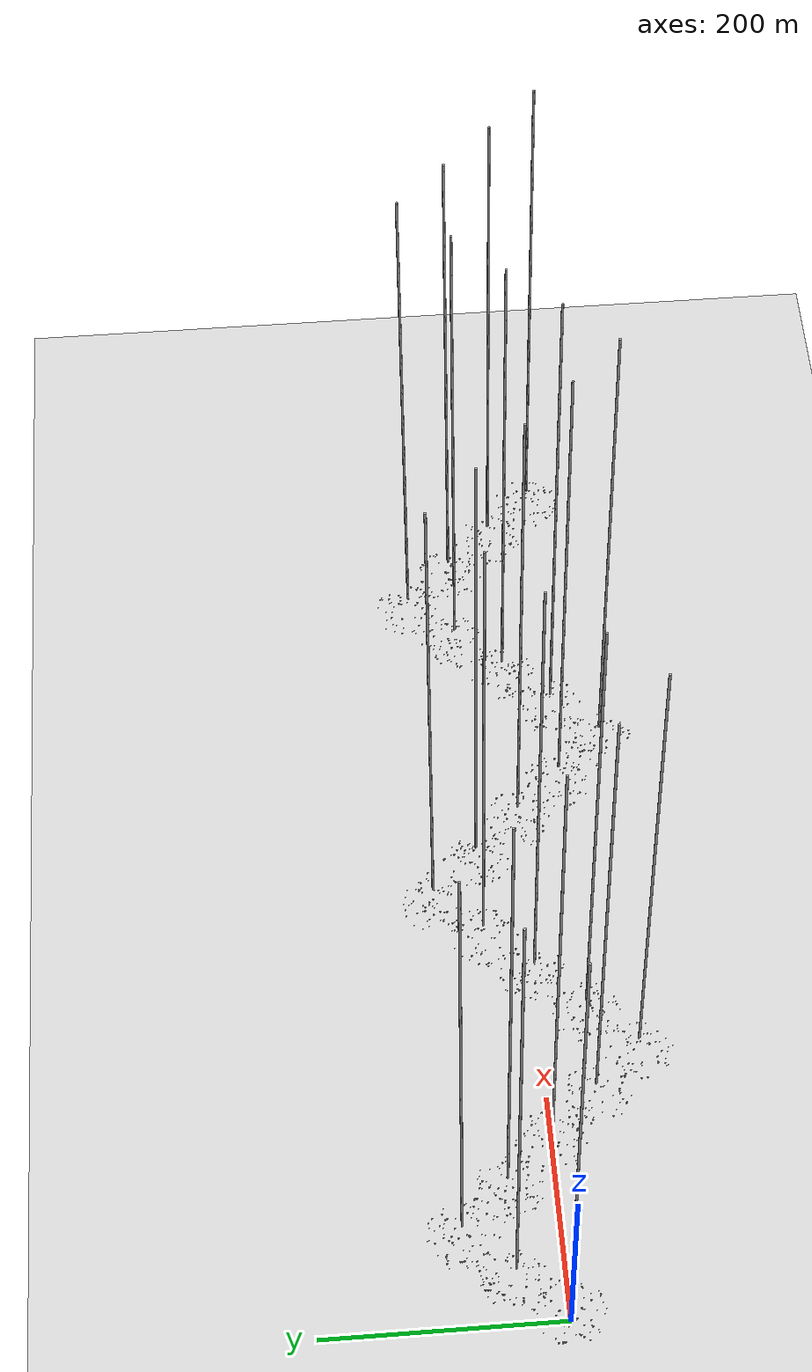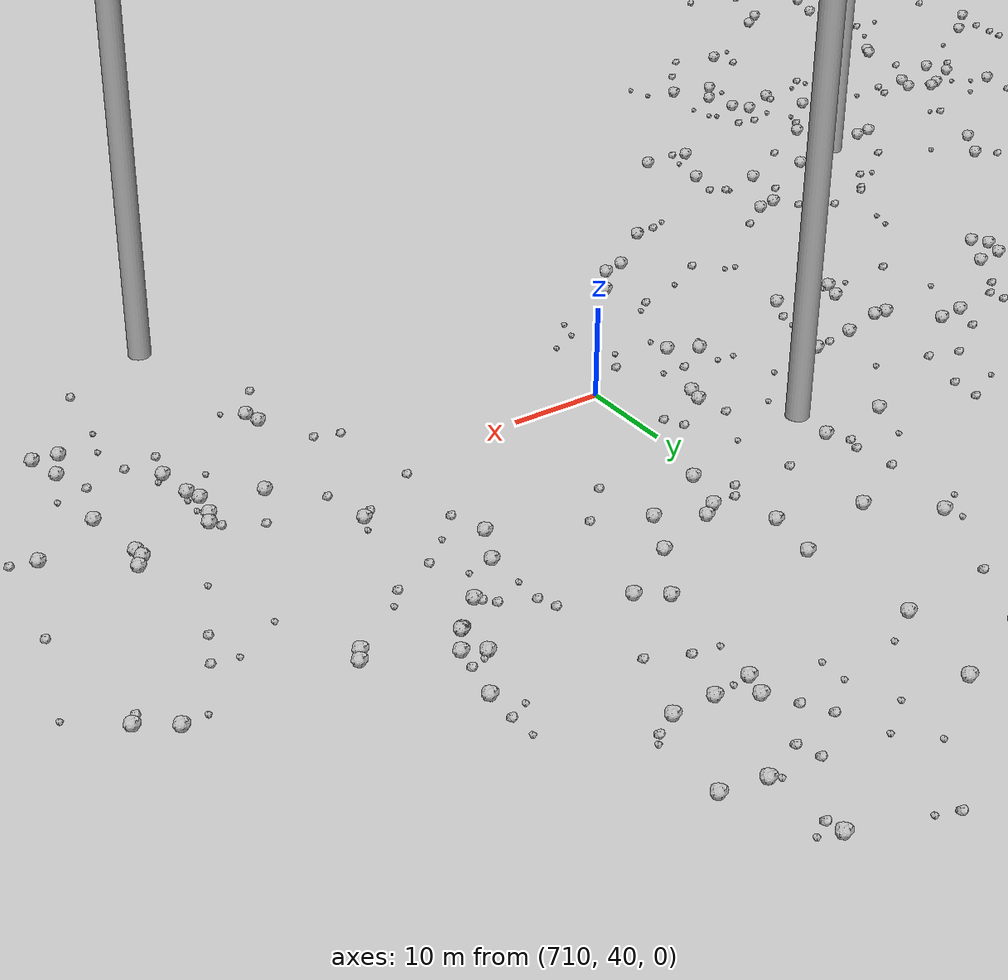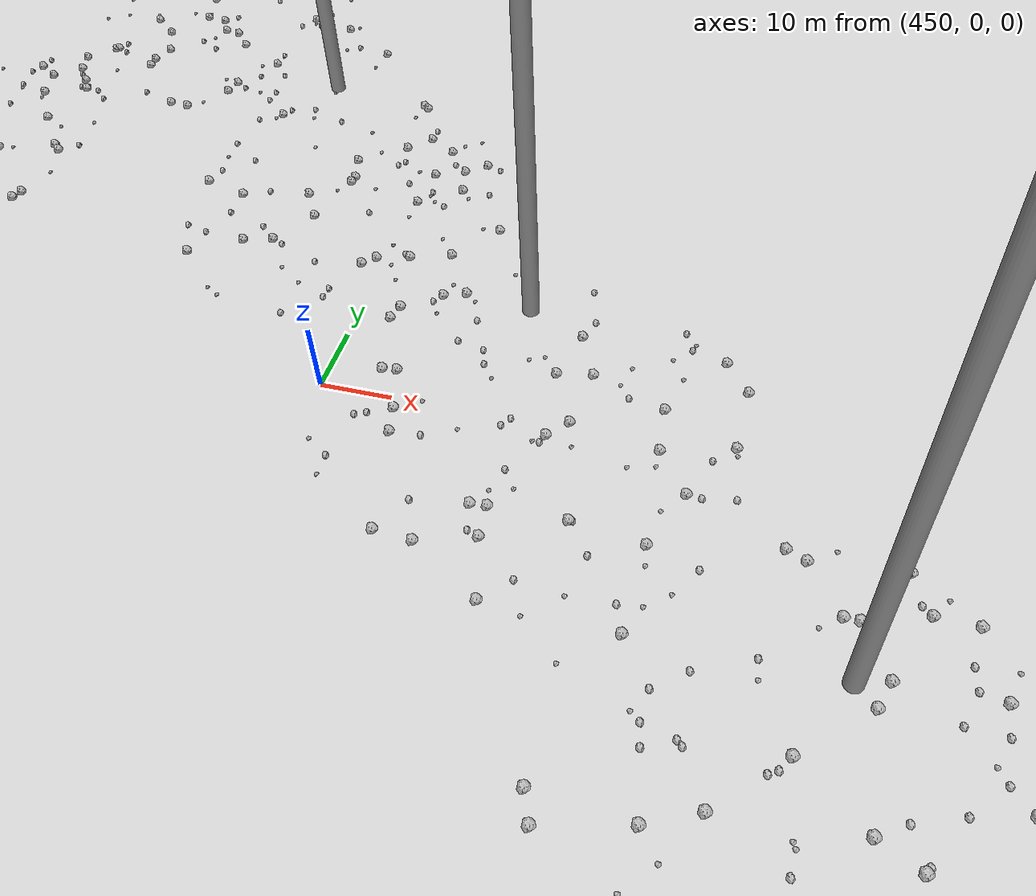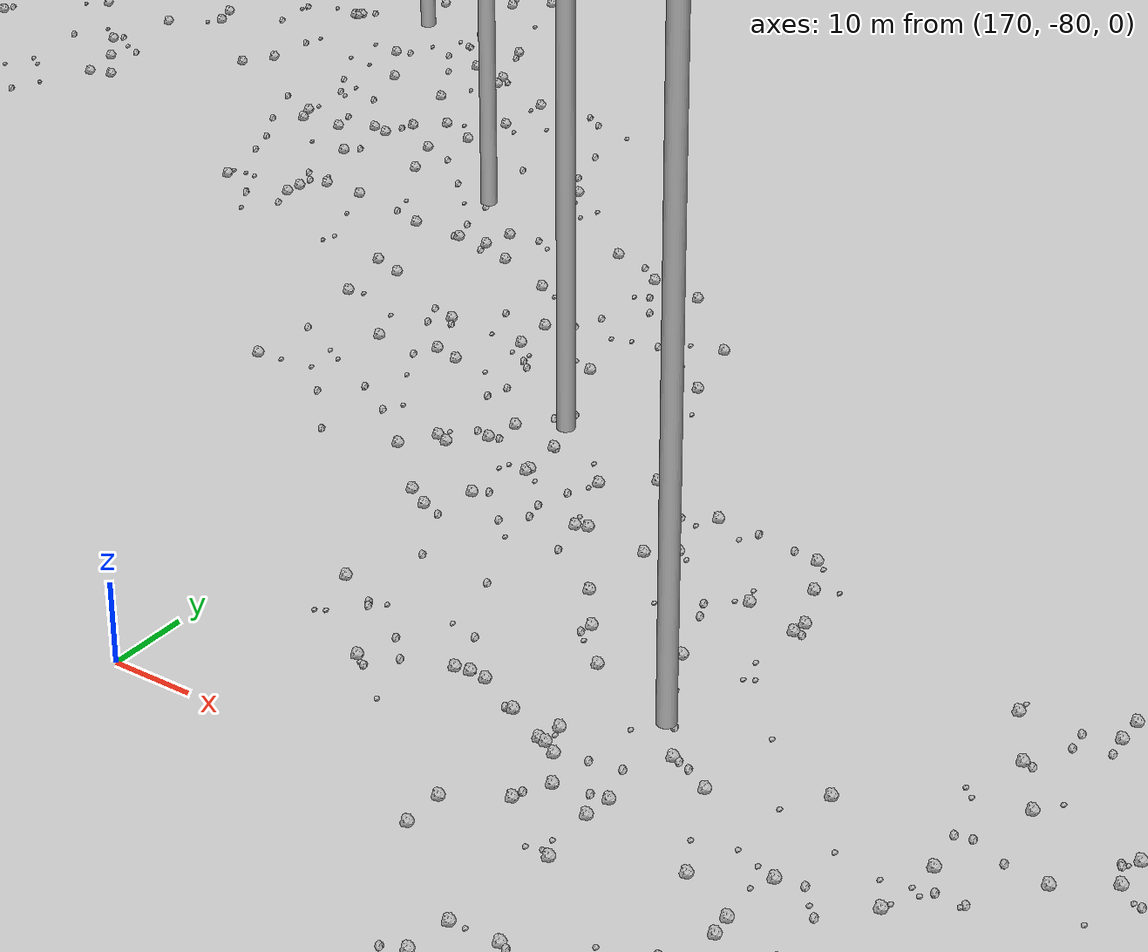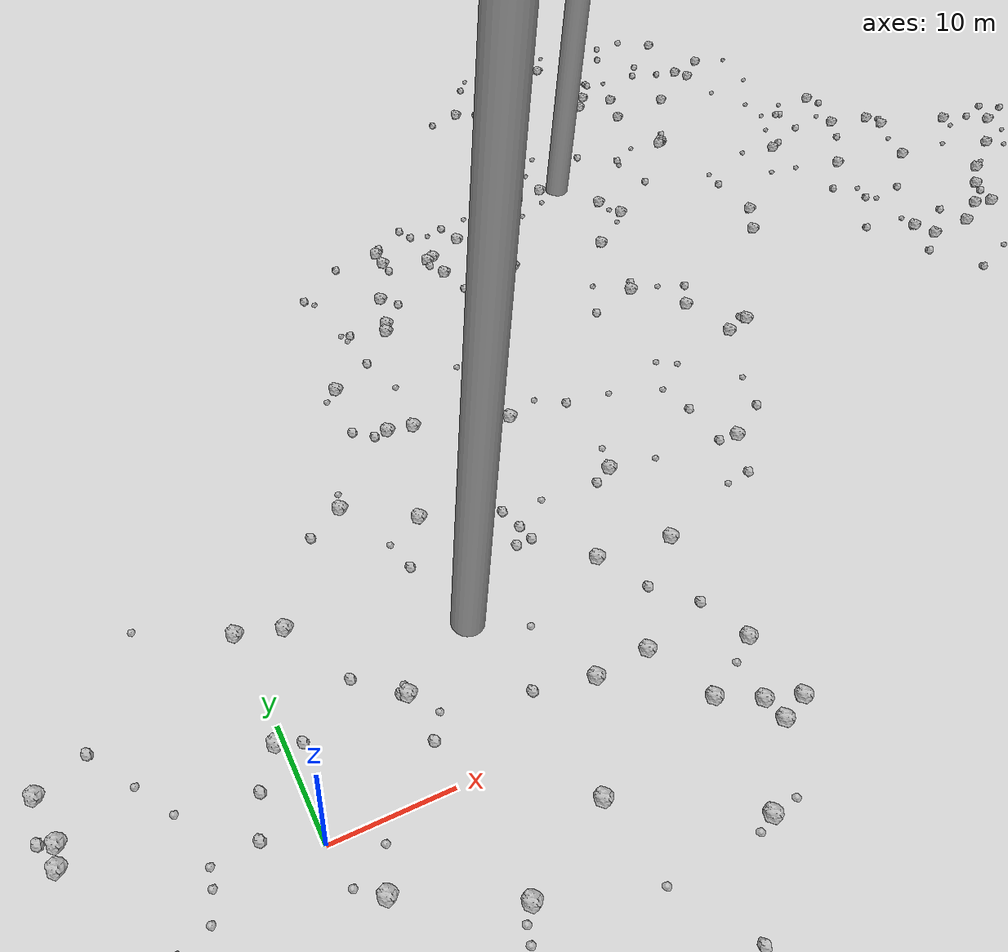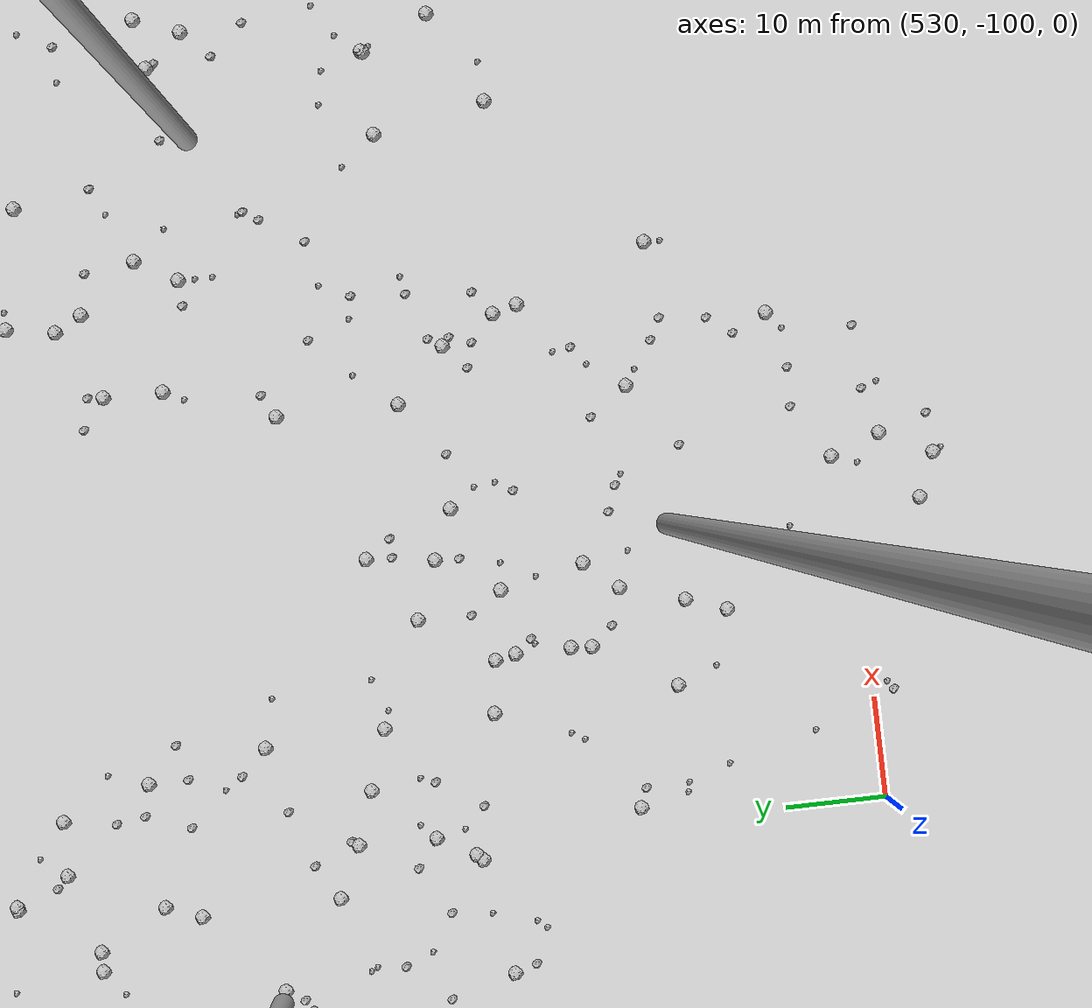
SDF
<sdf version="1.6">
 <world name="default">
  <include><uri>model://custom_ground</uri></include>
  <include><uri>model://sun</uri></include>
  <spherical_coordinates>
   <surface_model>EARTH_WGS84</surface_model>
   <latitude_deg>38.161479</latitude_deg>
   <longitude_deg>-122.454630</longitude_deg>
   <elevation>488.0</elevation>
   <heading_deg>90</heading_deg>
  </spherical_coordinates>
  <model name="rock1_0_0">
   <include><uri>model://rock1</uri><pose>10.02849448124853 8.230612105566998 0.5 0 0 0</pose></include>
  </model>
  <model name="rock1_0_1">
   <include><uri>model://rock1</uri><pose>29.072980740950804 3.853172992329739 0.5 0 0 0</pose></include>
  </model>
  <model name="rock1_0_2">
   <include><uri>model://rock1</uri><pose>37.18833192868596 1.4463406213011858 0.5 0 0 0</pose></include>
  </model>
  <model name="rock1_0_3">
   <include><uri>model://rock1</uri><pose>29.139050827073717 -11.189162614460031 0.5 0 0 0</pose></include>
  </model>
  <model name="rock1_0_4">
   <include><uri>model://rock1</uri><pose>10.877361282351853 -9.260265700012983 0.5 0 0 0</pose></include>
  </model>
  <model name="rock1_0_5">
   <include><uri>model://rock1</uri><pose>23.99170106523929 3.4412377452945577 0.5 0 0 0</pose></include>
  </model>
  <model name="rock1_0_6">
   <include><uri>model://rock1</uri><pose>-16.69601433414578 7.774357570519847 0.5 0 0 0</pose></include>
  </model>
  <model name="rock1_0_7">
   <include><uri>model://rock1</uri><pose>19.02783818439366 -5.210985564855072 0.5 0 0 0</pose></include>
  </model>
  <model name="rock1_0_8">
   <include><uri>model://rock1</uri><pose>-11.911545173617988 -6.575143413329606 0.5 0 0 0</pose></include>
  </model>
  <model name="rock1_0_9">
   <include><uri>model://rock1</uri><pose>3.442605049174638 17.95864992421498 0.5 0 0 0</pose></include>
  </model>
  <model name="rock1_0_10">
   <include><uri>model://rock1</uri><pose>34.9095106811757 -5.648890755054413 0.5 0 0 0</pose></include>
  </model>
  <model name="rock1_0_11">
   <include><uri>model://rock1</uri><pose>16.94240063646661 -17.660134640613805 0.5 0 0 0</pose></include>
  </model>
  <model name="rock1_0_12">
   <include><uri>model://rock1</uri><pose>2.4295444936437534 -4.927172542186604 0.5 0 0 0</pose></include>
  </model>
  <model name="rock1_0_13">
   <include><uri>model://rock1</uri><pose>18.853045679664795 14.532919669222217 0.5 0 0 0</pose></include>
  </model>
  <model name="rock1_0_14">
   <include><uri>model://rock1</uri><pose>30.555545489238597 13.542228266071163 0.5 0 0 0</pose></include>
  </model>
  <model name="rock1_0_15">
   <include><uri>model://rock1</uri><pose>0.03788783109249749 -15.543942105232759 0.5 0 0 0</pose></include>
  </model>
  <model name="rock1_0_16">
   <include><uri>model://rock1</uri><pose>31.228114719547733 -1.88221025846374 0.5 0 0 0</pose></include>
  </model>
  <model name="rock1_0_17">
   <include><uri>model://rock1</uri><pose>37.54663800356577 -4.662823276522694 0.5 0 0 0</pose></include>
  </model>
  <model name="rock1_0_18">
   <include><uri>model://rock1</uri><pose>-0.5862028521355569 8.540230338428941 0.5 0 0 0</pose></include>
  </model>
  <model name="rock1_0_19">
   <include><uri>model://rock1</uri><pose>-16.986201248152003 6.037516260184873 0.5 0 0 0</pose></include>
  </model>
  <model name="rock1_0_20">
   <include><uri>model://rock1</uri><pose>21.47227707232578 -25.43353209367471 0.5 0 0 0</pose></include>
  </model>
  <model name="rock1_0_21">
   <include><uri>model://rock1</uri><pose>12.429395298147845 28.227622201993952 0.5 0 0 0</pose></include>
  </model>
  <model name="rock1_0_22">
   <include><uri>model://rock1</uri><pose>-0.42065306089349264 19.082971695363298 0.5 0 0 0</pose></include>
  </model>
  <model name="rock1_0_23">
   <include><uri>model://rock1</uri><pose>34.58711269483153 -3.6417299478127667 0.5 0 0 0</pose></include>
  </model>
  <model name="rock1_0_24">
   <include><uri>model://rock1</uri><pose>-5.522741122187103 -16.36637412457866 0.5 0 0 0</pose></include>
  </model>
  <model name="rock1_0_25">
   <include><uri>model://rock1</uri><pose>-17.47697909781357 11.865102455572206 0.5 0 0 0</pose></include>
  </model>
  <model name="rock1_0_26">
   <include><uri>model://rock1</uri><pose>-13.799489983465884 -8.817173894947715 0.5 0 0 0</pose></include>
  </model>
  <model name="rock2_0_0">
   <include><uri>model://rock2</uri><pose>32.75345804217651 9.142630216231879 0.3 0 0 0</pose></include>
  </model>
  <model name="rock2_0_1">
   <include><uri>model://rock2</uri><pose>-8.6901231026007 -20.875930940380837 0.3 0 0 0</pose></include>
  </model>
  <model name="rock2_0_2">
   <include><uri>model://rock2</uri><pose>9.501455340577543 8.51916947199959 0.3 0 0 0</pose></include>
  </model>
  <model name="rock2_0_3">
   <include><uri>model://rock2</uri><pose>-16.725355553961688 -13.471528329047405 0.3 0 0 0</pose></include>
  </model>
  <model name="rock2_0_4">
   <include><uri>model://rock2</uri><pose>-17.942179385416647 8.33969438709245 0.3 0 0 0</pose></include>
  </model>
  <model name="rock2_0_5">
   <include><uri>model://rock2</uri><pose>6.472980094749673 11.408802322493706 0.3 0 0 0</pose></include>
  </model>
  <model name="rock2_0_6">
   <include><uri>model://rock2</uri><pose>26.20460106448713 19.5752815128941 0.3 0 0 0</pose></include>
  </model>
  <model name="rock2_0_7">
   <include><uri>model://rock2</uri><pose>-4.386717585284547 -15.780583853661891 0.3 0 0 0</pose></include>
  </model>
  <model name="rock2_0_8">
   <include><uri>model://rock2</uri><pose>14.62754889392641 -26.887484661231365 0.3 0 0 0</pose></include>
  </model>
  <model name="rock2_0_9">
   <include><uri>model://rock2</uri><pose>-10.774979831634345 -21.10434604974025 0.3 0 0 0</pose></include>
  </model>
  <model name="rock2_0_10">
   <include><uri>model://rock2</uri><pose>35.781661825509104 5.97039568708108 0.3 0 0 0</pose></include>
  </model>
  <model name="rock2_0_11">
   <include><uri>model://rock2</uri><pose>-4.046736252257512 2.1775038847010606 0.3 0 0 0</pose></include>
  </model>
  <model name="rock2_0_12">
   <include><uri>model://rock2</uri><pose>10.10468987957714 3.8906368446104835 0.3 0 0 0</pose></include>
  </model>
  <model name="rock2_0_13">
   <include><uri>model://rock2</uri><pose>20.30247014165498 -25.271762356185107 0.3 0 0 0</pose></include>
  </model>
  <model name="rock2_0_14">
   <include><uri>model://rock2</uri><pose>26.472690182559724 17.909671301731635 0.3 0 0 0</pose></include>
  </model>
  <model name="rock2_0_15">
   <include><uri>model://rock2</uri><pose>1.2463407762721381 7.884766289507766 0.3 0 0 0</pose></include>
  </model>
  <model name="rock2_0_16">
   <include><uri>model://rock2</uri><pose>22.93668898763847 -17.830239449443795 0.3 0 0 0</pose></include>
  </model>
  <model name="rock2_0_17">
   <include><uri>model://rock2</uri><pose>-13.46978765058756 13.66811421855656 0.3 0 0 0</pose></include>
  </model>
  <model name="rock2_0_18">
   <include><uri>model://rock2</uri><pose>-11.137351484062652 -5.312528715028346 0.3 0 0 0</pose></include>
  </model>
  <model name="rock2_0_19">
   <include><uri>model://rock2</uri><pose>8.767701904453123 26.178180712729855 0.3 0 0 0</pose></include>
  </model>
  <model name="rock2_0_20">
   <include><uri>model://rock2</uri><pose>18.825722416340184 4.489673039403904 0.3 0 0 0</pose></include>
  </model>
  <model name="rock2_0_21">
   <include><uri>model://rock2</uri><pose>8.754201747613358 -29.104795411066192 0.3 0 0 0</pose></include>
  </model>
  <model name="rock2_0_22">
   <include><uri>model://rock2</uri><pose>24.69523028487155 -24.45262175067485 0.3 0 0 0</pose></include>
  </model>
  <model name="rock2_0_23">
   <include><uri>model://rock2</uri><pose>15.402537630776465 19.51663461835126 0.3 0 0 0</pose></include>
  </model>
  <model name="rock2_0_24">
   <include><uri>model://rock2</uri><pose>-10.26478314683471 -13.644674524630528 0.3 0 0 0</pose></include>
  </model>
  <model name="rock2_0_25">
   <include><uri>model://rock2</uri><pose>-3.735256096366353 -9.773385662452615 0.3 0 0 0</pose></include>
  </model>
  <model name="rock2_0_26">
   <include><uri>model://rock2</uri><pose>-2.890756414065624 5.521671850487756 0.3 0 0 0</pose></include>
  </model>
  <model name="rock3_0_0">
   <include><uri>model://rock3</uri><pose>-10.910516607369598 9.66917152334149 0.2 0 0 0</pose></include>
  </model>
  <model name="rock3_0_1">
   <include><uri>model://rock3</uri><pose>19.50048530383718 -12.153488468413112 0.2 0 0 0</pose></include>
  </model>
  <model name="rock3_0_2">
   <include><uri>model://rock3</uri><pose>8.027077042627447 -21.147023526254006 0.2 0 0 0</pose></include>
  </model>
  <model name="rock3_0_3">
   <include><uri>model://rock3</uri><pose>-8.00442691393849 22.91551461922589 0.2 0 0 0</pose></include>
  </model>
  <model name="rock3_0_4">
   <include><uri>model://rock3</uri><pose>-7.661107541839501 1.8835954641529504 0.2 0 0 0</pose></include>
  </model>
  <model name="rock3_0_5">
   <include><uri>model://rock3</uri><pose>10.078123406508858 9.185884572666659 0.2 0 0 0</pose></include>
  </model>
  <model name="rock3_0_6">
   <include><uri>model://rock3</uri><pose>34.80303315938878 -0.07577926186385398 0.2 0 0 0</pose></include>
  </model>
  <model name="rock3_0_7">
   <include><uri>model://rock3</uri><pose>31.508142798898206 -10.919470580092458 0.2 0 0 0</pose></include>
  </model>
  <model name="rock3_0_8">
   <include><uri>model://rock3</uri><pose>3.72571749336241 -1.6660025100618086 0.2 0 0 0</pose></include>
  </model>
  <model name="rock3_0_9">
   <include><uri>model://rock3</uri><pose>-8.894872364115296 6.47839081857645 0.2 0 0 0</pose></include>
  </model>
  <model name="rock3_0_10">
   <include><uri>model://rock3</uri><pose>21.752884415708223 9.806362944358042 0.2 0 0 0</pose></include>
  </model>
  <model name="rock3_0_11">
   <include><uri>model://rock3</uri><pose>14.845268279565651 22.487427245171183 0.2 0 0 0</pose></include>
  </model>
  <model name="rock3_0_12">
   <include><uri>model://rock3</uri><pose>0.5287268606717355 -3.5095098184615416 0.2 0 0 0</pose></include>
  </model>
  <model name="rock3_0_13">
   <include><uri>model://rock3</uri><pose>-4.839949035072632 -11.754589294201242 0.2 0 0 0</pose></include>
  </model>
  <model name="rock3_0_14">
   <include><uri>model://rock3</uri><pose>3.001077661297483 -15.377709986400184 0.2 0 0 0</pose></include>
  </model>
  <model name="rock3_0_15">
   <include><uri>model://rock3</uri><pose>17.9446879507269 12.98902147300668 0.2 0 0 0</pose></include>
  </model>
  <model name="rock3_0_16">
   <include><uri>model://rock3</uri><pose>-14.57234553393834 -1.1888166450083872 0.2 0 0 0</pose></include>
  </model>
  <model name="rock3_0_17">
   <include><uri>model://rock3</uri><pose>27.559982608843193 -11.844237728209698 0.2 0 0 0</pose></include>
  </model>
  <model name="rock3_0_18">
   <include><uri>model://rock3</uri><pose>9.853362392538674 -10.348177156433142 0.2 0 0 0</pose></include>
  </model>
  <model name="rock3_0_19">
   <include><uri>model://rock3</uri><pose>4.706168446858257 -26.99921946760313 0.2 0 0 0</pose></include>
  </model>
  <model name="rock3_0_20">
   <include><uri>model://rock3</uri><pose>29.650395915083912 21.542705173512203 0.2 0 0 0</pose></include>
  </model>
  <model name="rock3_0_21">
   <include><uri>model://rock3</uri><pose>9.453801286791151 -11.565865016552092 0.2 0 0 0</pose></include>
  </model>
  <model name="rock3_0_22">
   <include><uri>model://rock3</uri><pose>-8.681567459747273 -1.79010456009809 0.2 0 0 0</pose></include>
  </model>
  <model name="rock3_0_23">
   <include><uri>model://rock3</uri><pose>11.561696053963136 5.88354960205082 0.2 0 0 0</pose></include>
  </model>
  <model name="rock3_0_24">
   <include><uri>model://rock3</uri><pose>-2.2843549206028086 -23.975394569408603 0.2 0 0 0</pose></include>
  </model>
  <model name="rock3_0_25">
   <include><uri>model://rock3</uri><pose>-11.274969794505763 -2.6387270600930393 0.2 0 0 0</pose></include>
  </model>
  <model name="rock3_0_26">
   <include><uri>model://rock3</uri><pose>-7.93114443242148 0.40289394856310423 0.2 0 0 0</pose></include>
  </model>
  <model name="rock1_1_0">
   <include><uri>model://rock1</uri><pose>20.575326178282765 35.836439635889754 0.5 0 0 0</pose></include>
  </model>
  <model name="rock1_1_1">
   <include><uri>model://rock1</uri><pose>22.008978174306037 19.184808132094798 0.5 0 0 0</pose></include>
  </model>
  <model name="rock1_1_2">
   <include><uri>model://rock1</uri><pose>32.48774831786669 32.55007132510256 0.5 0 0 0</pose></include>
  </model>
  <model name="rock1_1_3">
   <include><uri>model://rock1</uri><pose>59.91392809396931 40.671590810707976 0.5 0 0 0</pose></include>
  </model>
  <model name="rock1_1_4">
   <include><uri>model://rock1</uri><pose>37.02191463430636 61.03229830419561 0.5 0 0 0</pose></include>
  </model>
  <model name="rock1_1_5">
   <include><uri>model://rock1</uri><pose>34.57968665927635 44.58325882134719 0.5 0 0 0</pose></include>
  </model>
  <model name="rock1_1_6">
   <include><uri>model://rock1</uri><pose>42.339165782109205 63.69955080813546 0.5 0 0 0</pose></include>
  </model>
  <model name="rock1_1_7">
   <include><uri>model://rock1</uri><pose>61.286002043021874 34.6491531268572 0.5 0 0 0</pose></include>
  </model>
  <model name="rock1_1_8">
   <include><uri>model://rock1</uri><pose>31.947873488676542 64.86437850414552 0.5 0 0 0</pose></include>
  </model>
  <model name="rock1_1_9">
   <include><uri>model://rock1</uri><pose>18.515140969608648 24.263174834694702 0.5 0 0 0</pose></include>
  </model>
  <model name="rock1_1_10">
   <include><uri>model://rock1</uri><pose>37.52465001897028 22.286152343342742 0.5 0 0 0</pose></include>
  </model>
  <model name="rock1_1_11">
   <include><uri>model://rock1</uri><pose>23.152681244328345 35.39944326358801 0.5 0 0 0</pose></include>
  </model>
  <model name="rock1_1_12">
   <include><uri>model://rock1</uri><pose>26.891789605102293 50.443497948831556 0.5 0 0 0</pose></include>
  </model>
  <model name="rock1_1_13">
   <include><uri>model://rock1</uri><pose>28.725369551299078 56.16089606356583 0.5 0 0 0</pose></include>
  </model>
  <model name="rock1_1_14">
   <include><uri>model://rock1</uri><pose>37.733053660966355 12.801275831064434 0.5 0 0 0</pose></include>
  </model>
  <model name="rock1_1_15">
   <include><uri>model://rock1</uri><pose>55.83804439338006 45.73448011966511 0.5 0 0 0</pose></include>
  </model>
  <model name="rock1_1_16">
   <include><uri>model://rock1</uri><pose>37.75444192287616 57.92938305988096 0.5 0 0 0</pose></include>
  </model>
  <model name="rock1_1_17">
   <include><uri>model://rock1</uri><pose>27.490014304549877 51.67744760632227 0.5 0 0 0</pose></include>
  </model>
  <model name="rock1_1_18">
   <include><uri>model://rock1</uri><pose>49.284860680987194 68.31384677307747 0.5 0 0 0</pose></include>
  </model>
  <model name="rock1_1_19">
   <include><uri>model://rock1</uri><pose>18.210706732535755 43.63844076984863 0.5 0 0 0</pose></include>
  </model>
  <model name="rock1_1_20">
   <include><uri>model://rock1</uri><pose>58.1306286431718 55.53139484772332 0.5 0 0 0</pose></include>
  </model>
  <model name="rock1_1_21">
   <include><uri>model://rock1</uri><pose>45.84476302083491 55.69859320969994 0.5 0 0 0</pose></include>
  </model>
  <model name="rock1_1_22">
   <include><uri>model://rock1</uri><pose>22.855672775419805 19.896695368030073 0.5 0 0 0</pose></include>
  </model>
  <model name="rock1_1_23">
   <include><uri>model://rock1</uri><pose>64.42013639771639 35.667357889254205 0.5 0 0 0</pose></include>
  </model>
  <model name="rock1_1_24">
   <include><uri>model://rock1</uri><pose>31.876673478477244 62.68178073940616 0.5 0 0 0</pose></include>
  </model>
  <model name="rock1_1_25">
   <include><uri>model://rock1</uri><pose>37.93632018070042 61.4368879231776 0.5 0 0 0</pose></include>
  </model>
  <model name="rock1_1_26">
   <include><uri>model://rock1</uri><pose>51.46336304058265 20.87520542236526 0.5 0 0 0</pose></include>
  </model>
  <model name="rock2_1_0">
   <include><uri>model://rock2</uri><pose>19.058585265480534 35.694137724897416 0.3 0 0 0</pose></include>
  </model>
  <model name="rock2_1_1">
   <include><uri>model://rock2</uri><pose>41.65495923417302 66.88530013542274 0.3 0 0 0</pose></include>
  </model>
  <model name="rock2_1_2">
   <include><uri>model://rock2</uri><pose>36.825716877153255 60.1243059823028 0.3 0 0 0</pose></include>
  </model>
  <model name="rock2_1_3">
   <include><uri>model://rock2</uri><pose>26.24754387936855 63.933598863464724 0.3 0 0 0</pose></include>
  </model>
  <model name="rock2_1_4">
   <include><uri>model://rock2</uri><pose>22.9816434825663 51.537133750075085 0.3 0 0 0</pose></include>
  </model>
  <model name="rock2_1_5">
   <include><uri>model://rock2</uri><pose>34.90599964640819 46.2691808696637 0.3 0 0 0</pose></include>
  </model>
  <model name="rock2_1_6">
   <include><uri>model://rock2</uri><pose>22.803631583556218 46.35263460389424 0.3 0 0 0</pose></include>
  </model>
  <model name="rock2_1_7">
   <include><uri>model://rock2</uri><pose>38.451279257944826 54.21494360010048 0.3 0 0 0</pose></include>
  </model>
  <model name="rock2_1_8">
   <include><uri>model://rock2</uri><pose>64.05345529362948 36.35559082289707 0.3 0 0 0</pose></include>
  </model>
  <model name="rock2_1_9">
   <include><uri>model://rock2</uri><pose>37.300333561695794 66.66854032091351 0.3 0 0 0</pose></include>
  </model>
  <model name="rock2_1_10">
   <include><uri>model://rock2</uri><pose>31.93711659432751 61.156308235849515 0.3 0 0 0</pose></include>
  </model>
  <model name="rock2_1_11">
   <include><uri>model://rock2</uri><pose>32.70262925891073 66.00519166838347 0.3 0 0 0</pose></include>
  </model>
  <model name="rock2_1_12">
   <include><uri>model://rock2</uri><pose>56.04516130516425 23.6669188436096 0.3 0 0 0</pose></include>
  </model>
  <model name="rock2_1_13">
   <include><uri>model://rock2</uri><pose>24.896605114584773 17.789888631747203 0.3 0 0 0</pose></include>
  </model>
  <model name="rock2_1_14">
   <include><uri>model://rock2</uri><pose>49.40969296647728 21.119706530742853 0.3 0 0 0</pose></include>
  </model>
  <model name="rock2_1_15">
   <include><uri>model://rock2</uri><pose>35.445456044270784 21.271694634947245 0.3 0 0 0</pose></include>
  </model>
  <model name="rock2_1_16">
   <include><uri>model://rock2</uri><pose>20.631109411884953 59.61790488615615 0.3 0 0 0</pose></include>
  </model>
  <model name="rock2_1_17">
   <include><uri>model://rock2</uri><pose>38.72883636390381 32.08687424612008 0.3 0 0 0</pose></include>
  </model>
  <model name="rock2_1_18">
   <include><uri>model://rock2</uri><pose>25.661450963718135 21.789619908339382 0.3 0 0 0</pose></include>
  </model>
  <model name="rock2_1_19">
   <include><uri>model://rock2</uri><pose>49.19764400273631 16.45247743409596 0.3 0 0 0</pose></include>
  </model>
  <model name="rock2_1_20">
   <include><uri>model://rock2</uri><pose>56.63350601104948 47.10595593258555 0.3 0 0 0</pose></include>
  </model>
  <model name="rock2_1_21">
   <include><uri>model://rock2</uri><pose>30.166593839797407 54.612445398384615 0.3 0 0 0</pose></include>
  </model>
  <model name="rock2_1_22">
   <include><uri>model://rock2</uri><pose>61.99423198851988 43.91803889256397 0.3 0 0 0</pose></include>
  </model>
  <model name="rock2_1_23">
   <include><uri>model://rock2</uri><pose>49.79650813764876 43.72249444737813 0.3 0 0 0</pose></include>
  </model>
  <model name="rock2_1_24">
   <include><uri>model://rock2</uri><pose>17.303538092222396 37.15699665005125 0.3 0 0 0</pose></include>
  </model>
  <model name="rock2_1_25">
   <include><uri>model://rock2</uri><pose>49.49257568209757 26.076687855711004 0.3 0 0 0</pose></include>
  </model>
  <model name="rock2_1_26">
   <include><uri>model://rock2</uri><pose>36.61025743937894 68.51197095055966 0.3 0 0 0</pose></include>
  </model>
  <model name="rock3_1_0">
   <include><uri>model://rock3</uri><pose>20.68183122926719 17.901064795254243 0.2 0 0 0</pose></include>
  </model>
  <model name="rock3_1_1">
   <include><uri>model://rock3</uri><pose>23.984817232463833 41.594239313510045 0.2 0 0 0</pose></include>
  </model>
  <model name="rock3_1_2">
   <include><uri>model://rock3</uri><pose>39.40805388664539 66.16223944099289 0.2 0 0 0</pose></include>
  </model>
  <model name="rock3_1_3">
   <include><uri>model://rock3</uri><pose>48.90851099366552 29.699366682027417 0.2 0 0 0</pose></include>
  </model>
  <model name="rock3_1_4">
   <include><uri>model://rock3</uri><pose>38.42592672993969 24.962053474620618 0.2 0 0 0</pose></include>
  </model>
  <model name="rock3_1_5">
   <include><uri>model://rock3</uri><pose>21.522804311961735 58.57816278563244 0.2 0 0 0</pose></include>
  </model>
  <model name="rock3_1_6">
   <include><uri>model://rock3</uri><pose>45.2789807828702 67.76660572831008 0.2 0 0 0</pose></include>
  </model>
  <model name="rock3_1_7">
   <include><uri>model://rock3</uri><pose>43.46018026602582 31.502688559493453 0.2 0 0 0</pose></include>
  </model>
  <model name="rock3_1_8">
   <include><uri>model://rock3</uri><pose>59.14835999522538 45.15382506500744 0.2 0 0 0</pose></include>
  </model>
  <model name="rock3_1_9">
   <include><uri>model://rock3</uri><pose>62.750033240484186 59.04352944068275 0.2 0 0 0</pose></include>
  </model>
  <model name="rock3_1_10">
   <include><uri>model://rock3</uri><pose>42.3361524747249 21.667227787961775 0.2 0 0 0</pose></include>
  </model>
  <model name="rock3_1_11">
   <include><uri>model://rock3</uri><pose>49.96205595410872 62.93409602231211 0.2 0 0 0</pose></include>
  </model>
  <model name="rock3_1_12">
   <include><uri>model://rock3</uri><pose>52.279649211507184 48.34790936207901 0.2 0 0 0</pose></include>
  </model>
  <model name="rock3_1_13">
   <include><uri>model://rock3</uri><pose>24.738253428624034 23.257181109151436 0.2 0 0 0</pose></include>
  </model>
  <model name="rock3_1_14">
   <include><uri>model://rock3</uri><pose>35.985145388106986 33.831247916382495 0.2 0 0 0</pose></include>
  </model>
  <model name="rock3_1_15">
   <include><uri>model://rock3</uri><pose>46.55337492834213 16.042575195428874 0.2 0 0 0</pose></include>
  </model>
  <model name="rock3_1_16">
   <include><uri>model://rock3</uri><pose>42.90779509186838 53.78297568779757 0.2 0 0 0</pose></include>
  </model>
  <model name="rock3_1_17">
   <include><uri>model://rock3</uri><pose>52.46132846150695 65.29173875771781 0.2 0 0 0</pose></include>
  </model>
  <model name="rock3_1_18">
   <include><uri>model://rock3</uri><pose>22.415424250850123 50.836063657307726 0.2 0 0 0</pose></include>
  </model>
  <model name="rock3_1_19">
   <include><uri>model://rock3</uri><pose>31.236053465718005 41.90119902835397 0.2 0 0 0</pose></include>
  </model>
  <model name="rock3_1_20">
   <include><uri>model://rock3</uri><pose>57.60533236250139 27.798683118907338 0.2 0 0 0</pose></include>
  </model>
  <model name="rock3_1_21">
   <include><uri>model://rock3</uri><pose>42.23393489119207 58.836406618765935 0.2 0 0 0</pose></include>
  </model>
  <model name="rock3_1_22">
   <include><uri>model://rock3</uri><pose>50.85685079246087 33.69079600424701 0.2 0 0 0</pose></include>
  </model>
  <model name="rock3_1_23">
   <include><uri>model://rock3</uri><pose>52.742118881833456 32.49877555778112 0.2 0 0 0</pose></include>
  </model>
  <model name="rock3_1_24">
   <include><uri>model://rock3</uri><pose>12.956197503350108 30.059008388099862 0.2 0 0 0</pose></include>
  </model>
  <model name="rock3_1_25">
   <include><uri>model://rock3</uri><pose>22.09492161106268 51.95651363938173 0.2 0 0 0</pose></include>
  </model>
  <model name="rock3_1_26">
   <include><uri>model://rock3</uri><pose>16.69556619483258 42.432463683064654 0.2 0 0 0</pose></include>
  </model>
  <model name="rock1_2_0">
   <include><uri>model://rock1</uri><pose>88.03879299337764 85.24984581708662 0.5 0 0 0</pose></include>
  </model>
  <model name="rock1_2_1">
   <include><uri>model://rock1</uri><pose>63.60144653707559 93.91118274673872 0.5 0 0 0</pose></include>
  </model>
  <model name="rock1_2_2">
   <include><uri>model://rock1</uri><pose>79.86301175707372 54.25375490531595 0.5 0 0 0</pose></include>
  </model>
  <model name="rock1_2_3">
   <include><uri>model://rock1</uri><pose>57.614388741121935 69.61155164556 0.5 0 0 0</pose></include>
  </model>
  <model name="rock1_2_4">
   <include><uri>model://rock1</uri><pose>76.24586683164495 102.10786797869028 0.5 0 0 0</pose></include>
  </model>
  <model name="rock1_2_5">
   <include><uri>model://rock1</uri><pose>64.31271429857024 60.53342402605912 0.5 0 0 0</pose></include>
  </model>
  <model name="rock1_2_6">
   <include><uri>model://rock1</uri><pose>77.15284062325196 50.21914465256845 0.5 0 0 0</pose></include>
  </model>
  <model name="rock1_2_7">
   <include><uri>model://rock1</uri><pose>63.10454620328051 63.79861908972734 0.5 0 0 0</pose></include>
  </model>
  <model name="rock1_2_8">
   <include><uri>model://rock1</uri><pose>96.76016058263978 90.559960674606 0.5 0 0 0</pose></include>
  </model>
  <model name="rock1_2_9">
   <include><uri>model://rock1</uri><pose>80.34044774256462 74.45134109904676 0.5 0 0 0</pose></include>
  </model>
  <model name="rock1_2_10">
   <include><uri>model://rock1</uri><pose>75.4815691409397 88.35678430524021 0.5 0 0 0</pose></include>
  </model>
  <model name="rock1_2_11">
   <include><uri>model://rock1</uri><pose>101.27487388831834 94.54213492414496 0.5 0 0 0</pose></include>
  </model>
  <model name="rock1_2_12">
   <include><uri>model://rock1</uri><pose>77.61033217060758 90.80578540024862 0.5 0 0 0</pose></include>
  </model>
  <model name="rock1_2_13">
   <include><uri>model://rock1</uri><pose>58.085749748321064 81.33932563427192 0.5 0 0 0</pose></include>
  </model>
  <model name="rock1_2_14">
   <include><uri>model://rock1</uri><pose>95.80349067176508 92.45282991945712 0.5 0 0 0</pose></include>
  </model>
  <model name="rock1_2_15">
   <include><uri>model://rock1</uri><pose>65.33217586206011 93.41865170292385 0.5 0 0 0</pose></include>
  </model>
  <model name="rock1_2_16">
   <include><uri>model://rock1</uri><pose>57.43652133833465 93.82261939237975 0.5 0 0 0</pose></include>
  </model>
  <model name="rock1_2_17">
   <include><uri>model://rock1</uri><pose>58.45399019466463 79.771738624307 0.5 0 0 0</pose></include>
  </model>
  <model name="rock1_2_18">
   <include><uri>model://rock1</uri><pose>98.11836619603531 103.00865924259409 0.5 0 0 0</pose></include>
  </model>
  <model name="rock1_2_19">
   <include><uri>model://rock1</uri><pose>93.46017554921303 66.10263134594518 0.5 0 0 0</pose></include>
  </model>
  <model name="rock1_2_20">
   <include><uri>model://rock1</uri><pose>80.97066522444288 88.37292832163875 0.5 0 0 0</pose></include>
  </model>
  <model name="rock1_2_21">
   <include><uri>model://rock1</uri><pose>80.08646098579877 74.00196233931426 0.5 0 0 0</pose></include>
  </model>
  <model name="rock1_2_22">
   <include><uri>model://rock1</uri><pose>79.57062334203087 73.8357775611466 0.5 0 0 0</pose></include>
  </model>
  <model name="rock1_2_23">
   <include><uri>model://rock1</uri><pose>78.86181263318505 83.15423583583174 0.5 0 0 0</pose></include>
  </model>
  <model name="rock1_2_24">
   <include><uri>model://rock1</uri><pose>106.35357327854724 68.64500405166703 0.5 0 0 0</pose></include>
  </model>
  <model name="rock1_2_25">
   <include><uri>model://rock1</uri><pose>108.43997850255994 76.29950885331832 0.5 0 0 0</pose></include>
  </model>
  <model name="rock1_2_26">
   <include><uri>model://rock1</uri><pose>58.355355451247156 82.81822764987024 0.5 0 0 0</pose></include>
  </model>
  <model name="rock2_2_0">
   <include><uri>model://rock2</uri><pose>54.119450380335905 69.03943132815797 0.3 0 0 0</pose></include>
  </model>
  <model name="rock2_2_1">
   <include><uri>model://rock2</uri><pose>94.13873204128777 106.36794428721515 0.3 0 0 0</pose></include>
  </model>
  <model name="rock2_2_2">
   <include><uri>model://rock2</uri><pose>67.99262112787763 79.68285801802975 0.3 0 0 0</pose></include>
  </model>
  <model name="rock2_2_3">
   <include><uri>model://rock2</uri><pose>87.30029856534097 101.97386688280378 0.3 0 0 0</pose></include>
  </model>
  <model name="rock2_2_4">
   <include><uri>model://rock2</uri><pose>66.95915932684919 75.37563572629026 0.3 0 0 0</pose></include>
  </model>
  <model name="rock2_2_5">
   <include><uri>model://rock2</uri><pose>61.79987951631481 93.55274960727513 0.3 0 0 0</pose></include>
  </model>
  <model name="rock2_2_6">
   <include><uri>model://rock2</uri><pose>101.2785484618339 74.08836425727675 0.3 0 0 0</pose></include>
  </model>
  <model name="rock2_2_7">
   <include><uri>model://rock2</uri><pose>71.71190639760118 65.94964508414039 0.3 0 0 0</pose></include>
  </model>
  <model name="rock2_2_8">
   <include><uri>model://rock2</uri><pose>60.077467303481946 92.96523981988932 0.3 0 0 0</pose></include>
  </model>
  <model name="rock2_2_9">
   <include><uri>model://rock2</uri><pose>52.849933343168395 92.48495825721001 0.3 0 0 0</pose></include>
  </model>
  <model name="rock2_2_10">
   <include><uri>model://rock2</uri><pose>95.2562535013709 67.18392211782984 0.3 0 0 0</pose></include>
  </model>
  <model name="rock2_2_11">
   <include><uri>model://rock2</uri><pose>91.11017288582156 97.07877652248412 0.3 0 0 0</pose></include>
  </model>
  <model name="rock2_2_12">
   <include><uri>model://rock2</uri><pose>100.51267956792181 69.64675041954922 0.3 0 0 0</pose></include>
  </model>
  <model name="rock2_2_13">
   <include><uri>model://rock2</uri><pose>73.81716161261379 87.52138023127006 0.3 0 0 0</pose></include>
  </model>
  <model name="rock2_2_14">
   <include><uri>model://rock2</uri><pose>54.360857170999324 77.9952842662787 0.3 0 0 0</pose></include>
  </model>
  <model name="rock2_2_15">
   <include><uri>model://rock2</uri><pose>89.5398189053687 105.61550874113749 0.3 0 0 0</pose></include>
  </model>
  <model name="rock2_2_16">
   <include><uri>model://rock2</uri><pose>100.71490688432661 74.25569171668862 0.3 0 0 0</pose></include>
  </model>
  <model name="rock2_2_17">
   <include><uri>model://rock2</uri><pose>89.03280742040107 94.53040152996988 0.3 0 0 0</pose></include>
  </model>
  <model name="rock2_2_18">
   <include><uri>model://rock2</uri><pose>109.15976158904456 74.59529700953783 0.3 0 0 0</pose></include>
  </model>
  <model name="rock2_2_19">
   <include><uri>model://rock2</uri><pose>61.86646144337745 101.17819172779184 0.3 0 0 0</pose></include>
  </model>
  <model name="rock2_2_20">
   <include><uri>model://rock2</uri><pose>92.83419927948445 93.40124946809549 0.3 0 0 0</pose></include>
  </model>
  <model name="rock2_2_21">
   <include><uri>model://rock2</uri><pose>80.21035019032405 61.21201676537659 0.3 0 0 0</pose></include>
  </model>
  <model name="rock2_2_22">
   <include><uri>model://rock2</uri><pose>71.50748719099653 72.38538732542565 0.3 0 0 0</pose></include>
  </model>
  <model name="rock2_2_23">
   <include><uri>model://rock2</uri><pose>81.56233864298318 76.19996195229658 0.3 0 0 0</pose></include>
  </model>
  <model name="rock2_2_24">
   <include><uri>model://rock2</uri><pose>80.50831120195376 95.09564216408384 0.3 0 0 0</pose></include>
  </model>
  <model name="rock2_2_25">
   <include><uri>model://rock2</uri><pose>80.52368188447308 94.388819900519 0.3 0 0 0</pose></include>
  </model>
  <model name="rock2_2_26">
   <include><uri>model://rock2</uri><pose>93.32841890030068 53.89617230314544 0.3 0 0 0</pose></include>
  </model>
  <model name="rock3_2_0">
   <include><uri>model://rock3</uri><pose>92.76083536943537 60.46971065012448 0.2 0 0 0</pose></include>
  </model>
  <model name="rock3_2_1">
   <include><uri>model://rock3</uri><pose>83.43162446484959 94.21930977642808 0.2 0 0 0</pose></include>
  </model>
  <model name="rock3_2_2">
   <include><uri>model://rock3</uri><pose>65.51347277273368 100.58407748804689 0.2 0 0 0</pose></include>
  </model>
  <model name="rock3_2_3">
   <include><uri>model://rock3</uri><pose>96.74592439178164 84.36583420180003 0.2 0 0 0</pose></include>
  </model>
  <model name="rock3_2_4">
   <include><uri>model://rock3</uri><pose>61.064262770330956 77.65046360626384 0.2 0 0 0</pose></include>
  </model>
  <model name="rock3_2_5">
   <include><uri>model://rock3</uri><pose>88.96596314515587 60.884891083418815 0.2 0 0 0</pose></include>
  </model>
  <model name="rock3_2_6">
   <include><uri>model://rock3</uri><pose>53.93993175189219 70.38183108014135 0.2 0 0 0</pose></include>
  </model>
  <model name="rock3_2_7">
   <include><uri>model://rock3</uri><pose>106.04206813581993 93.57281205871934 0.2 0 0 0</pose></include>
  </model>
  <model name="rock3_2_8">
   <include><uri>model://rock3</uri><pose>87.67465542970301 102.76544994398269 0.2 0 0 0</pose></include>
  </model>
  <model name="rock3_2_9">
   <include><uri>model://rock3</uri><pose>57.87806228129728 73.9755269275288 0.2 0 0 0</pose></include>
  </model>
  <model name="rock3_2_10">
   <include><uri>model://rock3</uri><pose>104.22409988103206 86.0277611290847 0.2 0 0 0</pose></include>
  </model>
  <model name="rock3_2_11">
   <include><uri>model://rock3</uri><pose>63.44230783084046 61.95309781010099 0.2 0 0 0</pose></include>
  </model>
  <model name="rock3_2_12">
   <include><uri>model://rock3</uri><pose>52.704561000330344 77.58251642179724 0.2 0 0 0</pose></include>
  </model>
  <model name="rock3_2_13">
   <include><uri>model://rock3</uri><pose>105.96539780395008 71.36655107781966 0.2 0 0 0</pose></include>
  </model>
  <model name="rock3_2_14">
   <include><uri>model://rock3</uri><pose>56.430632275029154 67.15141792732499 0.2 0 0 0</pose></include>
  </model>
  <model name="rock3_2_15">
   <include><uri>model://rock3</uri><pose>88.80246352022886 66.93924326973466 0.2 0 0 0</pose></include>
  </model>
  <model name="rock3_2_16">
   <include><uri>model://rock3</uri><pose>96.30838397760166 71.07140244105929 0.2 0 0 0</pose></include>
  </model>
  <model name="rock3_2_17">
   <include><uri>model://rock3</uri><pose>103.38299612097256 76.70489175735166 0.2 0 0 0</pose></include>
  </model>
  <model name="rock3_2_18">
   <include><uri>model://rock3</uri><pose>80.76003511497137 63.91754053235147 0.2 0 0 0</pose></include>
  </model>
  <model name="rock3_2_19">
   <include><uri>model://rock3</uri><pose>58.38864397943267 84.64010899391403 0.2 0 0 0</pose></include>
  </model>
  <model name="rock3_2_20">
   <include><uri>model://rock3</uri><pose>78.22593085551615 108.34898444188322 0.2 0 0 0</pose></include>
  </model>
  <model name="rock3_2_21">
   <include><uri>model://rock3</uri><pose>71.13910953232465 71.2651641220051 0.2 0 0 0</pose></include>
  </model>
  <model name="rock3_2_22">
   <include><uri>model://rock3</uri><pose>98.61895909748367 74.91786109244262 0.2 0 0 0</pose></include>
  </model>
  <model name="rock3_2_23">
   <include><uri>model://rock3</uri><pose>98.94096972023699 78.96204430485187 0.2 0 0 0</pose></include>
  </model>
  <model name="rock3_2_24">
   <include><uri>model://rock3</uri><pose>75.33858860554419 74.58945008231049 0.2 0 0 0</pose></include>
  </model>
  <model name="rock3_2_25">
   <include><uri>model://rock3</uri><pose>63.98165736367215 103.8225652907544 0.2 0 0 0</pose></include>
  </model>
  <model name="rock3_2_26">
   <include><uri>model://rock3</uri><pose>79.28714425919098 106.46747039174025 0.2 0 0 0</pose></include>
  </model>
  <model name="rock1_3_0">
   <include><uri>model://rock1</uri><pose>110.93507026765501 19.750433268476243 0.5 0 0 0</pose></include>
  </model>
  <model name="rock1_3_1">
   <include><uri>model://rock1</uri><pose>120.61908588064325 47.55629858784484 0.5 0 0 0</pose></include>
  </model>
  <model name="rock1_3_2">
   <include><uri>model://rock1</uri><pose>119.36325959396602 24.827480482148 0.5 0 0 0</pose></include>
  </model>
  <model name="rock1_3_3">
   <include><uri>model://rock1</uri><pose>131.0733725392347 22.256639158747745 0.5 0 0 0</pose></include>
  </model>
  <model name="rock1_3_4">
   <include><uri>model://rock1</uri><pose>103.092406050942 40.507164185761866 0.5 0 0 0</pose></include>
  </model>
  <model name="rock1_3_5">
   <include><uri>model://rock1</uri><pose>143.39918500722624 42.25178911861236 0.5 0 0 0</pose></include>
  </model>
  <model name="rock1_3_6">
   <include><uri>model://rock1</uri><pose>112.65954237948706 65.29807731959896 0.5 0 0 0</pose></include>
  </model>
  <model name="rock1_3_7">
   <include><uri>model://rock1</uri><pose>96.1716343307531 42.34693472084238 0.5 0 0 0</pose></include>
  </model>
  <model name="rock1_3_8">
   <include><uri>model://rock1</uri><pose>138.35432568171095 22.092803840907393 0.5 0 0 0</pose></include>
  </model>
  <model name="rock1_3_9">
   <include><uri>model://rock1</uri><pose>111.95698662564311 67.54851894649897 0.5 0 0 0</pose></include>
  </model>
  <model name="rock1_3_10">
   <include><uri>model://rock1</uri><pose>111.12454395565067 22.128865140181624 0.5 0 0 0</pose></include>
  </model>
  <model name="rock1_3_11">
   <include><uri>model://rock1</uri><pose>143.4637459031846 26.39297367697622 0.5 0 0 0</pose></include>
  </model>
  <model name="rock1_3_12">
   <include><uri>model://rock1</uri><pose>122.02670594202807 54.58803753995655 0.5 0 0 0</pose></include>
  </model>
  <model name="rock1_3_13">
   <include><uri>model://rock1</uri><pose>109.80843929509378 42.67336484952863 0.5 0 0 0</pose></include>
  </model>
  <model name="rock1_3_14">
   <include><uri>model://rock1</uri><pose>97.15065356496794 39.93030770357659 0.5 0 0 0</pose></include>
  </model>
  <model name="rock1_3_15">
   <include><uri>model://rock1</uri><pose>117.81290248782007 42.07125344979356 0.5 0 0 0</pose></include>
  </model>
  <model name="rock1_3_16">
   <include><uri>model://rock1</uri><pose>115.11095918286898 49.99272421095411 0.5 0 0 0</pose></include>
  </model>
  <model name="rock1_3_17">
   <include><uri>model://rock1</uri><pose>122.24849587011346 62.727006454450624 0.5 0 0 0</pose></include>
  </model>
  <model name="rock1_3_18">
   <include><uri>model://rock1</uri><pose>128.05477863901328 59.79540327629994 0.5 0 0 0</pose></include>
  </model>
  <model name="rock1_3_19">
   <include><uri>model://rock1</uri><pose>108.78478572917999 34.64240215162379 0.5 0 0 0</pose></include>
  </model>
  <model name="rock1_3_20">
   <include><uri>model://rock1</uri><pose>113.64463922177691 24.943571013239897 0.5 0 0 0</pose></include>
  </model>
  <model name="rock1_3_21">
   <include><uri>model://rock1</uri><pose>120.47880098669388 35.71901494966857 0.5 0 0 0</pose></include>
  </model>
  <model name="rock1_3_22">
   <include><uri>model://rock1</uri><pose>111.53190858842649 46.776484044067054 0.5 0 0 0</pose></include>
  </model>
  <model name="rock1_3_23">
   <include><uri>model://rock1</uri><pose>107.46665587931757 43.177389833065604 0.5 0 0 0</pose></include>
  </model>
  <model name="rock1_3_24">
   <include><uri>model://rock1</uri><pose>108.66707996874564 57.04063052517492 0.5 0 0 0</pose></include>
  </model>
  <model name="rock1_3_25">
   <include><uri>model://rock1</uri><pose>100.66280792015834 19.353169363034006 0.5 0 0 0</pose></include>
  </model>
  <model name="rock1_3_26">
   <include><uri>model://rock1</uri><pose>98.75071004948798 58.89028340122506 0.5 0 0 0</pose></include>
  </model>
  <model name="rock2_3_0">
   <include><uri>model://rock2</uri><pose>110.71728897862907 45.31086526634812 0.3 0 0 0</pose></include>
  </model>
  <model name="rock2_3_1">
   <include><uri>model://rock2</uri><pose>138.58899329803359 53.0608442233326 0.3 0 0 0</pose></include>
  </model>
  <model name="rock2_3_2">
   <include><uri>model://rock2</uri><pose>126.72583761109203 23.756654271856323 0.3 0 0 0</pose></include>
  </model>
  <model name="rock2_3_3">
   <include><uri>model://rock2</uri><pose>110.27460340745591 36.425940425239716 0.3 0 0 0</pose></include>
  </model>
  <model name="rock2_3_4">
   <include><uri>model://rock2</uri><pose>112.00222178135887 16.559309025790373 0.3 0 0 0</pose></include>
  </model>
  <model name="rock2_3_5">
   <include><uri>model://rock2</uri><pose>132.93797406344655 43.7974889802546 0.3 0 0 0</pose></include>
  </model>
  <model name="rock2_3_6">
   <include><uri>model://rock2</uri><pose>102.11627412354513 43.986318813549396 0.3 0 0 0</pose></include>
  </model>
  <model name="rock2_3_7">
   <include><uri>model://rock2</uri><pose>113.45266400335576 66.68388326846683 0.3 0 0 0</pose></include>
  </model>
  <model name="rock2_3_8">
   <include><uri>model://rock2</uri><pose>110.98282095496894 24.509673031403807 0.3 0 0 0</pose></include>
  </model>
  <model name="rock2_3_9">
   <include><uri>model://rock2</uri><pose>93.62227726203037 37.442464746759114 0.3 0 0 0</pose></include>
  </model>
  <model name="rock2_3_10">
   <include><uri>model://rock2</uri><pose>106.40524864006217 16.46909220961533 0.3 0 0 0</pose></include>
  </model>
  <model name="rock2_3_11">
   <include><uri>model://rock2</uri><pose>128.2306104800374 35.23105195521993 0.3 0 0 0</pose></include>
  </model>
  <model name="rock2_3_12">
   <include><uri>model://rock2</uri><pose>132.84993828097066 61.99174422104803 0.3 0 0 0</pose></include>
  </model>
  <model name="rock2_3_13">
   <include><uri>model://rock2</uri><pose>126.0416763617258 61.90731085951093 0.3 0 0 0</pose></include>
  </model>
  <model name="rock2_3_14">
   <include><uri>model://rock2</uri><pose>136.88283021614328 25.848665974635733 0.3 0 0 0</pose></include>
  </model>
  <model name="rock2_3_15">
   <include><uri>model://rock2</uri><pose>90.42810764231065 44.668735629550554 0.3 0 0 0</pose></include>
  </model>
  <model name="rock2_3_16">
   <include><uri>model://rock2</uri><pose>130.3502120567967 63.54295894180144 0.3 0 0 0</pose></include>
  </model>
  <model name="rock2_3_17">
   <include><uri>model://rock2</uri><pose>137.5787739921929 22.03469520204871 0.3 0 0 0</pose></include>
  </model>
  <model name="rock2_3_18">
   <include><uri>model://rock2</uri><pose>109.3771705870119 26.25958829674183 0.3 0 0 0</pose></include>
  </model>
  <model name="rock2_3_19">
   <include><uri>model://rock2</uri><pose>95.61840478145248 50.34005177914846 0.3 0 0 0</pose></include>
  </model>
  <model name="rock2_3_20">
   <include><uri>model://rock2</uri><pose>101.40649109746349 50.67089031488489 0.3 0 0 0</pose></include>
  </model>
  <model name="rock2_3_21">
   <include><uri>model://rock2</uri><pose>104.0085528595196 64.9802399061976 0.3 0 0 0</pose></include>
  </model>
  <model name="rock2_3_22">
   <include><uri>model://rock2</uri><pose>98.48055887100631 27.91572703235711 0.3 0 0 0</pose></include>
  </model>
  <model name="rock2_3_23">
   <include><uri>model://rock2</uri><pose>135.71381867908656 31.54465699988489 0.3 0 0 0</pose></include>
  </model>
  <model name="rock2_3_24">
   <include><uri>model://rock2</uri><pose>122.43674562703202 40.50544834020256 0.3 0 0 0</pose></include>
  </model>
  <model name="rock2_3_25">
   <include><uri>model://rock2</uri><pose>96.88768617769497 32.178566547326376 0.3 0 0 0</pose></include>
  </model>
  <model name="rock2_3_26">
   <include><uri>model://rock2</uri><pose>140.56529541731163 46.23653536020413 0.3 0 0 0</pose></include>
  </model>
  <model name="rock3_3_0">
   <include><uri>model://rock3</uri><pose>117.23968558406118 51.1522708616205 0.2 0 0 0</pose></include>
  </model>
  <model name="rock3_3_1">
   <include><uri>model://rock3</uri><pose>108.75715459367726 12.544009522901707 0.2 0 0 0</pose></include>
  </model>
  <model name="rock3_3_2">
   <include><uri>model://rock3</uri><pose>96.46358124328599 52.64339487365857 0.2 0 0 0</pose></include>
  </model>
  <model name="rock3_3_3">
   <include><uri>model://rock3</uri><pose>110.52583172877544 61.58947747092297 0.2 0 0 0</pose></include>
  </model>
  <model name="rock3_3_4">
   <include><uri>model://rock3</uri><pose>138.4804934873318 60.78249710724851 0.2 0 0 0</pose></include>
  </model>
  <model name="rock3_3_5">
   <include><uri>model://rock3</uri><pose>96.87360339201255 49.61580458571412 0.2 0 0 0</pose></include>
  </model>
  <model name="rock3_3_6">
   <include><uri>model://rock3</uri><pose>100.29922020378929 21.016010718616286 0.2 0 0 0</pose></include>
  </model>
  <model name="rock3_3_7">
   <include><uri>model://rock3</uri><pose>112.18870699211507 26.929633845170944 0.2 0 0 0</pose></include>
  </model>
  <model name="rock3_3_8">
   <include><uri>model://rock3</uri><pose>125.60886599513043 27.038517565257955 0.2 0 0 0</pose></include>
  </model>
  <model name="rock3_3_9">
   <include><uri>model://rock3</uri><pose>124.23908196886694 53.404949920978375 0.2 0 0 0</pose></include>
  </model>
  <model name="rock3_3_10">
   <include><uri>model://rock3</uri><pose>139.9102092184861 45.262929163557146 0.2 0 0 0</pose></include>
  </model>
  <model name="rock3_3_11">
   <include><uri>model://rock3</uri><pose>103.74202172561847 21.291174050511046 0.2 0 0 0</pose></include>
  </model>
  <model name="rock3_3_12">
   <include><uri>model://rock3</uri><pose>132.4543424514776 30.932447143485312 0.2 0 0 0</pose></include>
  </model>
  <model name="rock3_3_13">
   <include><uri>model://rock3</uri><pose>124.44978137365845 13.064020964918337 0.2 0 0 0</pose></include>
  </model>
  <model name="rock3_3_14">
   <include><uri>model://rock3</uri><pose>96.17183717532879 44.500300258420644 0.2 0 0 0</pose></include>
  </model>
  <model name="rock3_3_15">
   <include><uri>model://rock3</uri><pose>147.79448066116987 36.37803607412141 0.2 0 0 0</pose></include>
  </model>
  <model name="rock3_3_16">
   <include><uri>model://rock3</uri><pose>123.92886212121459 11.266655771547525 0.2 0 0 0</pose></include>
  </model>
  <model name="rock3_3_17">
   <include><uri>model://rock3</uri><pose>144.57017760122545 39.64870076522058 0.2 0 0 0</pose></include>
  </model>
  <model name="rock3_3_18">
   <include><uri>model://rock3</uri><pose>138.47512733377218 44.82990628438812 0.2 0 0 0</pose></include>
  </model>
  <model name="rock3_3_19">
   <include><uri>model://rock3</uri><pose>127.51428562883675 56.72340709367104 0.2 0 0 0</pose></include>
  </model>
  <model name="rock3_3_20">
   <include><uri>model://rock3</uri><pose>102.21077739198151 21.29169710978575 0.2 0 0 0</pose></include>
  </model>
  <model name="rock3_3_21">
   <include><uri>model://rock3</uri><pose>121.79214383486973 60.861867861100585 0.2 0 0 0</pose></include>
  </model>
  <model name="rock3_3_22">
   <include><uri>model://rock3</uri><pose>105.67339405703153 17.22910097954996 0.2 0 0 0</pose></include>
  </model>
  <model name="rock3_3_23">
   <include><uri>model://rock3</uri><pose>103.05570505728733 34.57074040402183 0.2 0 0 0</pose></include>
  </model>
  <model name="rock3_3_24">
   <include><uri>model://rock3</uri><pose>148.67266825724167 39.05678809480973 0.2 0 0 0</pose></include>
  </model>
  <model name="rock3_3_25">
   <include><uri>model://rock3</uri><pose>121.53785176958785 19.299431744549985 0.2 0 0 0</pose></include>
  </model>
  <model name="rock3_3_26">
   <include><uri>model://rock3</uri><pose>116.42743704711022 57.15485188835463 0.2 0 0 0</pose></include>
  </model>
  <model name="rock1_4_0">
   <include><uri>model://rock1</uri><pose>136.2056604890189 1.428999006678822 0.5 0 0 0</pose></include>
  </model>
  <model name="rock1_4_1">
   <include><uri>model://rock1</uri><pose>133.83678406966595 10.610898023251963 0.5 0 0 0</pose></include>
  </model>
  <model name="rock1_4_2">
   <include><uri>model://rock1</uri><pose>155.80513023205214 16.647111355649336 0.5 0 0 0</pose></include>
  </model>
  <model name="rock1_4_3">
   <include><uri>model://rock1</uri><pose>162.4406335432416 8.089273124407164 0.5 0 0 0</pose></include>
  </model>
  <model name="rock1_4_4">
   <include><uri>model://rock1</uri><pose>137.7163084673608 -18.26942140692054 0.5 0 0 0</pose></include>
  </model>
  <model name="rock1_4_5">
   <include><uri>model://rock1</uri><pose>173.79870675753727 1.7854622497016592 0.5 0 0 0</pose></include>
  </model>
  <model name="rock1_4_6">
   <include><uri>model://rock1</uri><pose>170.09612387216745 -22.478406158955924 0.5 0 0 0</pose></include>
  </model>
  <model name="rock1_4_7">
   <include><uri>model://rock1</uri><pose>138.0167268244492 9.206718414810759 0.5 0 0 0</pose></include>
  </model>
  <model name="rock1_4_8">
   <include><uri>model://rock1</uri><pose>168.40883062817585 -21.813039505697077 0.5 0 0 0</pose></include>
  </model>
  <model name="rock1_4_9">
   <include><uri>model://rock1</uri><pose>142.52730306511089 22.422007019882777 0.5 0 0 0</pose></include>
  </model>
  <model name="rock1_4_10">
   <include><uri>model://rock1</uri><pose>152.64808059571683 25.911404432567473 0.5 0 0 0</pose></include>
  </model>
  <model name="rock1_4_11">
   <include><uri>model://rock1</uri><pose>187.2068313931638 5.454209926384124 0.5 0 0 0</pose></include>
  </model>
  <model name="rock1_4_12">
   <include><uri>model://rock1</uri><pose>176.49887527993042 15.314463947522071 0.5 0 0 0</pose></include>
  </model>
  <model name="rock1_4_13">
   <include><uri>model://rock1</uri><pose>155.04713995767636 -4.4692625819894936 0.5 0 0 0</pose></include>
  </model>
  <model name="rock1_4_14">
   <include><uri>model://rock1</uri><pose>173.5653699257182 -18.761016366781973 0.5 0 0 0</pose></include>
  </model>
  <model name="rock1_4_15">
   <include><uri>model://rock1</uri><pose>158.56719541044586 29.873778151640302 0.5 0 0 0</pose></include>
  </model>
  <model name="rock1_4_16">
   <include><uri>model://rock1</uri><pose>147.0219307251712 -5.9290318258993295 0.5 0 0 0</pose></include>
  </model>
  <model name="rock1_4_17">
   <include><uri>model://rock1</uri><pose>184.46003634546778 15.47033296819749 0.5 0 0 0</pose></include>
  </model>
  <model name="rock1_4_18">
   <include><uri>model://rock1</uri><pose>162.69215149126572 2.6422162249103422 0.5 0 0 0</pose></include>
  </model>
  <model name="rock1_4_19">
   <include><uri>model://rock1</uri><pose>158.5406775631311 -5.3649957540408835 0.5 0 0 0</pose></include>
  </model>
  <model name="rock1_4_20">
   <include><uri>model://rock1</uri><pose>174.45493927615647 -14.61777446605495 0.5 0 0 0</pose></include>
  </model>
  <model name="rock1_4_21">
   <include><uri>model://rock1</uri><pose>166.61688863838816 26.428014811204918 0.5 0 0 0</pose></include>
  </model>
  <model name="rock1_4_22">
   <include><uri>model://rock1</uri><pose>147.30208670353778 20.185227990350874 0.5 0 0 0</pose></include>
  </model>
  <model name="rock1_4_23">
   <include><uri>model://rock1</uri><pose>151.61728540669583 2.990991585587956 0.5 0 0 0</pose></include>
  </model>
  <model name="rock1_4_24">
   <include><uri>model://rock1</uri><pose>173.9733171484244 25.344778870726792 0.5 0 0 0</pose></include>
  </model>
  <model name="rock1_4_25">
   <include><uri>model://rock1</uri><pose>165.7296634636715 -26.093003839889764 0.5 0 0 0</pose></include>
  </model>
  <model name="rock1_4_26">
   <include><uri>model://rock1</uri><pose>181.3353532786274 -16.307011766307973 0.5 0 0 0</pose></include>
  </model>
  <model name="rock2_4_0">
   <include><uri>model://rock2</uri><pose>142.8661253187317 20.777913569556993 0.3 0 0 0</pose></include>
  </model>
  <model name="rock2_4_1">
   <include><uri>model://rock2</uri><pose>138.27135285896495 -9.222080316221223 0.3 0 0 0</pose></include>
  </model>
  <model name="rock2_4_2">
   <include><uri>model://rock2</uri><pose>165.6940236114835 -0.8717540288575485 0.3 0 0 0</pose></include>
  </model>
  <model name="rock2_4_3">
   <include><uri>model://rock2</uri><pose>156.34942314262582 8.143419673648232 0.3 0 0 0</pose></include>
  </model>
  <model name="rock2_4_4">
   <include><uri>model://rock2</uri><pose>165.56523320508083 10.259871967098292 0.3 0 0 0</pose></include>
  </model>
  <model name="rock2_4_5">
   <include><uri>model://rock2</uri><pose>159.08419901121792 -20.532417924956498 0.3 0 0 0</pose></include>
  </model>
  <model name="rock2_4_6">
   <include><uri>model://rock2</uri><pose>171.5190520289069 -18.093565316813834 0.3 0 0 0</pose></include>
  </model>
  <model name="rock2_4_7">
   <include><uri>model://rock2</uri><pose>149.63246496508515 0.6563351351588977 0.3 0 0 0</pose></include>
  </model>
  <model name="rock2_4_8">
   <include><uri>model://rock2</uri><pose>149.6993465378299 -21.40526149083402 0.3 0 0 0</pose></include>
  </model>
  <model name="rock2_4_9">
   <include><uri>model://rock2</uri><pose>177.2440956598921 -10.446515530642955 0.3 0 0 0</pose></include>
  </model>
  <model name="rock2_4_10">
   <include><uri>model://rock2</uri><pose>148.1834090203602 4.06761329423388 0.3 0 0 0</pose></include>
  </model>
  <model name="rock2_4_11">
   <include><uri>model://rock2</uri><pose>167.01714056220501 13.96335502049704 0.3 0 0 0</pose></include>
  </model>
  <model name="rock2_4_12">
   <include><uri>model://rock2</uri><pose>167.3042259140722 -10.486862099690146 0.3 0 0 0</pose></include>
  </model>
  <model name="rock2_4_13">
   <include><uri>model://rock2</uri><pose>168.74033944039363 22.239309936401384 0.3 0 0 0</pose></include>
  </model>
  <model name="rock2_4_14">
   <include><uri>model://rock2</uri><pose>168.13031860042113 -7.629790902154529 0.3 0 0 0</pose></include>
  </model>
  <model name="rock2_4_15">
   <include><uri>model://rock2</uri><pose>177.09815124416792 11.850377073207412 0.3 0 0 0</pose></include>
  </model>
  <model name="rock2_4_16">
   <include><uri>model://rock2</uri><pose>181.6525342861454 -16.29143781911928 0.3 0 0 0</pose></include>
  </model>
  <model name="rock2_4_17">
   <include><uri>model://rock2</uri><pose>163.48988158756094 28.83768394800827 0.3 0 0 0</pose></include>
  </model>
  <model name="rock2_4_18">
   <include><uri>model://rock2</uri><pose>156.01036663579671 -28.354322194828345 0.3 0 0 0</pose></include>
  </model>
  <model name="rock2_4_19">
   <include><uri>model://rock2</uri><pose>171.09917315378755 18.756801826075254 0.3 0 0 0</pose></include>
  </model>
  <model name="rock2_4_20">
   <include><uri>model://rock2</uri><pose>174.74046051663908 -18.145349861627555 0.3 0 0 0</pose></include>
  </model>
  <model name="rock2_4_21">
   <include><uri>model://rock2</uri><pose>152.4385108649237 1.8306484388823598 0.3 0 0 0</pose></include>
  </model>
  <model name="rock2_4_22">
   <include><uri>model://rock2</uri><pose>153.7488449048388 -17.231247661365934 0.3 0 0 0</pose></include>
  </model>
  <model name="rock2_4_23">
   <include><uri>model://rock2</uri><pose>166.97802383929127 -1.9865568384243169 0.3 0 0 0</pose></include>
  </model>
  <model name="rock2_4_24">
   <include><uri>model://rock2</uri><pose>153.40935424697696 -7.17557340118114 0.3 0 0 0</pose></include>
  </model>
  <model name="rock2_4_25">
   <include><uri>model://rock2</uri><pose>147.61651427136252 27.27428013888622 0.3 0 0 0</pose></include>
  </model>
  <model name="rock2_4_26">
   <include><uri>model://rock2</uri><pose>178.78931463880477 -8.271829372835505 0.3 0 0 0</pose></include>
  </model>
  <model name="rock3_4_0">
   <include><uri>model://rock3</uri><pose>158.49879864792567 15.532839234734325 0.2 0 0 0</pose></include>
  </model>
  <model name="rock3_4_1">
   <include><uri>model://rock3</uri><pose>189.9589361644769 -0.05160774811496793 0.2 0 0 0</pose></include>
  </model>
  <model name="rock3_4_2">
   <include><uri>model://rock3</uri><pose>144.5306964462368 -0.5279915690372547 0.2 0 0 0</pose></include>
  </model>
  <model name="rock3_4_3">
   <include><uri>model://rock3</uri><pose>162.91390752511637 0.42081281188491815 0.2 0 0 0</pose></include>
  </model>
  <model name="rock3_4_4">
   <include><uri>model://rock3</uri><pose>145.0530863506562 -16.96581327228548 0.2 0 0 0</pose></include>
  </model>
  <model name="rock3_4_5">
   <include><uri>model://rock3</uri><pose>180.02157899510283 14.56636760844475 0.2 0 0 0</pose></include>
  </model>
  <model name="rock3_4_6">
   <include><uri>model://rock3</uri><pose>168.8131816756473 -20.12251555831962 0.2 0 0 0</pose></include>
  </model>
  <model name="rock3_4_7">
   <include><uri>model://rock3</uri><pose>138.0256256908307 2.1765687392366857 0.2 0 0 0</pose></include>
  </model>
  <model name="rock3_4_8">
   <include><uri>model://rock3</uri><pose>165.22446422154854 0.8068745919815079 0.2 0 0 0</pose></include>
  </model>
  <model name="rock3_4_9">
   <include><uri>model://rock3</uri><pose>186.52380145886139 6.734850140590879 0.2 0 0 0</pose></include>
  </model>
  <model name="rock3_4_10">
   <include><uri>model://rock3</uri><pose>144.2112528895025 -12.253269426544545 0.2 0 0 0</pose></include>
  </model>
  <model name="rock3_4_11">
   <include><uri>model://rock3</uri><pose>169.58180916989153 -21.461010096275118 0.2 0 0 0</pose></include>
  </model>
  <model name="rock3_4_12">
   <include><uri>model://rock3</uri><pose>182.2223582615925 9.372731485283914 0.2 0 0 0</pose></include>
  </model>
  <model name="rock3_4_13">
   <include><uri>model://rock3</uri><pose>146.52096668457904 -13.600090623043112 0.2 0 0 0</pose></include>
  </model>
  <model name="rock3_4_14">
   <include><uri>model://rock3</uri><pose>170.7967492395959 3.026838909131861 0.2 0 0 0</pose></include>
  </model>
  <model name="rock3_4_15">
   <include><uri>model://rock3</uri><pose>158.04378200377204 2.7643576966414116 0.2 0 0 0</pose></include>
  </model>
  <model name="rock3_4_16">
   <include><uri>model://rock3</uri><pose>155.87429188076788 -11.804669022693396 0.2 0 0 0</pose></include>
  </model>
  <model name="rock3_4_17">
   <include><uri>model://rock3</uri><pose>163.291244963964 -5.696617266067172 0.2 0 0 0</pose></include>
  </model>
  <model name="rock3_4_18">
   <include><uri>model://rock3</uri><pose>174.89777139770027 18.124456267752926 0.2 0 0 0</pose></include>
  </model>
  <model name="rock3_4_19">
   <include><uri>model://rock3</uri><pose>160.23595976275115 -18.133847304825384 0.2 0 0 0</pose></include>
  </model>
  <model name="rock3_4_20">
   <include><uri>model://rock3</uri><pose>166.8482758641041 21.356617082401513 0.2 0 0 0</pose></include>
  </model>
  <model name="rock3_4_21">
   <include><uri>model://rock3</uri><pose>173.46891554441606 11.179144278953899 0.2 0 0 0</pose></include>
  </model>
  <model name="rock3_4_22">
   <include><uri>model://rock3</uri><pose>172.5432172804862 -3.03034375554261 0.2 0 0 0</pose></include>
  </model>
  <model name="rock3_4_23">
   <include><uri>model://rock3</uri><pose>170.96285476100158 10.331167763588262 0.2 0 0 0</pose></include>
  </model>
  <model name="rock3_4_24">
   <include><uri>model://rock3</uri><pose>140.77172244052667 -17.635301583195872 0.2 0 0 0</pose></include>
  </model>
  <model name="rock3_4_25">
   <include><uri>model://rock3</uri><pose>149.65191541163892 26.204388643974852 0.2 0 0 0</pose></include>
  </model>
  <model name="rock3_4_26">
   <include><uri>model://rock3</uri><pose>184.59071933538823 3.9223888566311444 0.2 0 0 0</pose></include>
  </model>
  <model name="rock1_5_0">
   <include><uri>model://rock1</uri><pose>190.2266349781749 -64.4976206080841 0.5 0 0 0</pose></include>
  </model>
  <model name="rock1_5_1">
   <include><uri>model://rock1</uri><pose>181.87134263466055 -22.645634983999166 0.5 0 0 0</pose></include>
  </model>
  <model name="rock1_5_2">
   <include><uri>model://rock1</uri><pose>179.28750903854842 -52.78170225978165 0.5 0 0 0</pose></include>
  </model>
  <model name="rock1_5_3">
   <include><uri>model://rock1</uri><pose>195.09287947460865 -28.814903543095333 0.5 0 0 0</pose></include>
  </model>
  <model name="rock1_5_4">
   <include><uri>model://rock1</uri><pose>203.3332833252593 -29.733929558672315 0.5 0 0 0</pose></include>
  </model>
  <model name="rock1_5_5">
   <include><uri>model://rock1</uri><pose>202.8832920241399 -39.65748082760006 0.5 0 0 0</pose></include>
  </model>
  <model name="rock1_5_6">
   <include><uri>model://rock1</uri><pose>206.3553305565769 -27.334974403577895 0.5 0 0 0</pose></include>
  </model>
  <model name="rock1_5_7">
   <include><uri>model://rock1</uri><pose>200.09440454676835 -60.3777467925755 0.5 0 0 0</pose></include>
  </model>
  <model name="rock1_5_8">
   <include><uri>model://rock1</uri><pose>218.39015559595964 -44.55220409328459 0.5 0 0 0</pose></include>
  </model>
  <model name="rock1_5_9">
   <include><uri>model://rock1</uri><pose>195.7378225446684 -15.736169960542554 0.5 0 0 0</pose></include>
  </model>
  <model name="rock1_5_10">
   <include><uri>model://rock1</uri><pose>225.63901207931792 -33.86155253204623 0.5 0 0 0</pose></include>
  </model>
  <model name="rock1_5_11">
   <include><uri>model://rock1</uri><pose>201.88251209202627 -60.07669853472238 0.5 0 0 0</pose></include>
  </model>
  <model name="rock1_5_12">
   <include><uri>model://rock1</uri><pose>225.82668459281285 -31.835127582843405 0.5 0 0 0</pose></include>
  </model>
  <model name="rock1_5_13">
   <include><uri>model://rock1</uri><pose>223.01986314980917 -25.494486668653828 0.5 0 0 0</pose></include>
  </model>
  <model name="rock1_5_14">
   <include><uri>model://rock1</uri><pose>193.65892564164415 -29.359598299924095 0.5 0 0 0</pose></include>
  </model>
  <model name="rock1_5_15">
   <include><uri>model://rock1</uri><pose>209.82756545395176 -63.205080602012075 0.5 0 0 0</pose></include>
  </model>
  <model name="rock1_5_16">
   <include><uri>model://rock1</uri><pose>179.7126283946067 -30.17944075084897 0.5 0 0 0</pose></include>
  </model>
  <model name="rock1_5_17">
   <include><uri>model://rock1</uri><pose>204.06854939555114 -60.31053232549823 0.5 0 0 0</pose></include>
  </model>
  <model name="rock1_5_18">
   <include><uri>model://rock1</uri><pose>220.11551150079396 -20.139239691615565 0.5 0 0 0</pose></include>
  </model>
  <model name="rock1_5_19">
   <include><uri>model://rock1</uri><pose>206.11825597716785 -18.784614118425445 0.5 0 0 0</pose></include>
  </model>
  <model name="rock1_5_20">
   <include><uri>model://rock1</uri><pose>207.24692309307505 -45.381380871836875 0.5 0 0 0</pose></include>
  </model>
  <model name="rock1_5_21">
   <include><uri>model://rock1</uri><pose>218.6057580000115 -31.64561753086909 0.5 0 0 0</pose></include>
  </model>
  <model name="rock1_5_22">
   <include><uri>model://rock1</uri><pose>190.41620655224156 -20.099874301219295 0.5 0 0 0</pose></include>
  </model>
  <model name="rock1_5_23">
   <include><uri>model://rock1</uri><pose>176.80544871412494 -35.48019314301728 0.5 0 0 0</pose></include>
  </model>
  <model name="rock1_5_24">
   <include><uri>model://rock1</uri><pose>182.0057620889892 -22.048817995570232 0.5 0 0 0</pose></include>
  </model>
  <model name="rock1_5_25">
   <include><uri>model://rock1</uri><pose>173.65644979547977 -33.57747691742229 0.5 0 0 0</pose></include>
  </model>
  <model name="rock1_5_26">
   <include><uri>model://rock1</uri><pose>212.1210738733506 -51.23875193626171 0.5 0 0 0</pose></include>
  </model>
  <model name="rock2_5_0">
   <include><uri>model://rock2</uri><pose>215.66024752185484 -36.927313820888116 0.3 0 0 0</pose></include>
  </model>
  <model name="rock2_5_1">
   <include><uri>model://rock2</uri><pose>214.56171007142615 -34.561519701039394 0.3 0 0 0</pose></include>
  </model>
  <model name="rock2_5_2">
   <include><uri>model://rock2</uri><pose>192.81594608409497 -44.84353526101838 0.3 0 0 0</pose></include>
  </model>
  <model name="rock2_5_3">
   <include><uri>model://rock2</uri><pose>211.5975294370068 -18.847858679981712 0.3 0 0 0</pose></include>
  </model>
  <model name="rock2_5_4">
   <include><uri>model://rock2</uri><pose>188.19807007019742 -30.600926154239964 0.3 0 0 0</pose></include>
  </model>
  <model name="rock2_5_5">
   <include><uri>model://rock2</uri><pose>181.23341193722285 -28.88475475365253 0.3 0 0 0</pose></include>
  </model>
  <model name="rock2_5_6">
   <include><uri>model://rock2</uri><pose>179.41395953628384 -36.24144692906292 0.3 0 0 0</pose></include>
  </model>
  <model name="rock2_5_7">
   <include><uri>model://rock2</uri><pose>198.2746393449492 -54.377583036130844 0.3 0 0 0</pose></include>
  </model>
  <model name="rock2_5_8">
   <include><uri>model://rock2</uri><pose>188.71866747040394 -23.854628136130287 0.3 0 0 0</pose></include>
  </model>
  <model name="rock2_5_9">
   <include><uri>model://rock2</uri><pose>221.50640738916456 -50.4834437991861 0.3 0 0 0</pose></include>
  </model>
  <model name="rock2_5_10">
   <include><uri>model://rock2</uri><pose>209.25907343946776 -62.849795835072165 0.3 0 0 0</pose></include>
  </model>
  <model name="rock2_5_11">
   <include><uri>model://rock2</uri><pose>191.9167909658434 -65.50756077969876 0.3 0 0 0</pose></include>
  </model>
  <model name="rock2_5_12">
   <include><uri>model://rock2</uri><pose>187.52831459447762 -27.98013152281684 0.3 0 0 0</pose></include>
  </model>
  <model name="rock2_5_13">
   <include><uri>model://rock2</uri><pose>202.4476723542077 -20.863032530494074 0.3 0 0 0</pose></include>
  </model>
  <model name="rock2_5_14">
   <include><uri>model://rock2</uri><pose>219.18125404239908 -48.833343579847764 0.3 0 0 0</pose></include>
  </model>
  <model name="rock2_5_15">
   <include><uri>model://rock2</uri><pose>185.79865187763664 -33.25731142410072 0.3 0 0 0</pose></include>
  </model>
  <model name="rock2_5_16">
   <include><uri>model://rock2</uri><pose>206.8920543245891 -46.85238384680797 0.3 0 0 0</pose></include>
  </model>
  <model name="rock2_5_17">
   <include><uri>model://rock2</uri><pose>195.07091273403043 -34.570254600141794 0.3 0 0 0</pose></include>
  </model>
  <model name="rock2_5_18">
   <include><uri>model://rock2</uri><pose>226.64986156196744 -33.75708219853162 0.3 0 0 0</pose></include>
  </model>
  <model name="rock2_5_19">
   <include><uri>model://rock2</uri><pose>194.3678622341659 -62.3794370653722 0.3 0 0 0</pose></include>
  </model>
  <model name="rock2_5_20">
   <include><uri>model://rock2</uri><pose>185.00290788675977 -55.98031679748857 0.3 0 0 0</pose></include>
  </model>
  <model name="rock2_5_21">
   <include><uri>model://rock2</uri><pose>225.18678756474932 -56.05785958019981 0.3 0 0 0</pose></include>
  </model>
  <model name="rock2_5_22">
   <include><uri>model://rock2</uri><pose>183.34566877876202 -44.18161113566789 0.3 0 0 0</pose></include>
  </model>
  <model name="rock2_5_23">
   <include><uri>model://rock2</uri><pose>216.80936929782004 -19.55508745756957 0.3 0 0 0</pose></include>
  </model>
  <model name="rock2_5_24">
   <include><uri>model://rock2</uri><pose>184.55643768532175 -55.348067630455326 0.3 0 0 0</pose></include>
  </model>
  <model name="rock2_5_25">
   <include><uri>model://rock2</uri><pose>191.43940873737273 -59.33727174531464 0.3 0 0 0</pose></include>
  </model>
  <model name="rock2_5_26">
   <include><uri>model://rock2</uri><pose>208.83570436977823 -63.174569649807836 0.3 0 0 0</pose></include>
  </model>
  <model name="rock3_5_0">
   <include><uri>model://rock3</uri><pose>226.0605121379392 -44.52358051873811 0.2 0 0 0</pose></include>
  </model>
  <model name="rock3_5_1">
   <include><uri>model://rock3</uri><pose>221.36328249642742 -20.92474938384546 0.2 0 0 0</pose></include>
  </model>
  <model name="rock3_5_2">
   <include><uri>model://rock3</uri><pose>204.61361187611288 -21.23981152346768 0.2 0 0 0</pose></include>
  </model>
  <model name="rock3_5_3">
   <include><uri>model://rock3</uri><pose>209.97419969496812 -37.50245064954634 0.2 0 0 0</pose></include>
  </model>
  <model name="rock3_5_4">
   <include><uri>model://rock3</uri><pose>211.36250752909348 -18.348162047905994 0.2 0 0 0</pose></include>
  </model>
  <model name="rock3_5_5">
   <include><uri>model://rock3</uri><pose>196.85081464966498 -69.60205210110931 0.2 0 0 0</pose></include>
  </model>
  <model name="rock3_5_6">
   <include><uri>model://rock3</uri><pose>192.78730133584003 -27.289881259478243 0.2 0 0 0</pose></include>
  </model>
  <model name="rock3_5_7">
   <include><uri>model://rock3</uri><pose>186.43207443252496 -54.59604209836126 0.2 0 0 0</pose></include>
  </model>
  <model name="rock3_5_8">
   <include><uri>model://rock3</uri><pose>207.84565988315427 -28.00664821388972 0.2 0 0 0</pose></include>
  </model>
  <model name="rock3_5_9">
   <include><uri>model://rock3</uri><pose>189.80555903279733 -21.307925565636786 0.2 0 0 0</pose></include>
  </model>
  <model name="rock3_5_10">
   <include><uri>model://rock3</uri><pose>208.04196967273217 -48.037520500191576 0.2 0 0 0</pose></include>
  </model>
  <model name="rock3_5_11">
   <include><uri>model://rock3</uri><pose>178.72290526655786 -23.665443660376027 0.2 0 0 0</pose></include>
  </model>
  <model name="rock3_5_12">
   <include><uri>model://rock3</uri><pose>183.89258993063987 -23.70776220009123 0.2 0 0 0</pose></include>
  </model>
  <model name="rock3_5_13">
   <include><uri>model://rock3</uri><pose>187.15646724023526 -16.46100485062226 0.2 0 0 0</pose></include>
  </model>
  <model name="rock3_5_14">
   <include><uri>model://rock3</uri><pose>216.918114902698 -32.09199566290985 0.2 0 0 0</pose></include>
  </model>
  <model name="rock3_5_15">
   <include><uri>model://rock3</uri><pose>191.04570284173496 -65.15324144794405 0.2 0 0 0</pose></include>
  </model>
  <model name="rock3_5_16">
   <include><uri>model://rock3</uri><pose>181.693023688912 -59.3353119910667 0.2 0 0 0</pose></include>
  </model>
  <model name="rock3_5_17">
   <include><uri>model://rock3</uri><pose>217.45969584676195 -29.134381010098217 0.2 0 0 0</pose></include>
  </model>
  <model name="rock3_5_18">
   <include><uri>model://rock3</uri><pose>179.1531877937304 -22.356390838053187 0.2 0 0 0</pose></include>
  </model>
  <model name="rock3_5_19">
   <include><uri>model://rock3</uri><pose>180.59410821669414 -59.95490415201624 0.2 0 0 0</pose></include>
  </model>
  <model name="rock3_5_20">
   <include><uri>model://rock3</uri><pose>194.53378360312433 -53.47239988813637 0.2 0 0 0</pose></include>
  </model>
  <model name="rock3_5_21">
   <include><uri>model://rock3</uri><pose>210.25625408367924 -20.96232438048765 0.2 0 0 0</pose></include>
  </model>
  <model name="rock3_5_22">
   <include><uri>model://rock3</uri><pose>227.14546937748057 -43.85992035096072 0.2 0 0 0</pose></include>
  </model>
  <model name="rock3_5_23">
   <include><uri>model://rock3</uri><pose>225.37914263393156 -41.03146255235898 0.2 0 0 0</pose></include>
  </model>
  <model name="rock3_5_24">
   <include><uri>model://rock3</uri><pose>215.89598630358643 -64.27864844361369 0.2 0 0 0</pose></include>
  </model>
  <model name="rock3_5_25">
   <include><uri>model://rock3</uri><pose>225.41870898259634 -24.132517690889124 0.2 0 0 0</pose></include>
  </model>
  <model name="rock3_5_26">
   <include><uri>model://rock3</uri><pose>188.421775608302 -35.66824719706271 0.2 0 0 0</pose></include>
  </model>
  <model name="rock1_6_0">
   <include><uri>model://rock1</uri><pose>212.83470795267823 -79.8940450666308 0.5 0 0 0</pose></include>
  </model>
  <model name="rock1_6_1">
   <include><uri>model://rock1</uri><pose>225.38991281741008 -101.03089638384147 0.5 0 0 0</pose></include>
  </model>
  <model name="rock1_6_2">
   <include><uri>model://rock1</uri><pose>215.65870776608355 -63.09632192513487 0.5 0 0 0</pose></include>
  </model>
  <model name="rock1_6_3">
   <include><uri>model://rock1</uri><pose>259.0939004172713 -61.5597875695833 0.5 0 0 0</pose></include>
  </model>
  <model name="rock1_6_4">
   <include><uri>model://rock1</uri><pose>233.8485466346964 -63.547185645116954 0.5 0 0 0</pose></include>
  </model>
  <model name="rock1_6_5">
   <include><uri>model://rock1</uri><pose>225.96762415785867 -95.45837959455798 0.5 0 0 0</pose></include>
  </model>
  <model name="rock1_6_6">
   <include><uri>model://rock1</uri><pose>216.03100325488558 -66.09368828082398 0.5 0 0 0</pose></include>
  </model>
  <model name="rock1_6_7">
   <include><uri>model://rock1</uri><pose>227.7285540083073 -81.75654138489435 0.5 0 0 0</pose></include>
  </model>
  <model name="rock1_6_8">
   <include><uri>model://rock1</uri><pose>240.117105575502 -76.20185789173297 0.5 0 0 0</pose></include>
  </model>
  <model name="rock1_6_9">
   <include><uri>model://rock1</uri><pose>231.81074981139437 -95.26104132753419 0.5 0 0 0</pose></include>
  </model>
  <model name="rock1_6_10">
   <include><uri>model://rock1</uri><pose>258.22491176995055 -70.11138886068991 0.5 0 0 0</pose></include>
  </model>
  <model name="rock1_6_11">
   <include><uri>model://rock1</uri><pose>220.91323014858293 -71.68058341604103 0.5 0 0 0</pose></include>
  </model>
  <model name="rock1_6_12">
   <include><uri>model://rock1</uri><pose>228.15384020997206 -60.79950276743924 0.5 0 0 0</pose></include>
  </model>
  <model name="rock1_6_13">
   <include><uri>model://rock1</uri><pose>244.12024964653517 -90.17472465982695 0.5 0 0 0</pose></include>
  </model>
  <model name="rock1_6_14">
   <include><uri>model://rock1</uri><pose>245.95583685549067 -95.26974033684021 0.5 0 0 0</pose></include>
  </model>
  <model name="rock1_6_15">
   <include><uri>model://rock1</uri><pose>254.78291666103945 -89.28187931050638 0.5 0 0 0</pose></include>
  </model>
  <model name="rock1_6_16">
   <include><uri>model://rock1</uri><pose>227.05682334723832 -70.56604387429485 0.5 0 0 0</pose></include>
  </model>
  <model name="rock1_6_17">
   <include><uri>model://rock1</uri><pose>217.9117339023067 -67.27545185800693 0.5 0 0 0</pose></include>
  </model>
  <model name="rock1_6_18">
   <include><uri>model://rock1</uri><pose>247.08680612618755 -79.744507157925 0.5 0 0 0</pose></include>
  </model>
  <model name="rock1_6_19">
   <include><uri>model://rock1</uri><pose>244.81347059125142 -57.2717101959217 0.5 0 0 0</pose></include>
  </model>
  <model name="rock1_6_20">
   <include><uri>model://rock1</uri><pose>226.74414699486894 -73.99963536563908 0.5 0 0 0</pose></include>
  </model>
  <model name="rock1_6_21">
   <include><uri>model://rock1</uri><pose>213.0231962536056 -85.18256229680009 0.5 0 0 0</pose></include>
  </model>
  <model name="rock1_6_22">
   <include><uri>model://rock1</uri><pose>215.0445164934373 -65.90052324153348 0.5 0 0 0</pose></include>
  </model>
  <model name="rock1_6_23">
   <include><uri>model://rock1</uri><pose>247.4572374456198 -71.99404183796783 0.5 0 0 0</pose></include>
  </model>
  <model name="rock1_6_24">
   <include><uri>model://rock1</uri><pose>247.5362406442022 -82.5211056477761 0.5 0 0 0</pose></include>
  </model>
  <model name="rock1_6_25">
   <include><uri>model://rock1</uri><pose>237.06640371509604 -99.23491012772011 0.5 0 0 0</pose></include>
  </model>
  <model name="rock1_6_26">
   <include><uri>model://rock1</uri><pose>219.0039036527191 -75.88093835118505 0.5 0 0 0</pose></include>
  </model>
  <model name="rock2_6_0">
   <include><uri>model://rock2</uri><pose>225.49939308136447 -105.47579942339573 0.3 0 0 0</pose></include>
  </model>
  <model name="rock2_6_1">
   <include><uri>model://rock2</uri><pose>219.18886223978043 -74.29687967230342 0.3 0 0 0</pose></include>
  </model>
  <model name="rock2_6_2">
   <include><uri>model://rock2</uri><pose>261.1416638655859 -64.8958625810983 0.3 0 0 0</pose></include>
  </model>
  <model name="rock2_6_3">
   <include><uri>model://rock2</uri><pose>254.1541238404053 -86.4465424425165 0.3 0 0 0</pose></include>
  </model>
  <model name="rock2_6_4">
   <include><uri>model://rock2</uri><pose>251.60897796654223 -105.58637991160897 0.3 0 0 0</pose></include>
  </model>
  <model name="rock2_6_5">
   <include><uri>model://rock2</uri><pose>243.1659458732547 -104.64791897399476 0.3 0 0 0</pose></include>
  </model>
  <model name="rock2_6_6">
   <include><uri>model://rock2</uri><pose>245.77946303931716 -98.68979603881701 0.3 0 0 0</pose></include>
  </model>
  <model name="rock2_6_7">
   <include><uri>model://rock2</uri><pose>264.484617384026 -89.14185514605859 0.3 0 0 0</pose></include>
  </model>
  <model name="rock2_6_8">
   <include><uri>model://rock2</uri><pose>230.57377716417244 -61.4927847741579 0.3 0 0 0</pose></include>
  </model>
  <model name="rock2_6_9">
   <include><uri>model://rock2</uri><pose>229.82867257761401 -102.23457737204998 0.3 0 0 0</pose></include>
  </model>
  <model name="rock2_6_10">
   <include><uri>model://rock2</uri><pose>236.47244000066132 -104.44462633666221 0.3 0 0 0</pose></include>
  </model>
  <model name="rock2_6_11">
   <include><uri>model://rock2</uri><pose>266.3089266748938 -81.55185133818429 0.3 0 0 0</pose></include>
  </model>
  <model name="rock2_6_12">
   <include><uri>model://rock2</uri><pose>244.88031338827915 -88.07608635019571 0.3 0 0 0</pose></include>
  </model>
  <model name="rock2_6_13">
   <include><uri>model://rock2</uri><pose>222.8297910778428 -102.03242259396417 0.3 0 0 0</pose></include>
  </model>
  <model name="rock2_6_14">
   <include><uri>model://rock2</uri><pose>246.01729322646588 -89.96703270893957 0.3 0 0 0</pose></include>
  </model>
  <model name="rock2_6_15">
   <include><uri>model://rock2</uri><pose>239.8497956758952 -105.5130687486862 0.3 0 0 0</pose></include>
  </model>
  <model name="rock2_6_16">
   <include><uri>model://rock2</uri><pose>221.50600448797843 -66.15317684838526 0.3 0 0 0</pose></include>
  </model>
  <model name="rock2_6_17">
   <include><uri>model://rock2</uri><pose>250.47751033831187 -71.18652518497507 0.3 0 0 0</pose></include>
  </model>
  <model name="rock2_6_18">
   <include><uri>model://rock2</uri><pose>264.7937793576057 -81.52517950805824 0.3 0 0 0</pose></include>
  </model>
  <model name="rock2_6_19">
   <include><uri>model://rock2</uri><pose>256.26095174729596 -97.98873701837454 0.3 0 0 0</pose></include>
  </model>
  <model name="rock2_6_20">
   <include><uri>model://rock2</uri><pose>225.206868716457 -65.42537332109293 0.3 0 0 0</pose></include>
  </model>
  <model name="rock2_6_21">
   <include><uri>model://rock2</uri><pose>232.7827241235023 -95.58765183123592 0.3 0 0 0</pose></include>
  </model>
  <model name="rock2_6_22">
   <include><uri>model://rock2</uri><pose>249.06673276139668 -104.27124166414566 0.3 0 0 0</pose></include>
  </model>
  <model name="rock2_6_23">
   <include><uri>model://rock2</uri><pose>224.92721519444362 -70.73951083340064 0.3 0 0 0</pose></include>
  </model>
  <model name="rock2_6_24">
   <include><uri>model://rock2</uri><pose>229.02737493955706 -60.93837675754424 0.3 0 0 0</pose></include>
  </model>
  <model name="rock2_6_25">
   <include><uri>model://rock2</uri><pose>253.77048779136902 -74.87677374215193 0.3 0 0 0</pose></include>
  </model>
  <model name="rock2_6_26">
   <include><uri>model://rock2</uri><pose>254.07662420005818 -81.90089896993577 0.3 0 0 0</pose></include>
  </model>
  <model name="rock3_6_0">
   <include><uri>model://rock3</uri><pose>226.24936366871947 -79.11895372574655 0.2 0 0 0</pose></include>
  </model>
  <model name="rock3_6_1">
   <include><uri>model://rock3</uri><pose>264.8150146595483 -75.72561592535341 0.2 0 0 0</pose></include>
  </model>
  <model name="rock3_6_2">
   <include><uri>model://rock3</uri><pose>223.28011479294995 -103.52200392911617 0.2 0 0 0</pose></include>
  </model>
  <model name="rock3_6_3">
   <include><uri>model://rock3</uri><pose>249.80837679716495 -64.82843359526169 0.2 0 0 0</pose></include>
  </model>
  <model name="rock3_6_4">
   <include><uri>model://rock3</uri><pose>258.8121641522997 -65.32971224631883 0.2 0 0 0</pose></include>
  </model>
  <model name="rock3_6_5">
   <include><uri>model://rock3</uri><pose>265.12705298057887 -85.44758126214039 0.2 0 0 0</pose></include>
  </model>
  <model name="rock3_6_6">
   <include><uri>model://rock3</uri><pose>239.36341233214281 -90.41321999835294 0.2 0 0 0</pose></include>
  </model>
  <model name="rock3_6_7">
   <include><uri>model://rock3</uri><pose>244.91830979063658 -71.01558434449947 0.2 0 0 0</pose></include>
  </model>
  <model name="rock3_6_8">
   <include><uri>model://rock3</uri><pose>241.91183629560788 -69.90569037544876 0.2 0 0 0</pose></include>
  </model>
  <model name="rock3_6_9">
   <include><uri>model://rock3</uri><pose>234.4298016691421 -52.02434263184689 0.2 0 0 0</pose></include>
  </model>
  <model name="rock3_6_10">
   <include><uri>model://rock3</uri><pose>267.2728178109002 -83.65610625048474 0.2 0 0 0</pose></include>
  </model>
  <model name="rock3_6_11">
   <include><uri>model://rock3</uri><pose>241.96260714169316 -109.39141607166361 0.2 0 0 0</pose></include>
  </model>
  <model name="rock3_6_12">
   <include><uri>model://rock3</uri><pose>241.61299661924144 -61.906914841027195 0.2 0 0 0</pose></include>
  </model>
  <model name="rock3_6_13">
   <include><uri>model://rock3</uri><pose>252.27947247245078 -73.45744458660226 0.2 0 0 0</pose></include>
  </model>
  <model name="rock3_6_14">
   <include><uri>model://rock3</uri><pose>237.26839382458382 -71.28773563529235 0.2 0 0 0</pose></include>
  </model>
  <model name="rock3_6_15">
   <include><uri>model://rock3</uri><pose>255.66314881471467 -66.06614626669636 0.2 0 0 0</pose></include>
  </model>
  <model name="rock3_6_16">
   <include><uri>model://rock3</uri><pose>266.4246430520494 -79.07947605461513 0.2 0 0 0</pose></include>
  </model>
  <model name="rock3_6_17">
   <include><uri>model://rock3</uri><pose>254.3349426214932 -92.3364583419442 0.2 0 0 0</pose></include>
  </model>
  <model name="rock3_6_18">
   <include><uri>model://rock3</uri><pose>224.6804012198011 -81.45979926261735 0.2 0 0 0</pose></include>
  </model>
  <model name="rock3_6_19">
   <include><uri>model://rock3</uri><pose>221.65438478618083 -58.98620189895869 0.2 0 0 0</pose></include>
  </model>
  <model name="rock3_6_20">
   <include><uri>model://rock3</uri><pose>246.19816062946842 -74.41625616392095 0.2 0 0 0</pose></include>
  </model>
  <model name="rock3_6_21">
   <include><uri>model://rock3</uri><pose>227.65082972380446 -95.1891431523689 0.2 0 0 0</pose></include>
  </model>
  <model name="rock3_6_22">
   <include><uri>model://rock3</uri><pose>264.1196117090082 -65.35212083295434 0.2 0 0 0</pose></include>
  </model>
  <model name="rock3_6_23">
   <include><uri>model://rock3</uri><pose>258.46555842510895 -68.79306791475408 0.2 0 0 0</pose></include>
  </model>
  <model name="rock3_6_24">
   <include><uri>model://rock3</uri><pose>260.0839402557868 -66.08572890621774 0.2 0 0 0</pose></include>
  </model>
  <model name="rock3_6_25">
   <include><uri>model://rock3</uri><pose>226.3554259574185 -80.93225364348051 0.2 0 0 0</pose></include>
  </model>
  <model name="rock3_6_26">
   <include><uri>model://rock3</uri><pose>252.5269244589646 -105.47317418171241 0.2 0 0 0</pose></include>
  </model>
  <model name="rock1_7_0">
   <include><uri>model://rock1</uri><pose>286.8462645889211 -15.543451640189033 0.5 0 0 0</pose></include>
  </model>
  <model name="rock1_7_1">
   <include><uri>model://rock1</uri><pose>297.63545404463275 -48.89556248967089 0.5 0 0 0</pose></include>
  </model>
  <model name="rock1_7_2">
   <include><uri>model://rock1</uri><pose>262.36508951136085 -47.84051828015583 0.5 0 0 0</pose></include>
  </model>
  <model name="rock1_7_3">
   <include><uri>model://rock1</uri><pose>292.7488322729786 -28.281713734514263 0.5 0 0 0</pose></include>
  </model>
  <model name="rock1_7_4">
   <include><uri>model://rock1</uri><pose>279.37395034805786 -54.42304905906866 0.5 0 0 0</pose></include>
  </model>
  <model name="rock1_7_5">
   <include><uri>model://rock1</uri><pose>293.72570526946697 -43.659872430826084 0.5 0 0 0</pose></include>
  </model>
  <model name="rock1_7_6">
   <include><uri>model://rock1</uri><pose>299.45444289571947 -23.44965320307481 0.5 0 0 0</pose></include>
  </model>
  <model name="rock1_7_7">
   <include><uri>model://rock1</uri><pose>263.6831905352095 -27.923753641033315 0.5 0 0 0</pose></include>
  </model>
  <model name="rock1_7_8">
   <include><uri>model://rock1</uri><pose>285.31619303496433 -35.80300004769549 0.5 0 0 0</pose></include>
  </model>
  <model name="rock1_7_9">
   <include><uri>model://rock1</uri><pose>252.77018957943548 -33.26537357532648 0.5 0 0 0</pose></include>
  </model>
  <model name="rock1_7_10">
   <include><uri>model://rock1</uri><pose>284.8878566232394 -66.79452897622919 0.5 0 0 0</pose></include>
  </model>
  <model name="rock1_7_11">
   <include><uri>model://rock1</uri><pose>269.4843000252763 -57.66110297680512 0.5 0 0 0</pose></include>
  </model>
  <model name="rock1_7_12">
   <include><uri>model://rock1</uri><pose>289.8201310580614 -14.536842127046867 0.5 0 0 0</pose></include>
  </model>
  <model name="rock1_7_13">
   <include><uri>model://rock1</uri><pose>283.0296536210078 -45.888214517333076 0.5 0 0 0</pose></include>
  </model>
  <model name="rock1_7_14">
   <include><uri>model://rock1</uri><pose>274.7592444764586 -29.5215177352283 0.5 0 0 0</pose></include>
  </model>
  <model name="rock1_7_15">
   <include><uri>model://rock1</uri><pose>289.9006258023484 -45.05785717339827 0.5 0 0 0</pose></include>
  </model>
  <model name="rock1_7_16">
   <include><uri>model://rock1</uri><pose>275.157497785594 -53.61192597840086 0.5 0 0 0</pose></include>
  </model>
  <model name="rock1_7_17">
   <include><uri>model://rock1</uri><pose>257.495243517685 -40.971782611159696 0.5 0 0 0</pose></include>
  </model>
  <model name="rock1_7_18">
   <include><uri>model://rock1</uri><pose>285.4166847457249 -44.409822679827826 0.5 0 0 0</pose></include>
  </model>
  <model name="rock1_7_19">
   <include><uri>model://rock1</uri><pose>272.74852321146136 -27.74276718567321 0.5 0 0 0</pose></include>
  </model>
  <model name="rock1_7_20">
   <include><uri>model://rock1</uri><pose>284.4383986595614 -53.99408420701535 0.5 0 0 0</pose></include>
  </model>
  <model name="rock1_7_21">
   <include><uri>model://rock1</uri><pose>263.84367033703603 -31.58859919798242 0.5 0 0 0</pose></include>
  </model>
  <model name="rock1_7_22">
   <include><uri>model://rock1</uri><pose>286.88978584453616 -43.76394260751593 0.5 0 0 0</pose></include>
  </model>
  <model name="rock1_7_23">
   <include><uri>model://rock1</uri><pose>304.6994768387499 -38.31503844246798 0.5 0 0 0</pose></include>
  </model>
  <model name="rock1_7_24">
   <include><uri>model://rock1</uri><pose>272.0602338797265 -36.66135738238993 0.5 0 0 0</pose></include>
  </model>
  <model name="rock1_7_25">
   <include><uri>model://rock1</uri><pose>296.4421311168274 -52.20209285815895 0.5 0 0 0</pose></include>
  </model>
  <model name="rock1_7_26">
   <include><uri>model://rock1</uri><pose>274.9716508680673 -49.12101325618963 0.5 0 0 0</pose></include>
  </model>
  <model name="rock2_7_0">
   <include><uri>model://rock2</uri><pose>270.52703357225545 -34.57817075893477 0.3 0 0 0</pose></include>
  </model>
  <model name="rock2_7_1">
   <include><uri>model://rock2</uri><pose>298.4442293738293 -30.250536099946615 0.3 0 0 0</pose></include>
  </model>
  <model name="rock2_7_2">
   <include><uri>model://rock2</uri><pose>257.9834859855755 -55.69118158544522 0.3 0 0 0</pose></include>
  </model>
  <model name="rock2_7_3">
   <include><uri>model://rock2</uri><pose>264.3208756692164 -19.779811444155413 0.3 0 0 0</pose></include>
  </model>
  <model name="rock2_7_4">
   <include><uri>model://rock2</uri><pose>287.14597727491355 -63.78940714153329 0.3 0 0 0</pose></include>
  </model>
  <model name="rock2_7_5">
   <include><uri>model://rock2</uri><pose>278.3501746783005 -55.49278635152463 0.3 0 0 0</pose></include>
  </model>
  <model name="rock2_7_6">
   <include><uri>model://rock2</uri><pose>283.33605834695015 -17.16473632200816 0.3 0 0 0</pose></include>
  </model>
  <model name="rock2_7_7">
   <include><uri>model://rock2</uri><pose>307.9066997104455 -39.214744426808004 0.3 0 0 0</pose></include>
  </model>
  <model name="rock2_7_8">
   <include><uri>model://rock2</uri><pose>264.2491558827964 -34.355608099747116 0.3 0 0 0</pose></include>
  </model>
  <model name="rock2_7_9">
   <include><uri>model://rock2</uri><pose>264.4935566875467 -64.87352218803998 0.3 0 0 0</pose></include>
  </model>
  <model name="rock2_7_10">
   <include><uri>model://rock2</uri><pose>307.3298983157356 -46.35331239793386 0.3 0 0 0</pose></include>
  </model>
  <model name="rock2_7_11">
   <include><uri>model://rock2</uri><pose>273.73277551139944 -50.6414526678074 0.3 0 0 0</pose></include>
  </model>
  <model name="rock2_7_12">
   <include><uri>model://rock2</uri><pose>263.6914547903497 -15.76324308901728 0.3 0 0 0</pose></include>
  </model>
  <model name="rock2_7_13">
   <include><uri>model://rock2</uri><pose>273.5292895126586 -50.410061295338636 0.3 0 0 0</pose></include>
  </model>
  <model name="rock2_7_14">
   <include><uri>model://rock2</uri><pose>299.84835673669625 -31.685721787686653 0.3 0 0 0</pose></include>
  </model>
  <model name="rock2_7_15">
   <include><uri>model://rock2</uri><pose>299.69624950952345 -51.82979244899523 0.3 0 0 0</pose></include>
  </model>
  <model name="rock2_7_16">
   <include><uri>model://rock2</uri><pose>264.2821312818285 -56.998535166206 0.3 0 0 0</pose></include>
  </model>
  <model name="rock2_7_17">
   <include><uri>model://rock2</uri><pose>287.6822785907412 -65.87901600068062 0.3 0 0 0</pose></include>
  </model>
  <model name="rock2_7_18">
   <include><uri>model://rock2</uri><pose>292.74875531635615 -65.18677623017591 0.3 0 0 0</pose></include>
  </model>
  <model name="rock2_7_19">
   <include><uri>model://rock2</uri><pose>306.7051639922334 -52.07720509656038 0.3 0 0 0</pose></include>
  </model>
  <model name="rock2_7_20">
   <include><uri>model://rock2</uri><pose>259.98808110395703 -32.94445362027492 0.3 0 0 0</pose></include>
  </model>
  <model name="rock2_7_21">
   <include><uri>model://rock2</uri><pose>280.0352783575649 -25.201632201914578 0.3 0 0 0</pose></include>
  </model>
  <model name="rock2_7_22">
   <include><uri>model://rock2</uri><pose>259.85086212186843 -55.2475265329461 0.3 0 0 0</pose></include>
  </model>
  <model name="rock2_7_23">
   <include><uri>model://rock2</uri><pose>260.40270047298674 -35.78483486446992 0.3 0 0 0</pose></include>
  </model>
  <model name="rock2_7_24">
   <include><uri>model://rock2</uri><pose>302.9751307723059 -47.600841209926855 0.3 0 0 0</pose></include>
  </model>
  <model name="rock2_7_25">
   <include><uri>model://rock2</uri><pose>258.6836292503289 -41.045337469465956 0.3 0 0 0</pose></include>
  </model>
  <model name="rock2_7_26">
   <include><uri>model://rock2</uri><pose>291.67251437439825 -52.5456841892086 0.3 0 0 0</pose></include>
  </model>
  <model name="rock3_7_0">
   <include><uri>model://rock3</uri><pose>284.97569632111055 -24.712207134526793 0.2 0 0 0</pose></include>
  </model>
  <model name="rock3_7_1">
   <include><uri>model://rock3</uri><pose>287.3575847415154 -60.285231252526884 0.2 0 0 0</pose></include>
  </model>
  <model name="rock3_7_2">
   <include><uri>model://rock3</uri><pose>301.763345114633 -26.183079680834005 0.2 0 0 0</pose></include>
  </model>
  <model name="rock3_7_3">
   <include><uri>model://rock3</uri><pose>268.167369650529 -14.65195233689149 0.2 0 0 0</pose></include>
  </model>
  <model name="rock3_7_4">
   <include><uri>model://rock3</uri><pose>279.71608177508205 -32.84693984815609 0.2 0 0 0</pose></include>
  </model>
  <model name="rock3_7_5">
   <include><uri>model://rock3</uri><pose>287.14811950648664 -59.11915271580467 0.2 0 0 0</pose></include>
  </model>
  <model name="rock3_7_6">
   <include><uri>model://rock3</uri><pose>256.1746833874148 -49.13964071678642 0.2 0 0 0</pose></include>
  </model>
  <model name="rock3_7_7">
   <include><uri>model://rock3</uri><pose>284.0438353033427 -55.7492373035762 0.2 0 0 0</pose></include>
  </model>
  <model name="rock3_7_8">
   <include><uri>model://rock3</uri><pose>279.89423833532885 -46.181028127807636 0.2 0 0 0</pose></include>
  </model>
  <model name="rock3_7_9">
   <include><uri>model://rock3</uri><pose>280.05133879049924 -16.16560680026899 0.2 0 0 0</pose></include>
  </model>
  <model name="rock3_7_10">
   <include><uri>model://rock3</uri><pose>252.54965188651465 -31.31326194198521 0.2 0 0 0</pose></include>
  </model>
  <model name="rock3_7_11">
   <include><uri>model://rock3</uri><pose>269.5190440141406 -19.299849903958602 0.2 0 0 0</pose></include>
  </model>
  <model name="rock3_7_12">
   <include><uri>model://rock3</uri><pose>277.3266547910505 -55.27794478708033 0.2 0 0 0</pose></include>
  </model>
  <model name="rock3_7_13">
   <include><uri>model://rock3</uri><pose>274.12153871525544 -50.235187671229 0.2 0 0 0</pose></include>
  </model>
  <model name="rock3_7_14">
   <include><uri>model://rock3</uri><pose>279.65632175516765 -69.18367588033864 0.2 0 0 0</pose></include>
  </model>
  <model name="rock3_7_15">
   <include><uri>model://rock3</uri><pose>275.01363371732924 -60.96250428104574 0.2 0 0 0</pose></include>
  </model>
  <model name="rock3_7_16">
   <include><uri>model://rock3</uri><pose>290.58846001313105 -25.570699875001182 0.2 0 0 0</pose></include>
  </model>
  <model name="rock3_7_17">
   <include><uri>model://rock3</uri><pose>298.4540543687107 -44.013509607122785 0.2 0 0 0</pose></include>
  </model>
  <model name="rock3_7_18">
   <include><uri>model://rock3</uri><pose>307.09630526237237 -48.45384895699481 0.2 0 0 0</pose></include>
  </model>
  <model name="rock3_7_19">
   <include><uri>model://rock3</uri><pose>273.6703645262388 -25.50106564360439 0.2 0 0 0</pose></include>
  </model>
  <model name="rock3_7_20">
   <include><uri>model://rock3</uri><pose>295.52309927317515 -29.535989725360253 0.2 0 0 0</pose></include>
  </model>
  <model name="rock3_7_21">
   <include><uri>model://rock3</uri><pose>289.2703142192948 -21.07773296432267 0.2 0 0 0</pose></include>
  </model>
  <model name="rock3_7_22">
   <include><uri>model://rock3</uri><pose>264.23883023354983 -44.92452332550409 0.2 0 0 0</pose></include>
  </model>
  <model name="rock3_7_23">
   <include><uri>model://rock3</uri><pose>305.19734495620247 -51.16049954239691 0.2 0 0 0</pose></include>
  </model>
  <model name="rock3_7_24">
   <include><uri>model://rock3</uri><pose>280.3934744728214 -12.36254759871872 0.2 0 0 0</pose></include>
  </model>
  <model name="rock3_7_25">
   <include><uri>model://rock3</uri><pose>254.8064183347613 -47.91397997266823 0.2 0 0 0</pose></include>
  </model>
  <model name="rock3_7_26">
   <include><uri>model://rock3</uri><pose>291.29972957150886 -63.42231053025333 0.2 0 0 0</pose></include>
  </model>
  <model name="rock1_8_0">
   <include><uri>model://rock1</uri><pose>304.6085058914469 21.51259603017467 0.5 0 0 0</pose></include>
  </model>
  <model name="rock1_8_1">
   <include><uri>model://rock1</uri><pose>327.1389285105249 -12.054448793861113 0.5 0 0 0</pose></include>
  </model>
  <model name="rock1_8_2">
   <include><uri>model://rock1</uri><pose>340.87461593465775 11.092972409473788 0.5 0 0 0</pose></include>
  </model>
  <model name="rock1_8_3">
   <include><uri>model://rock1</uri><pose>302.15109871553994 0.5304538432440467 0.5 0 0 0</pose></include>
  </model>
  <model name="rock1_8_4">
   <include><uri>model://rock1</uri><pose>316.39752169866915 -15.916068745006386 0.5 0 0 0</pose></include>
  </model>
  <model name="rock1_8_5">
   <include><uri>model://rock1</uri><pose>321.91759653704213 -18.822182573375517 0.5 0 0 0</pose></include>
  </model>
  <model name="rock1_8_6">
   <include><uri>model://rock1</uri><pose>300.5741017466401 11.07278624744503 0.5 0 0 0</pose></include>
  </model>
  <model name="rock1_8_7">
   <include><uri>model://rock1</uri><pose>346.0879861380323 13.29696358403698 0.5 0 0 0</pose></include>
  </model>
  <model name="rock1_8_8">
   <include><uri>model://rock1</uri><pose>335.76532263622903 -6.530752582006812 0.5 0 0 0</pose></include>
  </model>
  <model name="rock1_8_9">
   <include><uri>model://rock1</uri><pose>339.92249647086453 -6.211831779498347 0.5 0 0 0</pose></include>
  </model>
  <model name="rock1_8_10">
   <include><uri>model://rock1</uri><pose>310.9416832119743 -0.10971809837862168 0.5 0 0 0</pose></include>
  </model>
  <model name="rock1_8_11">
   <include><uri>model://rock1</uri><pose>313.67746943413533 -9.831563919749573 0.5 0 0 0</pose></include>
  </model>
  <model name="rock1_8_12">
   <include><uri>model://rock1</uri><pose>323.85134844122155 3.5484671563415375 0.5 0 0 0</pose></include>
  </model>
  <model name="rock1_8_13">
   <include><uri>model://rock1</uri><pose>305.27875147566976 13.823255820233143 0.5 0 0 0</pose></include>
  </model>
  <model name="rock1_8_14">
   <include><uri>model://rock1</uri><pose>316.4033454831078 26.58902408945731 0.5 0 0 0</pose></include>
  </model>
  <model name="rock1_8_15">
   <include><uri>model://rock1</uri><pose>340.80558483716624 12.342874761595233 0.5 0 0 0</pose></include>
  </model>
  <model name="rock1_8_16">
   <include><uri>model://rock1</uri><pose>317.79985222245074 -12.896934282444576 0.5 0 0 0</pose></include>
  </model>
  <model name="rock1_8_17">
   <include><uri>model://rock1</uri><pose>335.60203929050795 -5.855423800529131 0.5 0 0 0</pose></include>
  </model>
  <model name="rock1_8_18">
   <include><uri>model://rock1</uri><pose>309.79464901684855 -18.542874696304175 0.5 0 0 0</pose></include>
  </model>
  <model name="rock1_8_19">
   <include><uri>model://rock1</uri><pose>319.69651770195065 18.46164009809911 0.5 0 0 0</pose></include>
  </model>
  <model name="rock1_8_20">
   <include><uri>model://rock1</uri><pose>329.2942648017585 -18.462772224028186 0.5 0 0 0</pose></include>
  </model>
  <model name="rock1_8_21">
   <include><uri>model://rock1</uri><pose>312.3417675468819 11.030121393111074 0.5 0 0 0</pose></include>
  </model>
  <model name="rock1_8_22">
   <include><uri>model://rock1</uri><pose>336.67004854499027 -22.371032356800992 0.5 0 0 0</pose></include>
  </model>
  <model name="rock1_8_23">
   <include><uri>model://rock1</uri><pose>318.7000358143554 28.588918676462022 0.5 0 0 0</pose></include>
  </model>
  <model name="rock1_8_24">
   <include><uri>model://rock1</uri><pose>314.7437592147115 11.68090879440254 0.5 0 0 0</pose></include>
  </model>
  <model name="rock1_8_25">
   <include><uri>model://rock1</uri><pose>302.8344593834667 17.350807579825457 0.5 0 0 0</pose></include>
  </model>
  <model name="rock1_8_26">
   <include><uri>model://rock1</uri><pose>312.8203988964967 6.213578886457427 0.5 0 0 0</pose></include>
  </model>
  <model name="rock2_8_0">
   <include><uri>model://rock2</uri><pose>330.89567680734626 5.2594379784338585 0.3 0 0 0</pose></include>
  </model>
  <model name="rock2_8_1">
   <include><uri>model://rock2</uri><pose>331.35289720634495 5.915398148007675 0.3 0 0 0</pose></include>
  </model>
  <model name="rock2_8_2">
   <include><uri>model://rock2</uri><pose>335.93558032162815 -24.046488493592726 0.3 0 0 0</pose></include>
  </model>
  <model name="rock2_8_3">
   <include><uri>model://rock2</uri><pose>317.2949782504817 16.469483314489104 0.3 0 0 0</pose></include>
  </model>
  <model name="rock2_8_4">
   <include><uri>model://rock2</uri><pose>296.7544121454026 -13.488172722982636 0.3 0 0 0</pose></include>
  </model>
  <model name="rock2_8_5">
   <include><uri>model://rock2</uri><pose>310.9872916747942 -5.450726095153357 0.3 0 0 0</pose></include>
  </model>
  <model name="rock2_8_6">
   <include><uri>model://rock2</uri><pose>329.67008477935843 18.36187322351001 0.3 0 0 0</pose></include>
  </model>
  <model name="rock2_8_7">
   <include><uri>model://rock2</uri><pose>299.7107064548587 20.714567640085484 0.3 0 0 0</pose></include>
  </model>
  <model name="rock2_8_8">
   <include><uri>model://rock2</uri><pose>297.08521332089634 4.950176252706683 0.3 0 0 0</pose></include>
  </model>
  <model name="rock2_8_9">
   <include><uri>model://rock2</uri><pose>310.61934797250814 -14.13866001528207 0.3 0 0 0</pose></include>
  </model>
  <model name="rock2_8_10">
   <include><uri>model://rock2</uri><pose>336.94600835501194 7.361445748268565 0.3 0 0 0</pose></include>
  </model>
  <model name="rock2_8_11">
   <include><uri>model://rock2</uri><pose>323.83709911838827 -6.713523440300577 0.3 0 0 0</pose></include>
  </model>
  <model name="rock2_8_12">
   <include><uri>model://rock2</uri><pose>328.5616871819682 -12.271591375447105 0.3 0 0 0</pose></include>
  </model>
  <model name="rock2_8_13">
   <include><uri>model://rock2</uri><pose>297.5553626243732 -9.589697328215728 0.3 0 0 0</pose></include>
  </model>
  <model name="rock2_8_14">
   <include><uri>model://rock2</uri><pose>311.14783017599666 15.408911639260964 0.3 0 0 0</pose></include>
  </model>
  <model name="rock2_8_15">
   <include><uri>model://rock2</uri><pose>305.75349726100956 23.85701039276688 0.3 0 0 0</pose></include>
  </model>
  <model name="rock2_8_16">
   <include><uri>model://rock2</uri><pose>342.1606810298783 15.632870390970545 0.3 0 0 0</pose></include>
  </model>
  <model name="rock2_8_17">
   <include><uri>model://rock2</uri><pose>312.79796590061653 -0.4710624023472434 0.3 0 0 0</pose></include>
  </model>
  <model name="rock2_8_18">
   <include><uri>model://rock2</uri><pose>329.8011847154549 -18.290681959438064 0.3 0 0 0</pose></include>
  </model>
  <model name="rock2_8_19">
   <include><uri>model://rock2</uri><pose>306.5362089760546 15.332796143064222 0.3 0 0 0</pose></include>
  </model>
  <model name="rock2_8_20">
   <include><uri>model://rock2</uri><pose>327.3800478868182 -25.931266056715994 0.3 0 0 0</pose></include>
  </model>
  <model name="rock2_8_21">
   <include><uri>model://rock2</uri><pose>329.5613888782176 -1.4849561596652023 0.3 0 0 0</pose></include>
  </model>
  <model name="rock2_8_22">
   <include><uri>model://rock2</uri><pose>337.45070102472374 23.549087598037183 0.3 0 0 0</pose></include>
  </model>
  <model name="rock2_8_23">
   <include><uri>model://rock2</uri><pose>324.219361774421 -24.61017072311083 0.3 0 0 0</pose></include>
  </model>
  <model name="rock2_8_24">
   <include><uri>model://rock2</uri><pose>319.61986536770763 5.1298091772461305 0.3 0 0 0</pose></include>
  </model>
  <model name="rock2_8_25">
   <include><uri>model://rock2</uri><pose>310.3728339685004 -11.071176022174697 0.3 0 0 0</pose></include>
  </model>
  <model name="rock2_8_26">
   <include><uri>model://rock2</uri><pose>318.44484380679046 -4.867123081241587 0.3 0 0 0</pose></include>
  </model>
  <model name="rock3_8_0">
   <include><uri>model://rock3</uri><pose>311.4583398090333 -27.32634588003221 0.2 0 0 0</pose></include>
  </model>
  <model name="rock3_8_1">
   <include><uri>model://rock3</uri><pose>327.95806692814216 27.086001113402276 0.2 0 0 0</pose></include>
  </model>
  <model name="rock3_8_2">
   <include><uri>model://rock3</uri><pose>312.75148229317665 -13.305124949467785 0.2 0 0 0</pose></include>
  </model>
  <model name="rock3_8_3">
   <include><uri>model://rock3</uri><pose>301.04029761504694 -1.2492558740303394 0.2 0 0 0</pose></include>
  </model>
  <model name="rock3_8_4">
   <include><uri>model://rock3</uri><pose>305.2030812551865 0.3732128539038939 0.2 0 0 0</pose></include>
  </model>
  <model name="rock3_8_5">
   <include><uri>model://rock3</uri><pose>294.85601342561046 0.7271115009903326 0.2 0 0 0</pose></include>
  </model>
  <model name="rock3_8_6">
   <include><uri>model://rock3</uri><pose>318.5235271176425 10.789712046582324 0.2 0 0 0</pose></include>
  </model>
  <model name="rock3_8_7">
   <include><uri>model://rock3</uri><pose>306.6457676430723 25.32530983052454 0.2 0 0 0</pose></include>
  </model>
  <model name="rock3_8_8">
   <include><uri>model://rock3</uri><pose>334.36851628043047 3.230858199058524 0.2 0 0 0</pose></include>
  </model>
  <model name="rock3_8_9">
   <include><uri>model://rock3</uri><pose>346.844972169765 -5.8046914581905185 0.2 0 0 0</pose></include>
  </model>
  <model name="rock3_8_10">
   <include><uri>model://rock3</uri><pose>329.47037247655993 -0.11592553529132132 0.2 0 0 0</pose></include>
  </model>
  <model name="rock3_8_11">
   <include><uri>model://rock3</uri><pose>313.59033935890324 -10.767947110412738 0.2 0 0 0</pose></include>
  </model>
  <model name="rock3_8_12">
   <include><uri>model://rock3</uri><pose>330.29600499788523 -6.623012126177532 0.2 0 0 0</pose></include>
  </model>
  <model name="rock3_8_13">
   <include><uri>model://rock3</uri><pose>344.3171840580023 7.8777121801060375 0.2 0 0 0</pose></include>
  </model>
  <model name="rock3_8_14">
   <include><uri>model://rock3</uri><pose>300.58754279067625 18.605066160696964 0.2 0 0 0</pose></include>
  </model>
  <model name="rock3_8_15">
   <include><uri>model://rock3</uri><pose>312.6962274592572 -11.443548778077492 0.2 0 0 0</pose></include>
  </model>
  <model name="rock3_8_16">
   <include><uri>model://rock3</uri><pose>321.28793027141427 -20.613768688613945 0.2 0 0 0</pose></include>
  </model>
  <model name="rock3_8_17">
   <include><uri>model://rock3</uri><pose>322.3258755976595 11.765954417675658 0.2 0 0 0</pose></include>
  </model>
  <model name="rock3_8_18">
   <include><uri>model://rock3</uri><pose>327.6905463457892 -21.259821546652184 0.2 0 0 0</pose></include>
  </model>
  <model name="rock3_8_19">
   <include><uri>model://rock3</uri><pose>314.80578633960926 -29.248551931770596 0.2 0 0 0</pose></include>
  </model>
  <model name="rock3_8_20">
   <include><uri>model://rock3</uri><pose>334.06451852851814 -8.469958962816754 0.2 0 0 0</pose></include>
  </model>
  <model name="rock3_8_21">
   <include><uri>model://rock3</uri><pose>345.32519518072786 10.925220237212514 0.2 0 0 0</pose></include>
  </model>
  <model name="rock3_8_22">
   <include><uri>model://rock3</uri><pose>319.72975317935203 -2.6629706191567664 0.2 0 0 0</pose></include>
  </model>
  <model name="rock3_8_23">
   <include><uri>model://rock3</uri><pose>315.36529492275787 -20.70311123707201 0.2 0 0 0</pose></include>
  </model>
  <model name="rock3_8_24">
   <include><uri>model://rock3</uri><pose>298.3856957378757 15.390516459468564 0.2 0 0 0</pose></include>
  </model>
  <model name="rock3_8_25">
   <include><uri>model://rock3</uri><pose>321.5859573849865 -21.211204581661374 0.2 0 0 0</pose></include>
  </model>
  <model name="rock3_8_26">
   <include><uri>model://rock3</uri><pose>297.7392971888176 9.829487803348314 0.2 0 0 0</pose></include>
  </model>
  <model name="rock1_9_0">
   <include><uri>model://rock1</uri><pose>342.34121293608587 51.29452420285432 0.5 0 0 0</pose></include>
  </model>
  <model name="rock1_9_1">
   <include><uri>model://rock1</uri><pose>373.99571793904096 56.08878062607129 0.5 0 0 0</pose></include>
  </model>
  <model name="rock1_9_2">
   <include><uri>model://rock1</uri><pose>372.51180414183585 61.50548834985027 0.5 0 0 0</pose></include>
  </model>
  <model name="rock1_9_3">
   <include><uri>model://rock1</uri><pose>367.4222241155678 40.862430801519395 0.5 0 0 0</pose></include>
  </model>
  <model name="rock1_9_4">
   <include><uri>model://rock1</uri><pose>348.88322954453145 15.625972394079984 0.5 0 0 0</pose></include>
  </model>
  <model name="rock1_9_5">
   <include><uri>model://rock1</uri><pose>380.7653411064087 58.94011301855332 0.5 0 0 0</pose></include>
  </model>
  <model name="rock1_9_6">
   <include><uri>model://rock1</uri><pose>385.9125377294391 27.017038164856974 0.5 0 0 0</pose></include>
  </model>
  <model name="rock1_9_7">
   <include><uri>model://rock1</uri><pose>361.62331211109523 52.78877610482909 0.5 0 0 0</pose></include>
  </model>
  <model name="rock1_9_8">
   <include><uri>model://rock1</uri><pose>384.6528698318092 41.802943181792656 0.5 0 0 0</pose></include>
  </model>
  <model name="rock1_9_9">
   <include><uri>model://rock1</uri><pose>333.74501729264375 45.74156176755945 0.5 0 0 0</pose></include>
  </model>
  <model name="rock1_9_10">
   <include><uri>model://rock1</uri><pose>370.7558117727143 21.754590798742058 0.5 0 0 0</pose></include>
  </model>
  <model name="rock1_9_11">
   <include><uri>model://rock1</uri><pose>375.3115194352366 23.230678838013723 0.5 0 0 0</pose></include>
  </model>
  <model name="rock1_9_12">
   <include><uri>model://rock1</uri><pose>382.1225751825734 26.893851901412372 0.5 0 0 0</pose></include>
  </model>
  <model name="rock1_9_13">
   <include><uri>model://rock1</uri><pose>378.97478880338724 48.89469703230024 0.5 0 0 0</pose></include>
  </model>
  <model name="rock1_9_14">
   <include><uri>model://rock1</uri><pose>333.83014478193354 37.51336906254042 0.5 0 0 0</pose></include>
  </model>
  <model name="rock1_9_15">
   <include><uri>model://rock1</uri><pose>373.01099806388163 17.47638039437116 0.5 0 0 0</pose></include>
  </model>
  <model name="rock1_9_16">
   <include><uri>model://rock1</uri><pose>368.9919018920954 63.79275096903462 0.5 0 0 0</pose></include>
  </model>
  <model name="rock1_9_17">
   <include><uri>model://rock1</uri><pose>360.3811669996195 10.177183665934395 0.5 0 0 0</pose></include>
  </model>
  <model name="rock1_9_18">
   <include><uri>model://rock1</uri><pose>373.3048284390496 20.864964421690964 0.5 0 0 0</pose></include>
  </model>
  <model name="rock1_9_19">
   <include><uri>model://rock1</uri><pose>386.52180134000076 28.678406726590417 0.5 0 0 0</pose></include>
  </model>
  <model name="rock1_9_20">
   <include><uri>model://rock1</uri><pose>358.658232138027 30.274157366691963 0.5 0 0 0</pose></include>
  </model>
  <model name="rock1_9_21">
   <include><uri>model://rock1</uri><pose>369.9419066419292 14.15124747897028 0.5 0 0 0</pose></include>
  </model>
  <model name="rock1_9_22">
   <include><uri>model://rock1</uri><pose>386.0236971082421 40.560285463060794 0.5 0 0 0</pose></include>
  </model>
  <model name="rock1_9_23">
   <include><uri>model://rock1</uri><pose>369.4295776145136 43.706520260773765 0.5 0 0 0</pose></include>
  </model>
  <model name="rock1_9_24">
   <include><uri>model://rock1</uri><pose>343.75668674949196 43.103853411061465 0.5 0 0 0</pose></include>
  </model>
  <model name="rock1_9_25">
   <include><uri>model://rock1</uri><pose>370.98527668679384 26.671149913407795 0.5 0 0 0</pose></include>
  </model>
  <model name="rock1_9_26">
   <include><uri>model://rock1</uri><pose>375.7648282035343 39.006919091987385 0.5 0 0 0</pose></include>
  </model>
  <model name="rock2_9_0">
   <include><uri>model://rock2</uri><pose>377.3140736940362 63.25191002609469 0.3 0 0 0</pose></include>
  </model>
  <model name="rock2_9_1">
   <include><uri>model://rock2</uri><pose>337.8502523397101 49.33611156375583 0.3 0 0 0</pose></include>
  </model>
  <model name="rock2_9_2">
   <include><uri>model://rock2</uri><pose>345.4966198493402 42.36702122858639 0.3 0 0 0</pose></include>
  </model>
  <model name="rock2_9_3">
   <include><uri>model://rock2</uri><pose>338.2466433544237 53.62155050501735 0.3 0 0 0</pose></include>
  </model>
  <model name="rock2_9_4">
   <include><uri>model://rock2</uri><pose>337.1173474869958 28.59718885580935 0.3 0 0 0</pose></include>
  </model>
  <model name="rock2_9_5">
   <include><uri>model://rock2</uri><pose>373.5574417203038 13.3036284251762 0.3 0 0 0</pose></include>
  </model>
  <model name="rock2_9_6">
   <include><uri>model://rock2</uri><pose>364.1795720252281 25.542061185057147 0.3 0 0 0</pose></include>
  </model>
  <model name="rock2_9_7">
   <include><uri>model://rock2</uri><pose>369.4638164267532 45.92034356128605 0.3 0 0 0</pose></include>
  </model>
  <model name="rock2_9_8">
   <include><uri>model://rock2</uri><pose>368.68641175905407 57.62130063893583 0.3 0 0 0</pose></include>
  </model>
  <model name="rock2_9_9">
   <include><uri>model://rock2</uri><pose>340.7311921659787 24.184810533991367 0.3 0 0 0</pose></include>
  </model>
  <model name="rock2_9_10">
   <include><uri>model://rock2</uri><pose>388.6229955815585 42.711499648853746 0.3 0 0 0</pose></include>
  </model>
  <model name="rock2_9_11">
   <include><uri>model://rock2</uri><pose>368.610932973467 38.50073863335884 0.3 0 0 0</pose></include>
  </model>
  <model name="rock2_9_12">
   <include><uri>model://rock2</uri><pose>347.44826554892944 39.20632427335167 0.3 0 0 0</pose></include>
  </model>
  <model name="rock2_9_13">
   <include><uri>model://rock2</uri><pose>378.5317866449102 28.646334507761416 0.3 0 0 0</pose></include>
  </model>
  <model name="rock2_9_14">
   <include><uri>model://rock2</uri><pose>342.5454731394144 18.295535741191895 0.3 0 0 0</pose></include>
  </model>
  <model name="rock2_9_15">
   <include><uri>model://rock2</uri><pose>359.1074295587247 32.74771065449642 0.3 0 0 0</pose></include>
  </model>
  <model name="rock2_9_16">
   <include><uri>model://rock2</uri><pose>369.93946999713256 51.44507033556287 0.3 0 0 0</pose></include>
  </model>
  <model name="rock2_9_17">
   <include><uri>model://rock2</uri><pose>333.15200499098205 39.13691961213514 0.3 0 0 0</pose></include>
  </model>
  <model name="rock2_9_18">
   <include><uri>model://rock2</uri><pose>331.2274349001145 37.933939561329694 0.3 0 0 0</pose></include>
  </model>
  <model name="rock2_9_19">
   <include><uri>model://rock2</uri><pose>369.1779486270901 66.25840054761184 0.3 0 0 0</pose></include>
  </model>
  <model name="rock2_9_20">
   <include><uri>model://rock2</uri><pose>360.02435795430944 49.218335014730144 0.3 0 0 0</pose></include>
  </model>
  <model name="rock2_9_21">
   <include><uri>model://rock2</uri><pose>342.5037140901231 59.54787058389626 0.3 0 0 0</pose></include>
  </model>
  <model name="rock2_9_22">
   <include><uri>model://rock2</uri><pose>345.3924235828038 46.76400955004286 0.3 0 0 0</pose></include>
  </model>
  <model name="rock2_9_23">
   <include><uri>model://rock2</uri><pose>368.7429135250632 36.35773270195931 0.3 0 0 0</pose></include>
  </model>
  <model name="rock2_9_24">
   <include><uri>model://rock2</uri><pose>368.389379909823 46.144671505098515 0.3 0 0 0</pose></include>
  </model>
  <model name="rock2_9_25">
   <include><uri>model://rock2</uri><pose>350.0117034318607 47.40291089196077 0.3 0 0 0</pose></include>
  </model>
  <model name="rock2_9_26">
   <include><uri>model://rock2</uri><pose>367.8689986047086 61.95690439375807 0.3 0 0 0</pose></include>
  </model>
  <model name="rock3_9_0">
   <include><uri>model://rock3</uri><pose>375.8361039005708 22.189314178976737 0.2 0 0 0</pose></include>
  </model>
  <model name="rock3_9_1">
   <include><uri>model://rock3</uri><pose>348.98312378464533 26.808613207366697 0.2 0 0 0</pose></include>
  </model>
  <model name="rock3_9_2">
   <include><uri>model://rock3</uri><pose>350.50510072532074 43.63645792448607 0.2 0 0 0</pose></include>
  </model>
  <model name="rock3_9_3">
   <include><uri>model://rock3</uri><pose>371.2591042697236 26.574991787368344 0.2 0 0 0</pose></include>
  </model>
  <model name="rock3_9_4">
   <include><uri>model://rock3</uri><pose>360.79879319303933 44.41900501975714 0.2 0 0 0</pose></include>
  </model>
  <model name="rock3_9_5">
   <include><uri>model://rock3</uri><pose>333.9595161223004 35.04942674526598 0.2 0 0 0</pose></include>
  </model>
  <model name="rock3_9_6">
   <include><uri>model://rock3</uri><pose>361.79227521037717 61.63028756122312 0.2 0 0 0</pose></include>
  </model>
  <model name="rock3_9_7">
   <include><uri>model://rock3</uri><pose>377.8559536553537 39.6790839444989 0.2 0 0 0</pose></include>
  </model>
  <model name="rock3_9_8">
   <include><uri>model://rock3</uri><pose>336.93200744950514 53.07243009439542 0.2 0 0 0</pose></include>
  </model>
  <model name="rock3_9_9">
   <include><uri>model://rock3</uri><pose>387.9564230902369 34.7337049320339 0.2 0 0 0</pose></include>
  </model>
  <model name="rock3_9_10">
   <include><uri>model://rock3</uri><pose>341.97506588173746 55.6223134110964 0.2 0 0 0</pose></include>
  </model>
  <model name="rock3_9_11">
   <include><uri>model://rock3</uri><pose>338.7457030653854 47.81008820714386 0.2 0 0 0</pose></include>
  </model>
  <model name="rock3_9_12">
   <include><uri>model://rock3</uri><pose>351.6354569677601 57.28907486301949 0.2 0 0 0</pose></include>
  </model>
  <model name="rock3_9_13">
   <include><uri>model://rock3</uri><pose>373.45145943018747 14.573001920178932 0.2 0 0 0</pose></include>
  </model>
  <model name="rock3_9_14">
   <include><uri>model://rock3</uri><pose>366.298503463142 18.900532574729084 0.2 0 0 0</pose></include>
  </model>
  <model name="rock3_9_15">
   <include><uri>model://rock3</uri><pose>351.2257416269421 65.16056627485005 0.2 0 0 0</pose></include>
  </model>
  <model name="rock3_9_16">
   <include><uri>model://rock3</uri><pose>387.45387403776886 49.54733245040055 0.2 0 0 0</pose></include>
  </model>
  <model name="rock3_9_17">
   <include><uri>model://rock3</uri><pose>349.07037173939824 26.262162018945283 0.2 0 0 0</pose></include>
  </model>
  <model name="rock3_9_18">
   <include><uri>model://rock3</uri><pose>343.3992081480801 42.400036346526534 0.2 0 0 0</pose></include>
  </model>
  <model name="rock3_9_19">
   <include><uri>model://rock3</uri><pose>367.02458097593274 40.62934248041924 0.2 0 0 0</pose></include>
  </model>
  <model name="rock3_9_20">
   <include><uri>model://rock3</uri><pose>382.4958117552713 47.12427386047316 0.2 0 0 0</pose></include>
  </model>
  <model name="rock3_9_21">
   <include><uri>model://rock3</uri><pose>368.95224925398963 56.75045420931606 0.2 0 0 0</pose></include>
  </model>
  <model name="rock3_9_22">
   <include><uri>model://rock3</uri><pose>344.1519754427478 41.44333487480715 0.2 0 0 0</pose></include>
  </model>
  <model name="rock3_9_23">
   <include><uri>model://rock3</uri><pose>354.11216598741737 44.57127970069481 0.2 0 0 0</pose></include>
  </model>
  <model name="rock3_9_24">
   <include><uri>model://rock3</uri><pose>374.1104954592664 54.67636920453964 0.2 0 0 0</pose></include>
  </model>
  <model name="rock3_9_25">
   <include><uri>model://rock3</uri><pose>341.7950610349524 35.53259716487452 0.2 0 0 0</pose></include>
  </model>
  <model name="rock3_9_26">
   <include><uri>model://rock3</uri><pose>378.97929846538545 19.27857684633495 0.2 0 0 0</pose></include>
  </model>
  <model name="rock1_10_0">
   <include><uri>model://rock1</uri><pose>406.00051059577515 64.08683528626445 0.5 0 0 0</pose></include>
  </model>
  <model name="rock1_10_1">
   <include><uri>model://rock1</uri><pose>389.1128532860375 74.7719331137213 0.5 0 0 0</pose></include>
  </model>
  <model name="rock1_10_2">
   <include><uri>model://rock1</uri><pose>379.11172331317783 61.35090385269062 0.5 0 0 0</pose></include>
  </model>
  <model name="rock1_10_3">
   <include><uri>model://rock1</uri><pose>397.74964976508767 58.315119223633225 0.5 0 0 0</pose></include>
  </model>
  <model name="rock1_10_4">
   <include><uri>model://rock1</uri><pose>419.51922662380156 89.6875220011056 0.5 0 0 0</pose></include>
  </model>
  <model name="rock1_10_5">
   <include><uri>model://rock1</uri><pose>376.4469560230721 64.91760098818837 0.5 0 0 0</pose></include>
  </model>
  <model name="rock1_10_6">
   <include><uri>model://rock1</uri><pose>379.07907970224846 72.59015826382297 0.5 0 0 0</pose></include>
  </model>
  <model name="rock1_10_7">
   <include><uri>model://rock1</uri><pose>392.6190392064056 104.60394745341029 0.5 0 0 0</pose></include>
  </model>
  <model name="rock1_10_8">
   <include><uri>model://rock1</uri><pose>386.75014722301285 104.28709503040383 0.5 0 0 0</pose></include>
  </model>
  <model name="rock1_10_9">
   <include><uri>model://rock1</uri><pose>414.5607986491362 89.39937200977725 0.5 0 0 0</pose></include>
  </model>
  <model name="rock1_10_10">
   <include><uri>model://rock1</uri><pose>399.0374819289625 83.37279747577617 0.5 0 0 0</pose></include>
  </model>
  <model name="rock1_10_11">
   <include><uri>model://rock1</uri><pose>387.98906182245435 71.06180170095936 0.5 0 0 0</pose></include>
  </model>
  <model name="rock1_10_12">
   <include><uri>model://rock1</uri><pose>388.1769771002857 68.87731964986075 0.5 0 0 0</pose></include>
  </model>
  <model name="rock1_10_13">
   <include><uri>model://rock1</uri><pose>406.5029617826409 67.06902218490437 0.5 0 0 0</pose></include>
  </model>
  <model name="rock1_10_14">
   <include><uri>model://rock1</uri><pose>411.6232678804149 91.79223304417292 0.5 0 0 0</pose></include>
  </model>
  <model name="rock1_10_15">
   <include><uri>model://rock1</uri><pose>429.61625509398584 82.66418919821052 0.5 0 0 0</pose></include>
  </model>
  <model name="rock1_10_16">
   <include><uri>model://rock1</uri><pose>375.35962589088484 68.63876707259995 0.5 0 0 0</pose></include>
  </model>
  <model name="rock1_10_17">
   <include><uri>model://rock1</uri><pose>386.3013378056931 80.68228479704213 0.5 0 0 0</pose></include>
  </model>
  <model name="rock1_10_18">
   <include><uri>model://rock1</uri><pose>394.3914982221028 87.21525256594039 0.5 0 0 0</pose></include>
  </model>
  <model name="rock1_10_19">
   <include><uri>model://rock1</uri><pose>401.0333950929817 57.99319777446612 0.5 0 0 0</pose></include>
  </model>
  <model name="rock1_10_20">
   <include><uri>model://rock1</uri><pose>390.7691348972916 87.7572820079252 0.5 0 0 0</pose></include>
  </model>
  <model name="rock1_10_21">
   <include><uri>model://rock1</uri><pose>381.86120343804714 84.62433332724244 0.5 0 0 0</pose></include>
  </model>
  <model name="rock1_10_22">
   <include><uri>model://rock1</uri><pose>379.4974035703351 72.97603283248402 0.5 0 0 0</pose></include>
  </model>
  <model name="rock1_10_23">
   <include><uri>model://rock1</uri><pose>396.3627052894359 83.85976359991143 0.5 0 0 0</pose></include>
  </model>
  <model name="rock1_10_24">
   <include><uri>model://rock1</uri><pose>402.22826767946106 79.71808334340821 0.5 0 0 0</pose></include>
  </model>
  <model name="rock1_10_25">
   <include><uri>model://rock1</uri><pose>388.9190281266095 94.62338383046142 0.5 0 0 0</pose></include>
  </model>
  <model name="rock1_10_26">
   <include><uri>model://rock1</uri><pose>410.9007285138153 74.70730725834545 0.5 0 0 0</pose></include>
  </model>
  <model name="rock2_10_0">
   <include><uri>model://rock2</uri><pose>413.59067661121713 101.51194817088364 0.3 0 0 0</pose></include>
  </model>
  <model name="rock2_10_1">
   <include><uri>model://rock2</uri><pose>391.7659091514722 60.48023711126433 0.3 0 0 0</pose></include>
  </model>
  <model name="rock2_10_2">
   <include><uri>model://rock2</uri><pose>409.6853465500499 70.15981068486272 0.3 0 0 0</pose></include>
  </model>
  <model name="rock2_10_3">
   <include><uri>model://rock2</uri><pose>401.53077779172577 97.21856073041297 0.3 0 0 0</pose></include>
  </model>
  <model name="rock2_10_4">
   <include><uri>model://rock2</uri><pose>414.43507355202144 63.22386743107356 0.3 0 0 0</pose></include>
  </model>
  <model name="rock2_10_5">
   <include><uri>model://rock2</uri><pose>408.5175047409984 65.90366580908169 0.3 0 0 0</pose></include>
  </model>
  <model name="rock2_10_6">
   <include><uri>model://rock2</uri><pose>423.7666524004103 83.91595142278291 0.3 0 0 0</pose></include>
  </model>
  <model name="rock2_10_7">
   <include><uri>model://rock2</uri><pose>412.9661689338334 91.94084533832705 0.3 0 0 0</pose></include>
  </model>
  <model name="rock2_10_8">
   <include><uri>model://rock2</uri><pose>381.3405620257776 72.19639851434297 0.3 0 0 0</pose></include>
  </model>
  <model name="rock2_10_9">
   <include><uri>model://rock2</uri><pose>397.37353217450016 101.03568592395206 0.3 0 0 0</pose></include>
  </model>
  <model name="rock2_10_10">
   <include><uri>model://rock2</uri><pose>415.2982861318421 57.037790042318484 0.3 0 0 0</pose></include>
  </model>
  <model name="rock2_10_11">
   <include><uri>model://rock2</uri><pose>379.4775980772771 59.3260801662898 0.3 0 0 0</pose></include>
  </model>
  <model name="rock2_10_12">
   <include><uri>model://rock2</uri><pose>409.8395060965794 89.01668398907009 0.3 0 0 0</pose></include>
  </model>
  <model name="rock2_10_13">
   <include><uri>model://rock2</uri><pose>377.0845462134866 98.31267683497626 0.3 0 0 0</pose></include>
  </model>
  <model name="rock2_10_14">
   <include><uri>model://rock2</uri><pose>380.2010129283269 74.9256672629744 0.3 0 0 0</pose></include>
  </model>
  <model name="rock2_10_15">
   <include><uri>model://rock2</uri><pose>414.513193833894 65.75784967470443 0.3 0 0 0</pose></include>
  </model>
  <model name="rock2_10_16">
   <include><uri>model://rock2</uri><pose>397.25426616462863 77.18616948782132 0.3 0 0 0</pose></include>
  </model>
  <model name="rock2_10_17">
   <include><uri>model://rock2</uri><pose>393.7180310279842 79.25124480855166 0.3 0 0 0</pose></include>
  </model>
  <model name="rock2_10_18">
   <include><uri>model://rock2</uri><pose>413.76656603916405 71.4075316099121 0.3 0 0 0</pose></include>
  </model>
  <model name="rock2_10_19">
   <include><uri>model://rock2</uri><pose>385.2829337799144 56.69626561306585 0.3 0 0 0</pose></include>
  </model>
  <model name="rock2_10_20">
   <include><uri>model://rock2</uri><pose>413.1751207411368 90.1063167686992 0.3 0 0 0</pose></include>
  </model>
  <model name="rock2_10_21">
   <include><uri>model://rock2</uri><pose>396.28023725559973 89.15428549227198 0.3 0 0 0</pose></include>
  </model>
  <model name="rock2_10_22">
   <include><uri>model://rock2</uri><pose>372.3711497351989 91.18284722368622 0.3 0 0 0</pose></include>
  </model>
  <model name="rock2_10_23">
   <include><uri>model://rock2</uri><pose>413.87514564655515 94.36064422255673 0.3 0 0 0</pose></include>
  </model>
  <model name="rock2_10_24">
   <include><uri>model://rock2</uri><pose>410.91307982917215 77.91233428762847 0.3 0 0 0</pose></include>
  </model>
  <model name="rock2_10_25">
   <include><uri>model://rock2</uri><pose>383.0490233651085 58.82424028169379 0.3 0 0 0</pose></include>
  </model>
  <model name="rock2_10_26">
   <include><uri>model://rock2</uri><pose>423.57462581447305 62.268927658450224 0.3 0 0 0</pose></include>
  </model>
  <model name="rock3_10_0">
   <include><uri>model://rock3</uri><pose>398.9912412541811 105.59066055032416 0.2 0 0 0</pose></include>
  </model>
  <model name="rock3_10_1">
   <include><uri>model://rock3</uri><pose>380.44129457580095 86.57395545166682 0.2 0 0 0</pose></include>
  </model>
  <model name="rock3_10_2">
   <include><uri>model://rock3</uri><pose>424.91729769175953 68.32208574088446 0.2 0 0 0</pose></include>
  </model>
  <model name="rock3_10_3">
   <include><uri>model://rock3</uri><pose>413.87128129520994 93.72850460424407 0.2 0 0 0</pose></include>
  </model>
  <model name="rock3_10_4">
   <include><uri>model://rock3</uri><pose>420.813371059097 91.03369679976828 0.2 0 0 0</pose></include>
  </model>
  <model name="rock3_10_5">
   <include><uri>model://rock3</uri><pose>380.2962685047262 60.15675097867707 0.2 0 0 0</pose></include>
  </model>
  <model name="rock3_10_6">
   <include><uri>model://rock3</uri><pose>417.80087528116087 58.279714845952704 0.2 0 0 0</pose></include>
  </model>
  <model name="rock3_10_7">
   <include><uri>model://rock3</uri><pose>408.22003284476085 73.6222425656927 0.2 0 0 0</pose></include>
  </model>
  <model name="rock3_10_8">
   <include><uri>model://rock3</uri><pose>403.7308129388393 67.89020179944103 0.2 0 0 0</pose></include>
  </model>
  <model name="rock3_10_9">
   <include><uri>model://rock3</uri><pose>371.3466938089429 82.99882125201538 0.2 0 0 0</pose></include>
  </model>
  <model name="rock3_10_10">
   <include><uri>model://rock3</uri><pose>403.0271529513916 60.0057192222875 0.2 0 0 0</pose></include>
  </model>
  <model name="rock3_10_11">
   <include><uri>model://rock3</uri><pose>406.23031663836736 103.8473903742345 0.2 0 0 0</pose></include>
  </model>
  <model name="rock3_10_12">
   <include><uri>model://rock3</uri><pose>396.1920961779026 83.71093658021067 0.2 0 0 0</pose></include>
  </model>
  <model name="rock3_10_13">
   <include><uri>model://rock3</uri><pose>374.7497842535655 85.24571094769813 0.2 0 0 0</pose></include>
  </model>
  <model name="rock3_10_14">
   <include><uri>model://rock3</uri><pose>382.67505400129306 66.01679270997398 0.2 0 0 0</pose></include>
  </model>
  <model name="rock3_10_15">
   <include><uri>model://rock3</uri><pose>404.328798998052 107.76516365137806 0.2 0 0 0</pose></include>
  </model>
  <model name="rock3_10_16">
   <include><uri>model://rock3</uri><pose>411.57617651807163 65.27185323189093 0.2 0 0 0</pose></include>
  </model>
  <model name="rock3_10_17">
   <include><uri>model://rock3</uri><pose>408.82395906096826 107.43785836559542 0.2 0 0 0</pose></include>
  </model>
  <model name="rock3_10_18">
   <include><uri>model://rock3</uri><pose>375.2544907670929 92.63198114095053 0.2 0 0 0</pose></include>
  </model>
  <model name="rock3_10_19">
   <include><uri>model://rock3</uri><pose>399.256688527775 99.01058104737088 0.2 0 0 0</pose></include>
  </model>
  <model name="rock3_10_20">
   <include><uri>model://rock3</uri><pose>421.44161419879197 82.75633997707465 0.2 0 0 0</pose></include>
  </model>
  <model name="rock3_10_21">
   <include><uri>model://rock3</uri><pose>390.3270384193538 89.2977189182042 0.2 0 0 0</pose></include>
  </model>
  <model name="rock3_10_22">
   <include><uri>model://rock3</uri><pose>415.1683910867346 101.08410293966513 0.2 0 0 0</pose></include>
  </model>
  <model name="rock3_10_23">
   <include><uri>model://rock3</uri><pose>428.86264852859233 78.1098630503119 0.2 0 0 0</pose></include>
  </model>
  <model name="rock3_10_24">
   <include><uri>model://rock3</uri><pose>395.19555345209716 81.0224254614952 0.2 0 0 0</pose></include>
  </model>
  <model name="rock3_10_25">
   <include><uri>model://rock3</uri><pose>411.9474700456619 90.54631464963458 0.2 0 0 0</pose></include>
  </model>
  <model name="rock3_10_26">
   <include><uri>model://rock3</uri><pose>387.1789665905021 88.78946037430859 0.2 0 0 0</pose></include>
  </model>
  <model name="rock1_11_0">
   <include><uri>model://rock1</uri><pose>446.4787501195922 24.707530679071652 0.5 0 0 0</pose></include>
  </model>
  <model name="rock1_11_1">
   <include><uri>model://rock1</uri><pose>435.0958037032378 33.88794594495026 0.5 0 0 0</pose></include>
  </model>
  <model name="rock1_11_2">
   <include><uri>model://rock1</uri><pose>446.65406458752966 58.17047037217351 0.5 0 0 0</pose></include>
  </model>
  <model name="rock1_11_3">
   <include><uri>model://rock1</uri><pose>418.70151862582895 59.31070710233874 0.5 0 0 0</pose></include>
  </model>
  <model name="rock1_11_4">
   <include><uri>model://rock1</uri><pose>449.8037651693619 40.99613308084557 0.5 0 0 0</pose></include>
  </model>
  <model name="rock1_11_5">
   <include><uri>model://rock1</uri><pose>455.9733711730683 45.590604947992304 0.5 0 0 0</pose></include>
  </model>
  <model name="rock1_11_6">
   <include><uri>model://rock1</uri><pose>450.35439773544397 48.64147410943139 0.5 0 0 0</pose></include>
  </model>
  <model name="rock1_11_7">
   <include><uri>model://rock1</uri><pose>436.49150056916875 49.49813267250592 0.5 0 0 0</pose></include>
  </model>
  <model name="rock1_11_8">
   <include><uri>model://rock1</uri><pose>443.3442595590129 54.82919644835098 0.5 0 0 0</pose></include>
  </model>
  <model name="rock1_11_9">
   <include><uri>model://rock1</uri><pose>437.69609262952685 44.99222221357977 0.5 0 0 0</pose></include>
  </model>
  <model name="rock1_11_10">
   <include><uri>model://rock1</uri><pose>419.5227659471876 21.219567204234924 0.5 0 0 0</pose></include>
  </model>
  <model name="rock1_11_11">
   <include><uri>model://rock1</uri><pose>453.1168805074831 27.844440490812172 0.5 0 0 0</pose></include>
  </model>
  <model name="rock1_11_12">
   <include><uri>model://rock1</uri><pose>448.2381989122832 26.47676611787152 0.5 0 0 0</pose></include>
  </model>
  <model name="rock1_11_13">
   <include><uri>model://rock1</uri><pose>431.0750843747141 26.988431915585743 0.5 0 0 0</pose></include>
  </model>
  <model name="rock1_11_14">
   <include><uri>model://rock1</uri><pose>421.74895258018336 36.399789669710685 0.5 0 0 0</pose></include>
  </model>
  <model name="rock1_11_15">
   <include><uri>model://rock1</uri><pose>458.0140279998614 52.98077191345899 0.5 0 0 0</pose></include>
  </model>
  <model name="rock1_11_16">
   <include><uri>model://rock1</uri><pose>454.8631671392448 50.58375110299855 0.5 0 0 0</pose></include>
  </model>
  <model name="rock1_11_17">
   <include><uri>model://rock1</uri><pose>442.0432965834463 67.71873492815374 0.5 0 0 0</pose></include>
  </model>
  <model name="rock1_11_18">
   <include><uri>model://rock1</uri><pose>455.43343124038955 16.962343284365527 0.5 0 0 0</pose></include>
  </model>
  <model name="rock1_11_19">
   <include><uri>model://rock1</uri><pose>464.6487645197799 37.13432961558454 0.5 0 0 0</pose></include>
  </model>
  <model name="rock1_11_20">
   <include><uri>model://rock1</uri><pose>432.0748491933137 38.97556096789188 0.5 0 0 0</pose></include>
  </model>
  <model name="rock1_11_21">
   <include><uri>model://rock1</uri><pose>437.5212818512725 43.63058844244525 0.5 0 0 0</pose></include>
  </model>
  <model name="rock1_11_22">
   <include><uri>model://rock1</uri><pose>426.67471213522265 25.73956525282372 0.5 0 0 0</pose></include>
  </model>
  <model name="rock1_11_23">
   <include><uri>model://rock1</uri><pose>442.937944337573 67.01522596576032 0.5 0 0 0</pose></include>
  </model>
  <model name="rock1_11_24">
   <include><uri>model://rock1</uri><pose>459.1721487892657 29.733227997717744 0.5 0 0 0</pose></include>
  </model>
  <model name="rock1_11_25">
   <include><uri>model://rock1</uri><pose>451.1740312220289 55.34997814129824 0.5 0 0 0</pose></include>
  </model>
  <model name="rock1_11_26">
   <include><uri>model://rock1</uri><pose>414.7907842234846 38.40849308200782 0.5 0 0 0</pose></include>
  </model>
  <model name="rock2_11_0">
   <include><uri>model://rock2</uri><pose>421.8241652321702 31.704304951199166 0.3 0 0 0</pose></include>
  </model>
  <model name="rock2_11_1">
   <include><uri>model://rock2</uri><pose>420.1318503806107 26.302057762855036 0.3 0 0 0</pose></include>
  </model>
  <model name="rock2_11_2">
   <include><uri>model://rock2</uri><pose>416.69482522535424 27.220179846760185 0.3 0 0 0</pose></include>
  </model>
  <model name="rock2_11_3">
   <include><uri>model://rock2</uri><pose>454.2075090663665 41.063463505857854 0.3 0 0 0</pose></include>
  </model>
  <model name="rock2_11_4">
   <include><uri>model://rock2</uri><pose>425.67217325613035 38.267844271785705 0.3 0 0 0</pose></include>
  </model>
  <model name="rock2_11_5">
   <include><uri>model://rock2</uri><pose>419.61988589257186 61.086569998319824 0.3 0 0 0</pose></include>
  </model>
  <model name="rock2_11_6">
   <include><uri>model://rock2</uri><pose>443.1819431527068 36.76644579491537 0.3 0 0 0</pose></include>
  </model>
  <model name="rock2_11_7">
   <include><uri>model://rock2</uri><pose>446.8722757910303 45.51820628232904 0.3 0 0 0</pose></include>
  </model>
  <model name="rock2_11_8">
   <include><uri>model://rock2</uri><pose>451.3545522842843 44.16850286836314 0.3 0 0 0</pose></include>
  </model>
  <model name="rock2_11_9">
   <include><uri>model://rock2</uri><pose>443.6078283135389 16.441932266064292 0.3 0 0 0</pose></include>
  </model>
  <model name="rock2_11_10">
   <include><uri>model://rock2</uri><pose>432.8733400612913 26.287901856059065 0.3 0 0 0</pose></include>
  </model>
  <model name="rock2_11_11">
   <include><uri>model://rock2</uri><pose>414.6631379159497 49.37728477327351 0.3 0 0 0</pose></include>
  </model>
  <model name="rock2_11_12">
   <include><uri>model://rock2</uri><pose>419.66684668421664 45.59072443882292 0.3 0 0 0</pose></include>
  </model>
  <model name="rock2_11_13">
   <include><uri>model://rock2</uri><pose>428.30163092216674 29.596008256648464 0.3 0 0 0</pose></include>
  </model>
  <model name="rock2_11_14">
   <include><uri>model://rock2</uri><pose>452.16891656204035 28.489283031619046 0.3 0 0 0</pose></include>
  </model>
  <model name="rock2_11_15">
   <include><uri>model://rock2</uri><pose>443.4196414690599 49.946034057465226 0.3 0 0 0</pose></include>
  </model>
  <model name="rock2_11_16">
   <include><uri>model://rock2</uri><pose>460.39047614688377 52.322595141488215 0.3 0 0 0</pose></include>
  </model>
  <model name="rock2_11_17">
   <include><uri>model://rock2</uri><pose>460.45244256241244 45.60320299689159 0.3 0 0 0</pose></include>
  </model>
  <model name="rock2_11_18">
   <include><uri>model://rock2</uri><pose>429.4685623090781 59.81492463158552 0.3 0 0 0</pose></include>
  </model>
  <model name="rock2_11_19">
   <include><uri>model://rock2</uri><pose>444.2872408921207 51.051157435526 0.3 0 0 0</pose></include>
  </model>
  <model name="rock2_11_20">
   <include><uri>model://rock2</uri><pose>439.40073532952147 23.57546716151245 0.3 0 0 0</pose></include>
  </model>
  <model name="rock2_11_21">
   <include><uri>model://rock2</uri><pose>458.11695294439164 53.29662178850023 0.3 0 0 0</pose></include>
  </model>
  <model name="rock2_11_22">
   <include><uri>model://rock2</uri><pose>443.7670921314394 18.355985821548465 0.3 0 0 0</pose></include>
  </model>
  <model name="rock2_11_23">
   <include><uri>model://rock2</uri><pose>446.7296777706298 60.80311524210717 0.3 0 0 0</pose></include>
  </model>
  <model name="rock2_11_24">
   <include><uri>model://rock2</uri><pose>452.71450340247964 52.140893041552744 0.3 0 0 0</pose></include>
  </model>
  <model name="rock2_11_25">
   <include><uri>model://rock2</uri><pose>438.9670114752181 11.808385372883905 0.3 0 0 0</pose></include>
  </model>
  <model name="rock2_11_26">
   <include><uri>model://rock2</uri><pose>415.5824110386924 41.717883899538265 0.3 0 0 0</pose></include>
  </model>
  <model name="rock3_11_0">
   <include><uri>model://rock3</uri><pose>451.2109260240469 43.26781948567741 0.2 0 0 0</pose></include>
  </model>
  <model name="rock3_11_1">
   <include><uri>model://rock3</uri><pose>438.7446171000702 18.63360747669558 0.2 0 0 0</pose></include>
  </model>
  <model name="rock3_11_2">
   <include><uri>model://rock3</uri><pose>435.9660510508434 41.15899523963262 0.2 0 0 0</pose></include>
  </model>
  <model name="rock3_11_3">
   <include><uri>model://rock3</uri><pose>449.51851418612404 30.115030988037297 0.2 0 0 0</pose></include>
  </model>
  <model name="rock3_11_4">
   <include><uri>model://rock3</uri><pose>456.4726417675922 33.300862911907984 0.2 0 0 0</pose></include>
  </model>
  <model name="rock3_11_5">
   <include><uri>model://rock3</uri><pose>447.37591723366086 49.0762119390144 0.2 0 0 0</pose></include>
  </model>
  <model name="rock3_11_6">
   <include><uri>model://rock3</uri><pose>441.9202958562267 42.9027733532286 0.2 0 0 0</pose></include>
  </model>
  <model name="rock3_11_7">
   <include><uri>model://rock3</uri><pose>454.7250257844563 17.372696696580157 0.2 0 0 0</pose></include>
  </model>
  <model name="rock3_11_8">
   <include><uri>model://rock3</uri><pose>435.73751156868946 58.01456997495255 0.2 0 0 0</pose></include>
  </model>
  <model name="rock3_11_9">
   <include><uri>model://rock3</uri><pose>434.96473954619125 21.291730714526814 0.2 0 0 0</pose></include>
  </model>
  <model name="rock3_11_10">
   <include><uri>model://rock3</uri><pose>427.87401694194915 51.55441645994743 0.2 0 0 0</pose></include>
  </model>
  <model name="rock3_11_11">
   <include><uri>model://rock3</uri><pose>426.08979602731415 14.52218502016962 0.2 0 0 0</pose></include>
  </model>
  <model name="rock3_11_12">
   <include><uri>model://rock3</uri><pose>452.3215723159393 41.93537380434154 0.2 0 0 0</pose></include>
  </model>
  <model name="rock3_11_13">
   <include><uri>model://rock3</uri><pose>450.81210637491154 25.634666639413208 0.2 0 0 0</pose></include>
  </model>
  <model name="rock3_11_14">
   <include><uri>model://rock3</uri><pose>452.5578684597588 22.56501305741221 0.2 0 0 0</pose></include>
  </model>
  <model name="rock3_11_15">
   <include><uri>model://rock3</uri><pose>418.140393233427 59.69313920171495 0.2 0 0 0</pose></include>
  </model>
  <model name="rock3_11_16">
   <include><uri>model://rock3</uri><pose>449.5894090559446 37.29654299175875 0.2 0 0 0</pose></include>
  </model>
  <model name="rock3_11_17">
   <include><uri>model://rock3</uri><pose>414.7147043470992 45.60905831758377 0.2 0 0 0</pose></include>
  </model>
  <model name="rock3_11_18">
   <include><uri>model://rock3</uri><pose>424.18640018922105 59.86097214346986 0.2 0 0 0</pose></include>
  </model>
  <model name="rock3_11_19">
   <include><uri>model://rock3</uri><pose>463.3438809055585 57.64016708713534 0.2 0 0 0</pose></include>
  </model>
  <model name="rock3_11_20">
   <include><uri>model://rock3</uri><pose>452.5602293716645 57.73104303180694 0.2 0 0 0</pose></include>
  </model>
  <model name="rock3_11_21">
   <include><uri>model://rock3</uri><pose>461.9040473771846 37.10583711520566 0.2 0 0 0</pose></include>
  </model>
  <model name="rock3_11_22">
   <include><uri>model://rock3</uri><pose>457.3561473380338 43.96634419420926 0.2 0 0 0</pose></include>
  </model>
  <model name="rock3_11_23">
   <include><uri>model://rock3</uri><pose>428.154677764516 13.336048053741392 0.2 0 0 0</pose></include>
  </model>
  <model name="rock3_11_24">
   <include><uri>model://rock3</uri><pose>441.51200870340136 64.13971014240562 0.2 0 0 0</pose></include>
  </model>
  <model name="rock3_11_25">
   <include><uri>model://rock3</uri><pose>439.3138667679539 52.80532550556676 0.2 0 0 0</pose></include>
  </model>
  <model name="rock3_11_26">
   <include><uri>model://rock3</uri><pose>455.0672459405447 59.434188129901436 0.2 0 0 0</pose></include>
  </model>
  <model name="rock1_12_0">
   <include><uri>model://rock1</uri><pose>481.9953296479519 -1.957472635071909 0.5 0 0 0</pose></include>
  </model>
  <model name="rock1_12_1">
   <include><uri>model://rock1</uri><pose>484.47756603305083 0.9161004739174174 0.5 0 0 0</pose></include>
  </model>
  <model name="rock1_12_2">
   <include><uri>model://rock1</uri><pose>460.72551388930947 20.734490827530557 0.5 0 0 0</pose></include>
  </model>
  <model name="rock1_12_3">
   <include><uri>model://rock1</uri><pose>496.8498329236435 -1.098154168145161 0.5 0 0 0</pose></include>
  </model>
  <model name="rock1_12_4">
   <include><uri>model://rock1</uri><pose>470.5740790670287 -21.796627405200724 0.5 0 0 0</pose></include>
  </model>
  <model name="rock1_12_5">
   <include><uri>model://rock1</uri><pose>496.2592589146927 5.974734048994897 0.5 0 0 0</pose></include>
  </model>
  <model name="rock1_12_6">
   <include><uri>model://rock1</uri><pose>480.66613955887345 9.11756951327503 0.5 0 0 0</pose></include>
  </model>
  <model name="rock1_12_7">
   <include><uri>model://rock1</uri><pose>461.10730615813736 -2.020681326262899 0.5 0 0 0</pose></include>
  </model>
  <model name="rock1_12_8">
   <include><uri>model://rock1</uri><pose>463.93261727752025 21.897514054493875 0.5 0 0 0</pose></include>
  </model>
  <model name="rock1_12_9">
   <include><uri>model://rock1</uri><pose>506.68827080973284 11.63813732154614 0.5 0 0 0</pose></include>
  </model>
  <model name="rock1_12_10">
   <include><uri>model://rock1</uri><pose>482.5463915404503 16.967853246727536 0.5 0 0 0</pose></include>
  </model>
  <model name="rock1_12_11">
   <include><uri>model://rock1</uri><pose>457.14679341720415 4.53128792546886 0.5 0 0 0</pose></include>
  </model>
  <model name="rock1_12_12">
   <include><uri>model://rock1</uri><pose>480.42176683638957 -27.94905440583402 0.5 0 0 0</pose></include>
  </model>
  <model name="rock1_12_13">
   <include><uri>model://rock1</uri><pose>478.10730576289393 -19.401205620615137 0.5 0 0 0</pose></include>
  </model>
  <model name="rock1_12_14">
   <include><uri>model://rock1</uri><pose>475.6339059328807 -14.891657793510086 0.5 0 0 0</pose></include>
  </model>
  <model name="rock1_12_15">
   <include><uri>model://rock1</uri><pose>472.7795322004337 23.844470520529427 0.5 0 0 0</pose></include>
  </model>
  <model name="rock1_12_16">
   <include><uri>model://rock1</uri><pose>501.3177873661272 -7.325172165256031 0.5 0 0 0</pose></include>
  </model>
  <model name="rock1_12_17">
   <include><uri>model://rock1</uri><pose>461.97464763190305 -6.079396892622217 0.5 0 0 0</pose></include>
  </model>
  <model name="rock1_12_18">
   <include><uri>model://rock1</uri><pose>459.22348367817295 4.725753088052301 0.5 0 0 0</pose></include>
  </model>
  <model name="rock1_12_19">
   <include><uri>model://rock1</uri><pose>497.95016534301595 -15.913543781146139 0.5 0 0 0</pose></include>
  </model>
  <model name="rock1_12_20">
   <include><uri>model://rock1</uri><pose>477.8222062871473 -14.745886462393658 0.5 0 0 0</pose></include>
  </model>
  <model name="rock1_12_21">
   <include><uri>model://rock1</uri><pose>465.32701666329626 -21.335014440416806 0.5 0 0 0</pose></include>
  </model>
  <model name="rock1_12_22">
   <include><uri>model://rock1</uri><pose>503.07279276956575 16.49458532255631 0.5 0 0 0</pose></include>
  </model>
  <model name="rock1_12_23">
   <include><uri>model://rock1</uri><pose>506.4362302701383 1.5634169274523693 0.5 0 0 0</pose></include>
  </model>
  <model name="rock1_12_24">
   <include><uri>model://rock1</uri><pose>454.7709349203382 14.409304670896958 0.5 0 0 0</pose></include>
  </model>
  <model name="rock1_12_25">
   <include><uri>model://rock1</uri><pose>488.0312176362722 -14.574851151482356 0.5 0 0 0</pose></include>
  </model>
  <model name="rock1_12_26">
   <include><uri>model://rock1</uri><pose>485.6405547116409 10.043387213861962 0.5 0 0 0</pose></include>
  </model>
  <model name="rock2_12_0">
   <include><uri>model://rock2</uri><pose>491.18052173756803 7.009901336234378 0.3 0 0 0</pose></include>
  </model>
  <model name="rock2_12_1">
   <include><uri>model://rock2</uri><pose>457.90610246080047 -3.519593974940811 0.3 0 0 0</pose></include>
  </model>
  <model name="rock2_12_2">
   <include><uri>model://rock2</uri><pose>466.14122606918954 -5.664931470423429 0.3 0 0 0</pose></include>
  </model>
  <model name="rock2_12_3">
   <include><uri>model://rock2</uri><pose>507.5583257289317 -6.620870912963298 0.3 0 0 0</pose></include>
  </model>
  <model name="rock2_12_4">
   <include><uri>model://rock2</uri><pose>503.68577248821845 -1.1192333837718778 0.3 0 0 0</pose></include>
  </model>
  <model name="rock2_12_5">
   <include><uri>model://rock2</uri><pose>483.8144809689699 -24.229854526338386 0.3 0 0 0</pose></include>
  </model>
  <model name="rock2_12_6">
   <include><uri>model://rock2</uri><pose>491.4010529119355 -18.953888181091386 0.3 0 0 0</pose></include>
  </model>
  <model name="rock2_12_7">
   <include><uri>model://rock2</uri><pose>498.0441952436945 18.005591617289532 0.3 0 0 0</pose></include>
  </model>
  <model name="rock2_12_8">
   <include><uri>model://rock2</uri><pose>465.62896077526125 12.239672772514673 0.3 0 0 0</pose></include>
  </model>
  <model name="rock2_12_9">
   <include><uri>model://rock2</uri><pose>469.6231255190793 11.305851968978793 0.3 0 0 0</pose></include>
  </model>
  <model name="rock2_12_10">
   <include><uri>model://rock2</uri><pose>476.46278829871045 -18.702473169061193 0.3 0 0 0</pose></include>
  </model>
  <model name="rock2_12_11">
   <include><uri>model://rock2</uri><pose>488.48863426717435 -14.465982165382236 0.3 0 0 0</pose></include>
  </model>
  <model name="rock2_12_12">
   <include><uri>model://rock2</uri><pose>503.27212657748566 -7.390394631266336 0.3 0 0 0</pose></include>
  </model>
  <model name="rock2_12_13">
   <include><uri>model://rock2</uri><pose>483.70147128696726 20.30904584255748 0.3 0 0 0</pose></include>
  </model>
  <model name="rock2_12_14">
   <include><uri>model://rock2</uri><pose>476.750450799692 -0.109701597257164 0.3 0 0 0</pose></include>
  </model>
  <model name="rock2_12_15">
   <include><uri>model://rock2</uri><pose>496.1194745047058 -24.69378393329106 0.3 0 0 0</pose></include>
  </model>
  <model name="rock2_12_16">
   <include><uri>model://rock2</uri><pose>481.44821293805296 -3.2279921379422447 0.3 0 0 0</pose></include>
  </model>
  <model name="rock2_12_17">
   <include><uri>model://rock2</uri><pose>478.364111030341 -8.60357535489877 0.3 0 0 0</pose></include>
  </model>
  <model name="rock2_12_18">
   <include><uri>model://rock2</uri><pose>496.6716106437628 21.141371868852303 0.3 0 0 0</pose></include>
  </model>
  <model name="rock2_12_19">
   <include><uri>model://rock2</uri><pose>475.7907349079043 -1.5473351791654402 0.3 0 0 0</pose></include>
  </model>
  <model name="rock2_12_20">
   <include><uri>model://rock2</uri><pose>467.0529602561226 16.84332888900046 0.3 0 0 0</pose></include>
  </model>
  <model name="rock2_12_21">
   <include><uri>model://rock2</uri><pose>456.3768035581749 -4.186589694916158 0.3 0 0 0</pose></include>
  </model>
  <model name="rock2_12_22">
   <include><uri>model://rock2</uri><pose>470.4671833331852 8.702727445574645 0.3 0 0 0</pose></include>
  </model>
  <model name="rock2_12_23">
   <include><uri>model://rock2</uri><pose>459.63936686221086 19.265754533419198 0.3 0 0 0</pose></include>
  </model>
  <model name="rock2_12_24">
   <include><uri>model://rock2</uri><pose>468.13656267554893 -15.981038102080596 0.3 0 0 0</pose></include>
  </model>
  <model name="rock2_12_25">
   <include><uri>model://rock2</uri><pose>482.05457670279515 26.600396899456662 0.3 0 0 0</pose></include>
  </model>
  <model name="rock2_12_26">
   <include><uri>model://rock2</uri><pose>455.4233328030423 -11.714119055526307 0.3 0 0 0</pose></include>
  </model>
  <model name="rock3_12_0">
   <include><uri>model://rock3</uri><pose>506.69254980624044 0.40855494099409384 0.2 0 0 0</pose></include>
  </model>
  <model name="rock3_12_1">
   <include><uri>model://rock3</uri><pose>480.44737770321746 -3.181545594900161 0.2 0 0 0</pose></include>
  </model>
  <model name="rock3_12_2">
   <include><uri>model://rock3</uri><pose>490.06456878233513 -24.99813921089057 0.2 0 0 0</pose></include>
  </model>
  <model name="rock3_12_3">
   <include><uri>model://rock3</uri><pose>497.7223570573735 12.16149821535732 0.2 0 0 0</pose></include>
  </model>
  <model name="rock3_12_4">
   <include><uri>model://rock3</uri><pose>460.8421801642014 16.993392091491458 0.2 0 0 0</pose></include>
  </model>
  <model name="rock3_12_5">
   <include><uri>model://rock3</uri><pose>490.5280174445867 12.634932474184666 0.2 0 0 0</pose></include>
  </model>
  <model name="rock3_12_6">
   <include><uri>model://rock3</uri><pose>469.7019736923246 27.805210929658003 0.2 0 0 0</pose></include>
  </model>
  <model name="rock3_12_7">
   <include><uri>model://rock3</uri><pose>498.6608870243606 -10.465723886241797 0.2 0 0 0</pose></include>
  </model>
  <model name="rock3_12_8">
   <include><uri>model://rock3</uri><pose>455.39918974719376 -14.833239197108918 0.2 0 0 0</pose></include>
  </model>
  <model name="rock3_12_9">
   <include><uri>model://rock3</uri><pose>465.50477612431433 20.67744801656037 0.2 0 0 0</pose></include>
  </model>
  <model name="rock3_12_10">
   <include><uri>model://rock3</uri><pose>498.3511871317561 19.174829724518595 0.2 0 0 0</pose></include>
  </model>
  <model name="rock3_12_11">
   <include><uri>model://rock3</uri><pose>464.3810364920219 0.16156064772401635 0.2 0 0 0</pose></include>
  </model>
  <model name="rock3_12_12">
   <include><uri>model://rock3</uri><pose>478.31735270415174 11.944430349447778 0.2 0 0 0</pose></include>
  </model>
  <model name="rock3_12_13">
   <include><uri>model://rock3</uri><pose>461.3597449962381 23.464474729913462 0.2 0 0 0</pose></include>
  </model>
  <model name="rock3_12_14">
   <include><uri>model://rock3</uri><pose>476.26495690216996 11.043278682929142 0.2 0 0 0</pose></include>
  </model>
  <model name="rock3_12_15">
   <include><uri>model://rock3</uri><pose>496.81964161613485 -3.6806658851275706 0.2 0 0 0</pose></include>
  </model>
  <model name="rock3_12_16">
   <include><uri>model://rock3</uri><pose>485.81833140154083 -28.730425853559396 0.2 0 0 0</pose></include>
  </model>
  <model name="rock3_12_17">
   <include><uri>model://rock3</uri><pose>493.25322282192303 -4.651147936411075 0.2 0 0 0</pose></include>
  </model>
  <model name="rock3_12_18">
   <include><uri>model://rock3</uri><pose>480.2211442759172 -11.32584823075215 0.2 0 0 0</pose></include>
  </model>
  <model name="rock3_12_19">
   <include><uri>model://rock3</uri><pose>477.2828637142043 -12.251080293466284 0.2 0 0 0</pose></include>
  </model>
  <model name="rock3_12_20">
   <include><uri>model://rock3</uri><pose>489.58133013741275 9.150767528225892 0.2 0 0 0</pose></include>
  </model>
  <model name="rock3_12_21">
   <include><uri>model://rock3</uri><pose>498.3179012232617 -18.746477794400626 0.2 0 0 0</pose></include>
  </model>
  <model name="rock3_12_22">
   <include><uri>model://rock3</uri><pose>495.71410536398935 15.519375507136488 0.2 0 0 0</pose></include>
  </model>
  <model name="rock3_12_23">
   <include><uri>model://rock3</uri><pose>452.1678278238966 -9.526409151149718 0.2 0 0 0</pose></include>
  </model>
  <model name="rock3_12_24">
   <include><uri>model://rock3</uri><pose>470.4445709467321 -3.5565811645574854 0.2 0 0 0</pose></include>
  </model>
  <model name="rock3_12_25">
   <include><uri>model://rock3</uri><pose>485.64096874555366 -2.9930358788482216 0.2 0 0 0</pose></include>
  </model>
  <model name="rock3_12_26">
   <include><uri>model://rock3</uri><pose>472.16432744591145 6.36639148566104 0.2 0 0 0</pose></include>
  </model>
  <model name="rock1_13_0">
   <include><uri>model://rock1</uri><pose>503.6793088576011 -57.788659044641165 0.5 0 0 0</pose></include>
  </model>
  <model name="rock1_13_1">
   <include><uri>model://rock1</uri><pose>503.4609214062648 -48.97243682857003 0.5 0 0 0</pose></include>
  </model>
  <model name="rock1_13_2">
   <include><uri>model://rock1</uri><pose>528.7451214400653 -12.60700157893428 0.5 0 0 0</pose></include>
  </model>
  <model name="rock1_13_3">
   <include><uri>model://rock1</uri><pose>526.0661043483481 -44.78134673079225 0.5 0 0 0</pose></include>
  </model>
  <model name="rock1_13_4">
   <include><uri>model://rock1</uri><pose>531.1199606848357 -47.16517353264817 0.5 0 0 0</pose></include>
  </model>
  <model name="rock1_13_5">
   <include><uri>model://rock1</uri><pose>542.3770143379734 -50.97576810464489 0.5 0 0 0</pose></include>
  </model>
  <model name="rock1_13_6">
   <include><uri>model://rock1</uri><pose>531.3312166616115 -17.950129253875822 0.5 0 0 0</pose></include>
  </model>
  <model name="rock1_13_7">
   <include><uri>model://rock1</uri><pose>528.3285222633576 -59.3379305520201 0.5 0 0 0</pose></include>
  </model>
  <model name="rock1_13_8">
   <include><uri>model://rock1</uri><pose>514.1672866853391 -12.662353386130974 0.5 0 0 0</pose></include>
  </model>
  <model name="rock1_13_9">
   <include><uri>model://rock1</uri><pose>527.1196255074174 -27.309220072030776 0.5 0 0 0</pose></include>
  </model>
  <model name="rock1_13_10">
   <include><uri>model://rock1</uri><pose>497.5260890530582 -28.42720990313031 0.5 0 0 0</pose></include>
  </model>
  <model name="rock1_13_11">
   <include><uri>model://rock1</uri><pose>539.5098469369341 -26.994033585919603 0.5 0 0 0</pose></include>
  </model>
  <model name="rock1_13_12">
   <include><uri>model://rock1</uri><pose>509.6195514268608 -46.14522967520051 0.5 0 0 0</pose></include>
  </model>
  <model name="rock1_13_13">
   <include><uri>model://rock1</uri><pose>521.4523484506283 -20.456207178405066 0.5 0 0 0</pose></include>
  </model>
  <model name="rock1_13_14">
   <include><uri>model://rock1</uri><pose>492.9426286278921 -51.52435030084331 0.5 0 0 0</pose></include>
  </model>
  <model name="rock1_13_15">
   <include><uri>model://rock1</uri><pose>517.5113751378574 -38.303158894135954 0.5 0 0 0</pose></include>
  </model>
  <model name="rock1_13_16">
   <include><uri>model://rock1</uri><pose>541.7977139431649 -38.953568009225194 0.5 0 0 0</pose></include>
  </model>
  <model name="rock1_13_17">
   <include><uri>model://rock1</uri><pose>516.743844373202 -61.24719639912946 0.5 0 0 0</pose></include>
  </model>
  <model name="rock1_13_18">
   <include><uri>model://rock1</uri><pose>523.3969807871858 -20.484338792340168 0.5 0 0 0</pose></include>
  </model>
  <model name="rock1_13_19">
   <include><uri>model://rock1</uri><pose>516.760103171739 -13.780784373010732 0.5 0 0 0</pose></include>
  </model>
  <model name="rock1_13_20">
   <include><uri>model://rock1</uri><pose>530.9638750996936 -54.945253041705094 0.5 0 0 0</pose></include>
  </model>
  <model name="rock1_13_21">
   <include><uri>model://rock1</uri><pose>536.7068381455582 -18.130767626956278 0.5 0 0 0</pose></include>
  </model>
  <model name="rock1_13_22">
   <include><uri>model://rock1</uri><pose>536.389100899444 -49.01189659911232 0.5 0 0 0</pose></include>
  </model>
  <model name="rock1_13_23">
   <include><uri>model://rock1</uri><pose>528.4554869244688 -12.658294000350153 0.5 0 0 0</pose></include>
  </model>
  <model name="rock1_13_24">
   <include><uri>model://rock1</uri><pose>491.4552289611293 -47.942409650959185 0.5 0 0 0</pose></include>
  </model>
  <model name="rock1_13_25">
   <include><uri>model://rock1</uri><pose>528.9186005649367 -58.73197734569584 0.5 0 0 0</pose></include>
  </model>
  <model name="rock1_13_26">
   <include><uri>model://rock1</uri><pose>525.7773781951333 -30.87580186691565 0.5 0 0 0</pose></include>
  </model>
  <model name="rock2_13_0">
   <include><uri>model://rock2</uri><pose>505.61225702197186 -39.22447927282897 0.3 0 0 0</pose></include>
  </model>
  <model name="rock2_13_1">
   <include><uri>model://rock2</uri><pose>530.0855790555876 -16.77313166887484 0.3 0 0 0</pose></include>
  </model>
  <model name="rock2_13_2">
   <include><uri>model://rock2</uri><pose>535.1573684451673 -40.499187202018824 0.3 0 0 0</pose></include>
  </model>
  <model name="rock2_13_3">
   <include><uri>model://rock2</uri><pose>536.290970229448 -26.245636214172514 0.3 0 0 0</pose></include>
  </model>
  <model name="rock2_13_4">
   <include><uri>model://rock2</uri><pose>501.4674750239285 -38.19500310313829 0.3 0 0 0</pose></include>
  </model>
  <model name="rock2_13_5">
   <include><uri>model://rock2</uri><pose>515.2006128541344 -40.750172834968595 0.3 0 0 0</pose></include>
  </model>
  <model name="rock2_13_6">
   <include><uri>model://rock2</uri><pose>518.515374032416 -50.46943055266845 0.3 0 0 0</pose></include>
  </model>
  <model name="rock2_13_7">
   <include><uri>model://rock2</uri><pose>516.2923419817432 -40.0966423980604 0.3 0 0 0</pose></include>
  </model>
  <model name="rock2_13_8">
   <include><uri>model://rock2</uri><pose>505.642555635379 -31.07382466525975 0.3 0 0 0</pose></include>
  </model>
  <model name="rock2_13_9">
   <include><uri>model://rock2</uri><pose>535.8483575065844 -23.31953337910729 0.3 0 0 0</pose></include>
  </model>
  <model name="rock2_13_10">
   <include><uri>model://rock2</uri><pose>504.64049189946866 -17.855705752133808 0.3 0 0 0</pose></include>
  </model>
  <model name="rock2_13_11">
   <include><uri>model://rock2</uri><pose>514.7605374669836 -54.68291354380734 0.3 0 0 0</pose></include>
  </model>
  <model name="rock2_13_12">
   <include><uri>model://rock2</uri><pose>536.4937888903283 -55.42677261076478 0.3 0 0 0</pose></include>
  </model>
  <model name="rock2_13_13">
   <include><uri>model://rock2</uri><pose>534.6607287627568 -30.73957213537294 0.3 0 0 0</pose></include>
  </model>
  <model name="rock2_13_14">
   <include><uri>model://rock2</uri><pose>517.3715675811027 -63.45556427840086 0.3 0 0 0</pose></include>
  </model>
  <model name="rock2_13_15">
   <include><uri>model://rock2</uri><pose>539.1899102060404 -36.28397870799627 0.3 0 0 0</pose></include>
  </model>
  <model name="rock2_13_16">
   <include><uri>model://rock2</uri><pose>523.3420671155992 -55.60504902597129 0.3 0 0 0</pose></include>
  </model>
  <model name="rock2_13_17">
   <include><uri>model://rock2</uri><pose>502.0140871989679 -40.9525625377475 0.3 0 0 0</pose></include>
  </model>
  <model name="rock2_13_18">
   <include><uri>model://rock2</uri><pose>533.6061342542184 -59.976615039630516 0.3 0 0 0</pose></include>
  </model>
  <model name="rock2_13_19">
   <include><uri>model://rock2</uri><pose>529.4999351531683 -42.5568838692068 0.3 0 0 0</pose></include>
  </model>
  <model name="rock2_13_20">
   <include><uri>model://rock2</uri><pose>528.118030869378 -52.817478030082796 0.3 0 0 0</pose></include>
  </model>
  <model name="rock2_13_21">
   <include><uri>model://rock2</uri><pose>506.2558457694215 -39.843144559980836 0.3 0 0 0</pose></include>
  </model>
  <model name="rock2_13_22">
   <include><uri>model://rock2</uri><pose>531.5279319581925 -46.40909021185686 0.3 0 0 0</pose></include>
  </model>
  <model name="rock2_13_23">
   <include><uri>model://rock2</uri><pose>512.7036050328225 -27.8412976846383 0.3 0 0 0</pose></include>
  </model>
  <model name="rock2_13_24">
   <include><uri>model://rock2</uri><pose>539.4698649144361 -30.914520394924168 0.3 0 0 0</pose></include>
  </model>
  <model name="rock2_13_25">
   <include><uri>model://rock2</uri><pose>543.021666229702 -30.063437255231165 0.3 0 0 0</pose></include>
  </model>
  <model name="rock2_13_26">
   <include><uri>model://rock2</uri><pose>501.7269248161681 -34.18258333194337 0.3 0 0 0</pose></include>
  </model>
  <model name="rock3_13_0">
   <include><uri>model://rock3</uri><pose>502.3930647622916 -62.880881883341225 0.2 0 0 0</pose></include>
  </model>
  <model name="rock3_13_1">
   <include><uri>model://rock3</uri><pose>547.3534366117134 -50.18458879373746 0.2 0 0 0</pose></include>
  </model>
  <model name="rock3_13_2">
   <include><uri>model://rock3</uri><pose>537.0308080068986 -53.970984936318565 0.2 0 0 0</pose></include>
  </model>
  <model name="rock3_13_3">
   <include><uri>model://rock3</uri><pose>518.4098636294759 -47.00904879860434 0.2 0 0 0</pose></include>
  </model>
  <model name="rock3_13_4">
   <include><uri>model://rock3</uri><pose>520.8291454586201 -64.93790347785217 0.2 0 0 0</pose></include>
  </model>
  <model name="rock3_13_5">
   <include><uri>model://rock3</uri><pose>531.4867926927077 -57.87540385762966 0.2 0 0 0</pose></include>
  </model>
  <model name="rock3_13_6">
   <include><uri>model://rock3</uri><pose>518.8442585533159 -22.382321167087376 0.2 0 0 0</pose></include>
  </model>
  <model name="rock3_13_7">
   <include><uri>model://rock3</uri><pose>505.9898098933221 -52.18398512763336 0.2 0 0 0</pose></include>
  </model>
  <model name="rock3_13_8">
   <include><uri>model://rock3</uri><pose>510.8055373800279 -68.39430487556896 0.2 0 0 0</pose></include>
  </model>
  <model name="rock3_13_9">
   <include><uri>model://rock3</uri><pose>511.7424792525744 -67.39765675550265 0.2 0 0 0</pose></include>
  </model>
  <model name="rock3_13_10">
   <include><uri>model://rock3</uri><pose>544.1114839302261 -51.54800279019659 0.2 0 0 0</pose></include>
  </model>
  <model name="rock3_13_11">
   <include><uri>model://rock3</uri><pose>520.1563092033111 -11.501053145488441 0.2 0 0 0</pose></include>
  </model>
  <model name="rock3_13_12">
   <include><uri>model://rock3</uri><pose>518.7427605167046 -47.64250565501038 0.2 0 0 0</pose></include>
  </model>
  <model name="rock3_13_13">
   <include><uri>model://rock3</uri><pose>519.6523932988537 -53.31855975228718 0.2 0 0 0</pose></include>
  </model>
  <model name="rock3_13_14">
   <include><uri>model://rock3</uri><pose>532.358262836996 -53.47418665247817 0.2 0 0 0</pose></include>
  </model>
  <model name="rock3_13_15">
   <include><uri>model://rock3</uri><pose>546.5561559757084 -40.10825487154467 0.2 0 0 0</pose></include>
  </model>
  <model name="rock3_13_16">
   <include><uri>model://rock3</uri><pose>502.0549543737128 -21.938381615234682 0.2 0 0 0</pose></include>
  </model>
  <model name="rock3_13_17">
   <include><uri>model://rock3</uri><pose>533.1894078694218 -15.325958104348281 0.2 0 0 0</pose></include>
  </model>
  <model name="rock3_13_18">
   <include><uri>model://rock3</uri><pose>499.13417271982325 -24.30132215537232 0.2 0 0 0</pose></include>
  </model>
  <model name="rock3_13_19">
   <include><uri>model://rock3</uri><pose>502.7162532809613 -55.831685237789024 0.2 0 0 0</pose></include>
  </model>
  <model name="rock3_13_20">
   <include><uri>model://rock3</uri><pose>491.2174616341681 -33.586210574018615 0.2 0 0 0</pose></include>
  </model>
  <model name="rock3_13_21">
   <include><uri>model://rock3</uri><pose>500.19696328328683 -37.18882241938176 0.2 0 0 0</pose></include>
  </model>
  <model name="rock3_13_22">
   <include><uri>model://rock3</uri><pose>537.9987734091001 -34.538401934051386 0.2 0 0 0</pose></include>
  </model>
  <model name="rock3_13_23">
   <include><uri>model://rock3</uri><pose>521.6137380471254 -64.03332314552475 0.2 0 0 0</pose></include>
  </model>
  <model name="rock3_13_24">
   <include><uri>model://rock3</uri><pose>540.7300346335832 -22.967660305922145 0.2 0 0 0</pose></include>
  </model>
  <model name="rock3_13_25">
   <include><uri>model://rock3</uri><pose>513.0028570047032 -30.43188577694304 0.2 0 0 0</pose></include>
  </model>
  <model name="rock3_13_26">
   <include><uri>model://rock3</uri><pose>522.8412806701974 -59.6603447899996 0.2 0 0 0</pose></include>
  </model>
  <model name="rock1_14_0">
   <include><uri>model://rock1</uri><pose>554.8794047567353 -64.01043495527803 0.5 0 0 0</pose></include>
  </model>
  <model name="rock1_14_1">
   <include><uri>model://rock1</uri><pose>573.7628037186429 -78.66968632025242 0.5 0 0 0</pose></include>
  </model>
  <model name="rock1_14_2">
   <include><uri>model://rock1</uri><pose>548.2637410694282 -72.45074684147039 0.5 0 0 0</pose></include>
  </model>
  <model name="rock1_14_3">
   <include><uri>model://rock1</uri><pose>551.9055984016422 -82.22481940486757 0.5 0 0 0</pose></include>
  </model>
  <model name="rock1_14_4">
   <include><uri>model://rock1</uri><pose>531.737607342265 -75.56743002488271 0.5 0 0 0</pose></include>
  </model>
  <model name="rock1_14_5">
   <include><uri>model://rock1</uri><pose>582.3601690226408 -66.24958298415831 0.5 0 0 0</pose></include>
  </model>
  <model name="rock1_14_6">
   <include><uri>model://rock1</uri><pose>559.4597210113859 -106.56601175402763 0.5 0 0 0</pose></include>
  </model>
  <model name="rock1_14_7">
   <include><uri>model://rock1</uri><pose>542.7135683596225 -62.050328984590806 0.5 0 0 0</pose></include>
  </model>
  <model name="rock1_14_8">
   <include><uri>model://rock1</uri><pose>556.6591854751044 -72.4559504007994 0.5 0 0 0</pose></include>
  </model>
  <model name="rock1_14_9">
   <include><uri>model://rock1</uri><pose>566.2982115253564 -103.20559608656306 0.5 0 0 0</pose></include>
  </model>
  <model name="rock1_14_10">
   <include><uri>model://rock1</uri><pose>563.8074674624328 -108.3571212560529 0.5 0 0 0</pose></include>
  </model>
  <model name="rock1_14_11">
   <include><uri>model://rock1</uri><pose>558.0485323014493 -87.3954641370371 0.5 0 0 0</pose></include>
  </model>
  <model name="rock1_14_12">
   <include><uri>model://rock1</uri><pose>579.4597318085156 -93.3171645013114 0.5 0 0 0</pose></include>
  </model>
  <model name="rock1_14_13">
   <include><uri>model://rock1</uri><pose>547.9665945917204 -62.727604494423204 0.5 0 0 0</pose></include>
  </model>
  <model name="rock1_14_14">
   <include><uri>model://rock1</uri><pose>550.4852270724465 -86.25489806097778 0.5 0 0 0</pose></include>
  </model>
  <model name="rock1_14_15">
   <include><uri>model://rock1</uri><pose>563.4836623565786 -59.918161462301974 0.5 0 0 0</pose></include>
  </model>
  <model name="rock1_14_16">
   <include><uri>model://rock1</uri><pose>559.3952964924766 -51.01681442791979 0.5 0 0 0</pose></include>
  </model>
  <model name="rock1_14_17">
   <include><uri>model://rock1</uri><pose>553.7962404753995 -75.80711069595323 0.5 0 0 0</pose></include>
  </model>
  <model name="rock1_14_18">
   <include><uri>model://rock1</uri><pose>548.3714522625205 -64.7900949293925 0.5 0 0 0</pose></include>
  </model>
  <model name="rock1_14_19">
   <include><uri>model://rock1</uri><pose>587.8126164512267 -82.0516641699264 0.5 0 0 0</pose></include>
  </model>
  <model name="rock1_14_20">
   <include><uri>model://rock1</uri><pose>558.5799529332147 -57.83238832683916 0.5 0 0 0</pose></include>
  </model>
  <model name="rock1_14_21">
   <include><uri>model://rock1</uri><pose>564.4778146748359 -98.23857041666392 0.5 0 0 0</pose></include>
  </model>
  <model name="rock1_14_22">
   <include><uri>model://rock1</uri><pose>543.4797230660475 -80.57554718286015 0.5 0 0 0</pose></include>
  </model>
  <model name="rock1_14_23">
   <include><uri>model://rock1</uri><pose>583.0205931899102 -68.74507877637778 0.5 0 0 0</pose></include>
  </model>
  <model name="rock1_14_24">
   <include><uri>model://rock1</uri><pose>552.8158124298476 -55.48829098662683 0.5 0 0 0</pose></include>
  </model>
  <model name="rock1_14_25">
   <include><uri>model://rock1</uri><pose>548.4022255100258 -70.35296943021288 0.5 0 0 0</pose></include>
  </model>
  <model name="rock1_14_26">
   <include><uri>model://rock1</uri><pose>574.4143286144822 -55.89495217511121 0.5 0 0 0</pose></include>
  </model>
  <model name="rock2_14_0">
   <include><uri>model://rock2</uri><pose>567.2876551073844 -83.29319467762353 0.3 0 0 0</pose></include>
  </model>
  <model name="rock2_14_1">
   <include><uri>model://rock2</uri><pose>554.4378123237707 -99.127782509524 0.3 0 0 0</pose></include>
  </model>
  <model name="rock2_14_2">
   <include><uri>model://rock2</uri><pose>567.7667262376117 -108.12030753669718 0.3 0 0 0</pose></include>
  </model>
  <model name="rock2_14_3">
   <include><uri>model://rock2</uri><pose>561.160713050713 -53.53856456436408 0.3 0 0 0</pose></include>
  </model>
  <model name="rock2_14_4">
   <include><uri>model://rock2</uri><pose>561.4393930617443 -75.55941135869966 0.3 0 0 0</pose></include>
  </model>
  <model name="rock2_14_5">
   <include><uri>model://rock2</uri><pose>578.171560517142 -73.57590104964343 0.3 0 0 0</pose></include>
  </model>
  <model name="rock2_14_6">
   <include><uri>model://rock2</uri><pose>540.694079020885 -101.91046934080806 0.3 0 0 0</pose></include>
  </model>
  <model name="rock2_14_7">
   <include><uri>model://rock2</uri><pose>570.8793705090994 -101.99004610642102 0.3 0 0 0</pose></include>
  </model>
  <model name="rock2_14_8">
   <include><uri>model://rock2</uri><pose>559.2554325404575 -53.55904264767781 0.3 0 0 0</pose></include>
  </model>
  <model name="rock2_14_9">
   <include><uri>model://rock2</uri><pose>577.2536812641202 -101.75521238645867 0.3 0 0 0</pose></include>
  </model>
  <model name="rock2_14_10">
   <include><uri>model://rock2</uri><pose>563.9922268511085 -76.4702841049729 0.3 0 0 0</pose></include>
  </model>
  <model name="rock2_14_11">
   <include><uri>model://rock2</uri><pose>558.4263723563886 -60.230385853930215 0.3 0 0 0</pose></include>
  </model>
  <model name="rock2_14_12">
   <include><uri>model://rock2</uri><pose>570.9924062037359 -74.84841350709462 0.3 0 0 0</pose></include>
  </model>
  <model name="rock2_14_13">
   <include><uri>model://rock2</uri><pose>568.9234383675911 -60.0800019016031 0.3 0 0 0</pose></include>
  </model>
  <model name="rock2_14_14">
   <include><uri>model://rock2</uri><pose>533.5860264016878 -76.27173912157241 0.3 0 0 0</pose></include>
  </model>
  <model name="rock2_14_15">
   <include><uri>model://rock2</uri><pose>550.0871265829848 -74.64344930832075 0.3 0 0 0</pose></include>
  </model>
  <model name="rock2_14_16">
   <include><uri>model://rock2</uri><pose>577.7670399854347 -89.84149943063511 0.3 0 0 0</pose></include>
  </model>
  <model name="rock2_14_17">
   <include><uri>model://rock2</uri><pose>549.6732956265695 -66.45315951283881 0.3 0 0 0</pose></include>
  </model>
  <model name="rock2_14_18">
   <include><uri>model://rock2</uri><pose>564.5881158838442 -66.31753529548419 0.3 0 0 0</pose></include>
  </model>
  <model name="rock2_14_19">
   <include><uri>model://rock2</uri><pose>579.6037535641701 -87.36626427062319 0.3 0 0 0</pose></include>
  </model>
  <model name="rock2_14_20">
   <include><uri>model://rock2</uri><pose>580.1087572873349 -82.6843468886582 0.3 0 0 0</pose></include>
  </model>
  <model name="rock2_14_21">
   <include><uri>model://rock2</uri><pose>579.7242807781521 -63.83169477282502 0.3 0 0 0</pose></include>
  </model>
  <model name="rock2_14_22">
   <include><uri>model://rock2</uri><pose>573.8036427654924 -94.88059274096655 0.3 0 0 0</pose></include>
  </model>
  <model name="rock2_14_23">
   <include><uri>model://rock2</uri><pose>577.9874083798921 -81.6006855328863 0.3 0 0 0</pose></include>
  </model>
  <model name="rock2_14_24">
   <include><uri>model://rock2</uri><pose>552.6523962318084 -60.839038478133475 0.3 0 0 0</pose></include>
  </model>
  <model name="rock2_14_25">
   <include><uri>model://rock2</uri><pose>577.2635102087017 -63.155196069269664 0.3 0 0 0</pose></include>
  </model>
  <model name="rock2_14_26">
   <include><uri>model://rock2</uri><pose>569.8466572406562 -94.73208324256366 0.3 0 0 0</pose></include>
  </model>
  <model name="rock3_14_0">
   <include><uri>model://rock3</uri><pose>557.3168404765194 -86.71383969245014 0.2 0 0 0</pose></include>
  </model>
  <model name="rock3_14_1">
   <include><uri>model://rock3</uri><pose>565.3377953682825 -62.48320825601043 0.2 0 0 0</pose></include>
  </model>
  <model name="rock3_14_2">
   <include><uri>model://rock3</uri><pose>557.3376233265606 -77.05035408145432 0.2 0 0 0</pose></include>
  </model>
  <model name="rock3_14_3">
   <include><uri>model://rock3</uri><pose>555.8147896104376 -67.65045598608721 0.2 0 0 0</pose></include>
  </model>
  <model name="rock3_14_4">
   <include><uri>model://rock3</uri><pose>576.2913359586125 -75.0291565149723 0.2 0 0 0</pose></include>
  </model>
  <model name="rock3_14_5">
   <include><uri>model://rock3</uri><pose>544.9649435449742 -84.61643437486954 0.2 0 0 0</pose></include>
  </model>
  <model name="rock3_14_6">
   <include><uri>model://rock3</uri><pose>575.256701146518 -79.73350603602485 0.2 0 0 0</pose></include>
  </model>
  <model name="rock3_14_7">
   <include><uri>model://rock3</uri><pose>557.5426578398534 -64.28250485114471 0.2 0 0 0</pose></include>
  </model>
  <model name="rock3_14_8">
   <include><uri>model://rock3</uri><pose>541.5183177355196 -101.38232806588636 0.2 0 0 0</pose></include>
  </model>
  <model name="rock3_14_9">
   <include><uri>model://rock3</uri><pose>537.4461930435677 -93.76318188314836 0.2 0 0 0</pose></include>
  </model>
  <model name="rock3_14_10">
   <include><uri>model://rock3</uri><pose>571.4226559639919 -103.59086941228317 0.2 0 0 0</pose></include>
  </model>
  <model name="rock3_14_11">
   <include><uri>model://rock3</uri><pose>549.1217739520449 -66.83290663927554 0.2 0 0 0</pose></include>
  </model>
  <model name="rock3_14_12">
   <include><uri>model://rock3</uri><pose>565.0362650156072 -77.20283690516023 0.2 0 0 0</pose></include>
  </model>
  <model name="rock3_14_13">
   <include><uri>model://rock3</uri><pose>564.1380791243283 -109.2457827663244 0.2 0 0 0</pose></include>
  </model>
  <model name="rock3_14_14">
   <include><uri>model://rock3</uri><pose>564.5013270820149 -98.45809479889378 0.2 0 0 0</pose></include>
  </model>
  <model name="rock3_14_15">
   <include><uri>model://rock3</uri><pose>533.6662316495801 -80.63029362606467 0.2 0 0 0</pose></include>
  </model>
  <model name="rock3_14_16">
   <include><uri>model://rock3</uri><pose>557.9907089865301 -93.42168297433105 0.2 0 0 0</pose></include>
  </model>
  <model name="rock3_14_17">
   <include><uri>model://rock3</uri><pose>577.7255917680938 -94.79733120615482 0.2 0 0 0</pose></include>
  </model>
  <model name="rock3_14_18">
   <include><uri>model://rock3</uri><pose>577.9020041816129 -71.78644641596284 0.2 0 0 0</pose></include>
  </model>
  <model name="rock3_14_19">
   <include><uri>model://rock3</uri><pose>565.5782999403184 -64.61555695397257 0.2 0 0 0</pose></include>
  </model>
  <model name="rock3_14_20">
   <include><uri>model://rock3</uri><pose>532.7115307150481 -80.44147318299852 0.2 0 0 0</pose></include>
  </model>
  <model name="rock3_14_21">
   <include><uri>model://rock3</uri><pose>539.0794369693955 -70.76044548663505 0.2 0 0 0</pose></include>
  </model>
  <model name="rock3_14_22">
   <include><uri>model://rock3</uri><pose>551.2703909033065 -103.55256491072272 0.2 0 0 0</pose></include>
  </model>
  <model name="rock3_14_23">
   <include><uri>model://rock3</uri><pose>563.5569924119769 -100.81907491175241 0.2 0 0 0</pose></include>
  </model>
  <model name="rock3_14_24">
   <include><uri>model://rock3</uri><pose>535.0979459698649 -84.86288459019777 0.2 0 0 0</pose></include>
  </model>
  <model name="rock3_14_25">
   <include><uri>model://rock3</uri><pose>587.7446751146892 -83.65848999394177 0.2 0 0 0</pose></include>
  </model>
  <model name="rock3_14_26">
   <include><uri>model://rock3</uri><pose>539.8415324269083 -69.47526389979379 0.2 0 0 0</pose></include>
  </model>
  <model name="rock1_15_0">
   <include><uri>model://rock1</uri><pose>609.746497719319 -56.22743699919996 0.5 0 0 0</pose></include>
  </model>
  <model name="rock1_15_1">
   <include><uri>model://rock1</uri><pose>585.3154326810853 -22.697840993772246 0.5 0 0 0</pose></include>
  </model>
  <model name="rock1_15_2">
   <include><uri>model://rock1</uri><pose>578.3339881877193 -26.75116971267549 0.5 0 0 0</pose></include>
  </model>
  <model name="rock1_15_3">
   <include><uri>model://rock1</uri><pose>613.743452629186 -38.38331092028703 0.5 0 0 0</pose></include>
  </model>
  <model name="rock1_15_4">
   <include><uri>model://rock1</uri><pose>579.7073887947143 -60.91003092283995 0.5 0 0 0</pose></include>
  </model>
  <model name="rock1_15_5">
   <include><uri>model://rock1</uri><pose>610.5066445249003 -34.580353447827 0.5 0 0 0</pose></include>
  </model>
  <model name="rock1_15_6">
   <include><uri>model://rock1</uri><pose>598.0541403954649 -19.94386488542156 0.5 0 0 0</pose></include>
  </model>
  <model name="rock1_15_7">
   <include><uri>model://rock1</uri><pose>586.1439101620304 -17.843561916667596 0.5 0 0 0</pose></include>
  </model>
  <model name="rock1_15_8">
   <include><uri>model://rock1</uri><pose>601.4448392597109 -56.45292667987396 0.5 0 0 0</pose></include>
  </model>
  <model name="rock1_15_9">
   <include><uri>model://rock1</uri><pose>623.1618919697731 -57.906606928868214 0.5 0 0 0</pose></include>
  </model>
  <model name="rock1_15_10">
   <include><uri>model://rock1</uri><pose>603.5337202844449 -67.75509107376188 0.5 0 0 0</pose></include>
  </model>
  <model name="rock1_15_11">
   <include><uri>model://rock1</uri><pose>609.8367352047675 -56.09679014731807 0.5 0 0 0</pose></include>
  </model>
  <model name="rock1_15_12">
   <include><uri>model://rock1</uri><pose>615.4581434396497 -33.81310673487345 0.5 0 0 0</pose></include>
  </model>
  <model name="rock1_15_13">
   <include><uri>model://rock1</uri><pose>622.7237457940737 -23.043274341568868 0.5 0 0 0</pose></include>
  </model>
  <model name="rock1_15_14">
   <include><uri>model://rock1</uri><pose>619.3221079550581 -17.388028911242706 0.5 0 0 0</pose></include>
  </model>
  <model name="rock1_15_15">
   <include><uri>model://rock1</uri><pose>574.524218401844 -43.67620226227262 0.5 0 0 0</pose></include>
  </model>
  <model name="rock1_15_16">
   <include><uri>model://rock1</uri><pose>626.0694967451732 -35.04472880947696 0.5 0 0 0</pose></include>
  </model>
  <model name="rock1_15_17">
   <include><uri>model://rock1</uri><pose>620.3763957395903 -44.80127490079166 0.5 0 0 0</pose></include>
  </model>
  <model name="rock1_15_18">
   <include><uri>model://rock1</uri><pose>623.4043540986638 -36.91365221624857 0.5 0 0 0</pose></include>
  </model>
  <model name="rock1_15_19">
   <include><uri>model://rock1</uri><pose>578.2482684843602 -32.69909306904221 0.5 0 0 0</pose></include>
  </model>
  <model name="rock1_15_20">
   <include><uri>model://rock1</uri><pose>586.7791284282764 -25.42035927689549 0.5 0 0 0</pose></include>
  </model>
  <model name="rock1_15_21">
   <include><uri>model://rock1</uri><pose>612.8575699522123 -62.9792745166466 0.5 0 0 0</pose></include>
  </model>
  <model name="rock1_15_22">
   <include><uri>model://rock1</uri><pose>602.4656086389873 -16.232389845747953 0.5 0 0 0</pose></include>
  </model>
  <model name="rock1_15_23">
   <include><uri>model://rock1</uri><pose>623.4789875282547 -51.92936084304547 0.5 0 0 0</pose></include>
  </model>
  <model name="rock1_15_24">
   <include><uri>model://rock1</uri><pose>589.1606904176849 -35.46713612410083 0.5 0 0 0</pose></include>
  </model>
  <model name="rock1_15_25">
   <include><uri>model://rock1</uri><pose>591.5077659341192 -31.266745566083905 0.5 0 0 0</pose></include>
  </model>
  <model name="rock1_15_26">
   <include><uri>model://rock1</uri><pose>617.3206354472165 -27.708928079561787 0.5 0 0 0</pose></include>
  </model>
  <model name="rock2_15_0">
   <include><uri>model://rock2</uri><pose>591.5891491594742 -48.41804421226472 0.3 0 0 0</pose></include>
  </model>
  <model name="rock2_15_1">
   <include><uri>model://rock2</uri><pose>586.5503081322695 -35.573632102671006 0.3 0 0 0</pose></include>
  </model>
  <model name="rock2_15_2">
   <include><uri>model://rock2</uri><pose>599.0374395311961 -16.00599340967463 0.3 0 0 0</pose></include>
  </model>
  <model name="rock2_15_3">
   <include><uri>model://rock2</uri><pose>610.9026068004941 -35.34438728529034 0.3 0 0 0</pose></include>
  </model>
  <model name="rock2_15_4">
   <include><uri>model://rock2</uri><pose>620.8325013560775 -24.579196411677003 0.3 0 0 0</pose></include>
  </model>
  <model name="rock2_15_5">
   <include><uri>model://rock2</uri><pose>585.6796279339276 -52.34307493619225 0.3 0 0 0</pose></include>
  </model>
  <model name="rock2_15_6">
   <include><uri>model://rock2</uri><pose>613.6844384761797 -25.508637587006312 0.3 0 0 0</pose></include>
  </model>
  <model name="rock2_15_7">
   <include><uri>model://rock2</uri><pose>603.2141331966332 -35.14279083360784 0.3 0 0 0</pose></include>
  </model>
  <model name="rock2_15_8">
   <include><uri>model://rock2</uri><pose>627.3163365853943 -46.80587197516118 0.3 0 0 0</pose></include>
  </model>
  <model name="rock2_15_9">
   <include><uri>model://rock2</uri><pose>615.5419198891932 -57.772641153845214 0.3 0 0 0</pose></include>
  </model>
  <model name="rock2_15_10">
   <include><uri>model://rock2</uri><pose>614.003890031512 -44.554569026480046 0.3 0 0 0</pose></include>
  </model>
  <model name="rock2_15_11">
   <include><uri>model://rock2</uri><pose>611.0044295889046 -41.13542824333126 0.3 0 0 0</pose></include>
  </model>
  <model name="rock2_15_12">
   <include><uri>model://rock2</uri><pose>581.7327186410045 -47.63254876114684 0.3 0 0 0</pose></include>
  </model>
  <model name="rock2_15_13">
   <include><uri>model://rock2</uri><pose>599.2661313894914 -13.188598465106267 0.3 0 0 0</pose></include>
  </model>
  <model name="rock2_15_14">
   <include><uri>model://rock2</uri><pose>599.2011912959956 -27.5779187428043 0.3 0 0 0</pose></include>
  </model>
  <model name="rock2_15_15">
   <include><uri>model://rock2</uri><pose>584.7292957968175 -64.38746703907543 0.3 0 0 0</pose></include>
  </model>
  <model name="rock2_15_16">
   <include><uri>model://rock2</uri><pose>590.8113462198066 -26.19826440445459 0.3 0 0 0</pose></include>
  </model>
  <model name="rock2_15_17">
   <include><uri>model://rock2</uri><pose>578.4391340001198 -25.12769277763492 0.3 0 0 0</pose></include>
  </model>
  <model name="rock2_15_18">
   <include><uri>model://rock2</uri><pose>599.4574867818071 -11.124860898210578 0.3 0 0 0</pose></include>
  </model>
  <model name="rock2_15_19">
   <include><uri>model://rock2</uri><pose>585.2712270620316 -57.80530709563361 0.3 0 0 0</pose></include>
  </model>
  <model name="rock2_15_20">
   <include><uri>model://rock2</uri><pose>595.2255224232484 -42.557018920577384 0.3 0 0 0</pose></include>
  </model>
  <model name="rock2_15_21">
   <include><uri>model://rock2</uri><pose>575.2917289093965 -24.418815435040635 0.3 0 0 0</pose></include>
  </model>
  <model name="rock2_15_22">
   <include><uri>model://rock2</uri><pose>576.80517219236 -42.3536292039599 0.3 0 0 0</pose></include>
  </model>
  <model name="rock2_15_23">
   <include><uri>model://rock2</uri><pose>580.4938108167956 -61.62878948628892 0.3 0 0 0</pose></include>
  </model>
  <model name="rock2_15_24">
   <include><uri>model://rock2</uri><pose>594.2447659569036 -44.06152233056933 0.3 0 0 0</pose></include>
  </model>
  <model name="rock2_15_25">
   <include><uri>model://rock2</uri><pose>580.5492493596364 -59.52388236650384 0.3 0 0 0</pose></include>
  </model>
  <model name="rock2_15_26">
   <include><uri>model://rock2</uri><pose>614.8878210109384 -28.22223520852627 0.3 0 0 0</pose></include>
  </model>
  <model name="rock3_15_0">
   <include><uri>model://rock3</uri><pose>608.3223892071749 -51.928857211787275 0.2 0 0 0</pose></include>
  </model>
  <model name="rock3_15_1">
   <include><uri>model://rock3</uri><pose>587.851115627547 -17.816093043499194 0.2 0 0 0</pose></include>
  </model>
  <model name="rock3_15_2">
   <include><uri>model://rock3</uri><pose>577.746713763654 -51.69535139425435 0.2 0 0 0</pose></include>
  </model>
  <model name="rock3_15_3">
   <include><uri>model://rock3</uri><pose>589.0662770530467 -37.11448346202728 0.2 0 0 0</pose></include>
  </model>
  <model name="rock3_15_4">
   <include><uri>model://rock3</uri><pose>610.2494014264148 -56.86873649392607 0.2 0 0 0</pose></include>
  </model>
  <model name="rock3_15_5">
   <include><uri>model://rock3</uri><pose>607.5123996162192 -67.56175828919726 0.2 0 0 0</pose></include>
  </model>
  <model name="rock3_15_6">
   <include><uri>model://rock3</uri><pose>587.0233820590562 -57.475602349239225 0.2 0 0 0</pose></include>
  </model>
  <model name="rock3_15_7">
   <include><uri>model://rock3</uri><pose>596.4502107425116 -28.92638575902737 0.2 0 0 0</pose></include>
  </model>
  <model name="rock3_15_8">
   <include><uri>model://rock3</uri><pose>604.9766727251679 -51.3005725641608 0.2 0 0 0</pose></include>
  </model>
  <model name="rock3_15_9">
   <include><uri>model://rock3</uri><pose>594.3746521202863 -34.57882648575193 0.2 0 0 0</pose></include>
  </model>
  <model name="rock3_15_10">
   <include><uri>model://rock3</uri><pose>619.2658216063763 -53.615007925105225 0.2 0 0 0</pose></include>
  </model>
  <model name="rock3_15_11">
   <include><uri>model://rock3</uri><pose>608.5918396765336 -13.041120274305143 0.2 0 0 0</pose></include>
  </model>
  <model name="rock3_15_12">
   <include><uri>model://rock3</uri><pose>611.7052705857385 -53.62584749813625 0.2 0 0 0</pose></include>
  </model>
  <model name="rock3_15_13">
   <include><uri>model://rock3</uri><pose>589.0675193847517 -38.870100174741886 0.2 0 0 0</pose></include>
  </model>
  <model name="rock3_15_14">
   <include><uri>model://rock3</uri><pose>577.2188697032391 -34.72537551267229 0.2 0 0 0</pose></include>
  </model>
  <model name="rock3_15_15">
   <include><uri>model://rock3</uri><pose>610.0886326904148 -25.559060312728512 0.2 0 0 0</pose></include>
  </model>
  <model name="rock3_15_16">
   <include><uri>model://rock3</uri><pose>614.9170732406885 -51.628354248845056 0.2 0 0 0</pose></include>
  </model>
  <model name="rock3_15_17">
   <include><uri>model://rock3</uri><pose>604.9084306342186 -36.27717871363409 0.2 0 0 0</pose></include>
  </model>
  <model name="rock3_15_18">
   <include><uri>model://rock3</uri><pose>583.4041202857987 -51.93760470650578 0.2 0 0 0</pose></include>
  </model>
  <model name="rock3_15_19">
   <include><uri>model://rock3</uri><pose>588.1310618878726 -17.16828342668991 0.2 0 0 0</pose></include>
  </model>
  <model name="rock3_15_20">
   <include><uri>model://rock3</uri><pose>587.0204912547911 -49.310766730660546 0.2 0 0 0</pose></include>
  </model>
  <model name="rock3_15_21">
   <include><uri>model://rock3</uri><pose>615.2880004435968 -22.13818940518562 0.2 0 0 0</pose></include>
  </model>
  <model name="rock3_15_22">
   <include><uri>model://rock3</uri><pose>594.7588244307401 -12.510711253164637 0.2 0 0 0</pose></include>
  </model>
  <model name="rock3_15_23">
   <include><uri>model://rock3</uri><pose>595.0196203786693 -42.07423783447037 0.2 0 0 0</pose></include>
  </model>
  <model name="rock3_15_24">
   <include><uri>model://rock3</uri><pose>620.0589400892468 -56.773324517034325 0.2 0 0 0</pose></include>
  </model>
  <model name="rock3_15_25">
   <include><uri>model://rock3</uri><pose>617.6501303816024 -44.657109019391335 0.2 0 0 0</pose></include>
  </model>
  <model name="rock3_15_26">
   <include><uri>model://rock3</uri><pose>598.5392389391928 -52.92852420516439 0.2 0 0 0</pose></include>
  </model>
  <model name="rock1_16_0">
   <include><uri>model://rock1</uri><pose>647.2712713213666 -9.98426537306927 0.5 0 0 0</pose></include>
  </model>
  <model name="rock1_16_1">
   <include><uri>model://rock1</uri><pose>664.1271679931649 14.374104074847068 0.5 0 0 0</pose></include>
  </model>
  <model name="rock1_16_2">
   <include><uri>model://rock1</uri><pose>642.5702134589613 -12.033150899333368 0.5 0 0 0</pose></include>
  </model>
  <model name="rock1_16_3">
   <include><uri>model://rock1</uri><pose>667.2789117901668 3.509027703949023 0.5 0 0 0</pose></include>
  </model>
  <model name="rock1_16_4">
   <include><uri>model://rock1</uri><pose>663.9486540785584 -2.718987977807558 0.5 0 0 0</pose></include>
  </model>
  <model name="rock1_16_5">
   <include><uri>model://rock1</uri><pose>640.3503514225736 -7.2320248513341205 0.5 0 0 0</pose></include>
  </model>
  <model name="rock1_16_6">
   <include><uri>model://rock1</uri><pose>639.1593638043964 -27.134742439260872 0.5 0 0 0</pose></include>
  </model>
  <model name="rock1_16_7">
   <include><uri>model://rock1</uri><pose>623.5218261399529 -5.99417496119284 0.5 0 0 0</pose></include>
  </model>
  <model name="rock1_16_8">
   <include><uri>model://rock1</uri><pose>620.0242143890564 -16.261554604280708 0.5 0 0 0</pose></include>
  </model>
  <model name="rock1_16_9">
   <include><uri>model://rock1</uri><pose>669.5669844718145 -3.217094296439683 0.5 0 0 0</pose></include>
  </model>
  <model name="rock1_16_10">
   <include><uri>model://rock1</uri><pose>617.0180939605194 -7.920816216485708 0.5 0 0 0</pose></include>
  </model>
  <model name="rock1_16_11">
   <include><uri>model://rock1</uri><pose>630.1538950199894 13.1126252038637 0.5 0 0 0</pose></include>
  </model>
  <model name="rock1_16_12">
   <include><uri>model://rock1</uri><pose>621.5112245999671 -2.3211946064181923 0.5 0 0 0</pose></include>
  </model>
  <model name="rock1_16_13">
   <include><uri>model://rock1</uri><pose>653.6737314997929 7.4591347982319505 0.5 0 0 0</pose></include>
  </model>
  <model name="rock1_16_14">
   <include><uri>model://rock1</uri><pose>639.398772173341 4.458528300900625 0.5 0 0 0</pose></include>
  </model>
  <model name="rock1_16_15">
   <include><uri>model://rock1</uri><pose>652.0618154316847 -19.937372520353918 0.5 0 0 0</pose></include>
  </model>
  <model name="rock1_16_16">
   <include><uri>model://rock1</uri><pose>624.3409397275146 -3.8586791165148036 0.5 0 0 0</pose></include>
  </model>
  <model name="rock1_16_17">
   <include><uri>model://rock1</uri><pose>641.5453165831093 4.757294675935277 0.5 0 0 0</pose></include>
  </model>
  <model name="rock1_16_18">
   <include><uri>model://rock1</uri><pose>647.1076486050763 -0.6401298367770707 0.5 0 0 0</pose></include>
  </model>
  <model name="rock1_16_19">
   <include><uri>model://rock1</uri><pose>620.00649428359 -2.9175936875894557 0.5 0 0 0</pose></include>
  </model>
  <model name="rock1_16_20">
   <include><uri>model://rock1</uri><pose>648.6452353303542 -11.813864362229616 0.5 0 0 0</pose></include>
  </model>
  <model name="rock1_16_21">
   <include><uri>model://rock1</uri><pose>633.1508686150754 17.391595878586934 0.5 0 0 0</pose></include>
  </model>
  <model name="rock1_16_22">
   <include><uri>model://rock1</uri><pose>615.8344881178082 -5.230814833406125 0.5 0 0 0</pose></include>
  </model>
  <model name="rock1_16_23">
   <include><uri>model://rock1</uri><pose>649.3768457168981 -15.747632040149588 0.5 0 0 0</pose></include>
  </model>
  <model name="rock1_16_24">
   <include><uri>model://rock1</uri><pose>647.0065318290998 -18.590596816946835 0.5 0 0 0</pose></include>
  </model>
  <model name="rock1_16_25">
   <include><uri>model://rock1</uri><pose>661.409872101038 7.419376736647941 0.5 0 0 0</pose></include>
  </model>
  <model name="rock1_16_26">
   <include><uri>model://rock1</uri><pose>613.1373362208249 -0.18147227792952947 0.5 0 0 0</pose></include>
  </model>
  <model name="rock2_16_0">
   <include><uri>model://rock2</uri><pose>628.3782215064746 -4.1463333830272475 0.3 0 0 0</pose></include>
  </model>
  <model name="rock2_16_1">
   <include><uri>model://rock2</uri><pose>661.1636202550254 11.443718651457445 0.3 0 0 0</pose></include>
  </model>
  <model name="rock2_16_2">
   <include><uri>model://rock2</uri><pose>652.8660777313407 17.751357312654847 0.3 0 0 0</pose></include>
  </model>
  <model name="rock2_16_3">
   <include><uri>model://rock2</uri><pose>665.2369991927279 -3.674823898033054 0.3 0 0 0</pose></include>
  </model>
  <model name="rock2_16_4">
   <include><uri>model://rock2</uri><pose>635.2292291505698 -14.089946942624547 0.3 0 0 0</pose></include>
  </model>
  <model name="rock2_16_5">
   <include><uri>model://rock2</uri><pose>644.3989882820135 -28.971426198010796 0.3 0 0 0</pose></include>
  </model>
  <model name="rock2_16_6">
   <include><uri>model://rock2</uri><pose>626.6527781789814 4.709724990365835 0.3 0 0 0</pose></include>
  </model>
  <model name="rock2_16_7">
   <include><uri>model://rock2</uri><pose>613.4282792966196 4.018307347990266 0.3 0 0 0</pose></include>
  </model>
  <model name="rock2_16_8">
   <include><uri>model://rock2</uri><pose>643.124854165647 10.390155559418233 0.3 0 0 0</pose></include>
  </model>
  <model name="rock2_16_9">
   <include><uri>model://rock2</uri><pose>648.3097993204719 -24.908278945963083 0.3 0 0 0</pose></include>
  </model>
  <model name="rock2_16_10">
   <include><uri>model://rock2</uri><pose>649.6572477449084 14.106413908154472 0.3 0 0 0</pose></include>
  </model>
  <model name="rock2_16_11">
   <include><uri>model://rock2</uri><pose>637.8881366090466 -24.399561557322713 0.3 0 0 0</pose></include>
  </model>
  <model name="rock2_16_12">
   <include><uri>model://rock2</uri><pose>630.7189506971459 18.965048648877506 0.3 0 0 0</pose></include>
  </model>
  <model name="rock2_16_13">
   <include><uri>model://rock2</uri><pose>654.10266707036 3.082025569383262 0.3 0 0 0</pose></include>
  </model>
  <model name="rock2_16_14">
   <include><uri>model://rock2</uri><pose>619.8048528729157 -10.903675713807111 0.3 0 0 0</pose></include>
  </model>
  <model name="rock2_16_15">
   <include><uri>model://rock2</uri><pose>649.0697745951279 -6.716903176145767 0.3 0 0 0</pose></include>
  </model>
  <model name="rock2_16_16">
   <include><uri>model://rock2</uri><pose>627.6285682768184 -6.097968312202749 0.3 0 0 0</pose></include>
  </model>
  <model name="rock2_16_17">
   <include><uri>model://rock2</uri><pose>642.5695974851036 -11.070452933416718 0.3 0 0 0</pose></include>
  </model>
  <model name="rock2_16_18">
   <include><uri>model://rock2</uri><pose>612.9192493583862 5.112851053033054 0.3 0 0 0</pose></include>
  </model>
  <model name="rock2_16_19">
   <include><uri>model://rock2</uri><pose>651.397912736388 -7.135797091314664 0.3 0 0 0</pose></include>
  </model>
  <model name="rock2_16_20">
   <include><uri>model://rock2</uri><pose>623.4937105342893 24.221192800809376 0.3 0 0 0</pose></include>
  </model>
  <model name="rock2_16_21">
   <include><uri>model://rock2</uri><pose>658.2361261817315 18.919319701644973 0.3 0 0 0</pose></include>
  </model>
  <model name="rock2_16_22">
   <include><uri>model://rock2</uri><pose>666.4928472368501 8.326331231837386 0.3 0 0 0</pose></include>
  </model>
  <model name="rock2_16_23">
   <include><uri>model://rock2</uri><pose>613.3010171668603 -7.503809029074834 0.3 0 0 0</pose></include>
  </model>
  <model name="rock2_16_24">
   <include><uri>model://rock2</uri><pose>645.1382597323948 -2.975917607645158 0.3 0 0 0</pose></include>
  </model>
  <model name="rock2_16_25">
   <include><uri>model://rock2</uri><pose>668.1348182187187 7.288670144010837 0.3 0 0 0</pose></include>
  </model>
  <model name="rock2_16_26">
   <include><uri>model://rock2</uri><pose>652.2061265744778 17.003491028389128 0.3 0 0 0</pose></include>
  </model>
  <model name="rock3_16_0">
   <include><uri>model://rock3</uri><pose>627.8068118226194 3.963540359252903 0.2 0 0 0</pose></include>
  </model>
  <model name="rock3_16_1">
   <include><uri>model://rock3</uri><pose>645.900904371835 -7.873637520191657 0.2 0 0 0</pose></include>
  </model>
  <model name="rock3_16_2">
   <include><uri>model://rock3</uri><pose>666.0751220884043 -1.1995431431393335 0.2 0 0 0</pose></include>
  </model>
  <model name="rock3_16_3">
   <include><uri>model://rock3</uri><pose>634.7187256037137 -12.91314778812648 0.2 0 0 0</pose></include>
  </model>
  <model name="rock3_16_4">
   <include><uri>model://rock3</uri><pose>617.5511801869333 -2.365514900145442 0.2 0 0 0</pose></include>
  </model>
  <model name="rock3_16_5">
   <include><uri>model://rock3</uri><pose>648.7876955166104 5.029570809801378 0.2 0 0 0</pose></include>
  </model>
  <model name="rock3_16_6">
   <include><uri>model://rock3</uri><pose>621.0277342739732 -3.4971173601727727 0.2 0 0 0</pose></include>
  </model>
  <model name="rock3_16_7">
   <include><uri>model://rock3</uri><pose>637.475097158439 -6.917663119330438 0.2 0 0 0</pose></include>
  </model>
  <model name="rock3_16_8">
   <include><uri>model://rock3</uri><pose>649.5717561566071 5.212714864149113 0.2 0 0 0</pose></include>
  </model>
  <model name="rock3_16_9">
   <include><uri>model://rock3</uri><pose>635.5461538643356 27.486575189023675 0.2 0 0 0</pose></include>
  </model>
  <model name="rock3_16_10">
   <include><uri>model://rock3</uri><pose>655.9138480451222 -24.285540871558062 0.2 0 0 0</pose></include>
  </model>
  <model name="rock3_16_11">
   <include><uri>model://rock3</uri><pose>635.7756815621359 -28.27575437093084 0.2 0 0 0</pose></include>
  </model>
  <model name="rock3_16_12">
   <include><uri>model://rock3</uri><pose>618.2031652225012 1.8275051824698565 0.2 0 0 0</pose></include>
  </model>
  <model name="rock3_16_13">
   <include><uri>model://rock3</uri><pose>647.8706438556657 14.32567766820592 0.2 0 0 0</pose></include>
  </model>
  <model name="rock3_16_14">
   <include><uri>model://rock3</uri><pose>652.1466208480622 -10.702400830157885 0.2 0 0 0</pose></include>
  </model>
  <model name="rock3_16_15">
   <include><uri>model://rock3</uri><pose>616.0777533915615 12.932242556030651 0.2 0 0 0</pose></include>
  </model>
  <model name="rock3_16_16">
   <include><uri>model://rock3</uri><pose>652.884856977605 -11.372307999842523 0.2 0 0 0</pose></include>
  </model>
  <model name="rock3_16_17">
   <include><uri>model://rock3</uri><pose>615.2459575351153 -1.0508609640387405 0.2 0 0 0</pose></include>
  </model>
  <model name="rock3_16_18">
   <include><uri>model://rock3</uri><pose>644.2033259231122 -5.044798085568004 0.2 0 0 0</pose></include>
  </model>
  <model name="rock3_16_19">
   <include><uri>model://rock3</uri><pose>637.3177223999492 -12.696994477606204 0.2 0 0 0</pose></include>
  </model>
  <model name="rock3_16_20">
   <include><uri>model://rock3</uri><pose>659.1526644816257 16.504320622244734 0.2 0 0 0</pose></include>
  </model>
  <model name="rock3_16_21">
   <include><uri>model://rock3</uri><pose>636.6689044736067 13.227072034649943 0.2 0 0 0</pose></include>
  </model>
  <model name="rock3_16_22">
   <include><uri>model://rock3</uri><pose>666.0268488346686 8.59868101744268 0.2 0 0 0</pose></include>
  </model>
  <model name="rock3_16_23">
   <include><uri>model://rock3</uri><pose>653.3059240324569 -14.050845370400246 0.2 0 0 0</pose></include>
  </model>
  <model name="rock3_16_24">
   <include><uri>model://rock3</uri><pose>646.2820053929594 -16.727969755287184 0.2 0 0 0</pose></include>
  </model>
  <model name="rock3_16_25">
   <include><uri>model://rock3</uri><pose>655.2313304525842 -21.467355974267317 0.2 0 0 0</pose></include>
  </model>
  <model name="rock3_16_26">
   <include><uri>model://rock3</uri><pose>631.9159021547637 -5.674806775093401 0.2 0 0 0</pose></include>
  </model>
  <model name="rock1_17_0">
   <include><uri>model://rock1</uri><pose>689.7897320336126 17.67679537955049 0.5 0 0 0</pose></include>
  </model>
  <model name="rock1_17_1">
   <include><uri>model://rock1</uri><pose>684.8789905776364 45.428776506721 0.5 0 0 0</pose></include>
  </model>
  <model name="rock1_17_2">
   <include><uri>model://rock1</uri><pose>681.3890088363667 34.91536423387279 0.5 0 0 0</pose></include>
  </model>
  <model name="rock1_17_3">
   <include><uri>model://rock1</uri><pose>652.2898368493949 35.712487725217315 0.5 0 0 0</pose></include>
  </model>
  <model name="rock1_17_4">
   <include><uri>model://rock1</uri><pose>695.210318244655 38.409010308873164 0.5 0 0 0</pose></include>
  </model>
  <model name="rock1_17_5">
   <include><uri>model://rock1</uri><pose>651.1381270547454 37.329370270206454 0.5 0 0 0</pose></include>
  </model>
  <model name="rock1_17_6">
   <include><uri>model://rock1</uri><pose>674.5002639291403 43.2042573960972 0.5 0 0 0</pose></include>
  </model>
  <model name="rock1_17_7">
   <include><uri>model://rock1</uri><pose>698.2129957091702 36.70470617680251 0.5 0 0 0</pose></include>
  </model>
  <model name="rock1_17_8">
   <include><uri>model://rock1</uri><pose>702.2363502254195 46.87717478317769 0.5 0 0 0</pose></include>
  </model>
  <model name="rock1_17_9">
   <include><uri>model://rock1</uri><pose>688.3211114571353 58.58576412558487 0.5 0 0 0</pose></include>
  </model>
  <model name="rock1_17_10">
   <include><uri>model://rock1</uri><pose>701.7173703571877 45.1332605111113 0.5 0 0 0</pose></include>
  </model>
  <model name="rock1_17_11">
   <include><uri>model://rock1</uri><pose>695.1364694434654 21.833684910650124 0.5 0 0 0</pose></include>
  </model>
  <model name="rock1_17_12">
   <include><uri>model://rock1</uri><pose>655.2012969067789 40.09143325214825 0.5 0 0 0</pose></include>
  </model>
  <model name="rock1_17_13">
   <include><uri>model://rock1</uri><pose>665.9015448329827 47.505330424025566 0.5 0 0 0</pose></include>
  </model>
  <model name="rock1_17_14">
   <include><uri>model://rock1</uri><pose>651.9279014389095 39.66011995568112 0.5 0 0 0</pose></include>
  </model>
  <model name="rock1_17_15">
   <include><uri>model://rock1</uri><pose>666.6145997616055 14.899218365536926 0.5 0 0 0</pose></include>
  </model>
  <model name="rock1_17_16">
   <include><uri>model://rock1</uri><pose>696.2288486593376 59.47737047377947 0.5 0 0 0</pose></include>
  </model>
  <model name="rock1_17_17">
   <include><uri>model://rock1</uri><pose>679.4902458036286 44.566599583992996 0.5 0 0 0</pose></include>
  </model>
  <model name="rock1_17_18">
   <include><uri>model://rock1</uri><pose>673.0105500870807 43.36798137996075 0.5 0 0 0</pose></include>
  </model>
  <model name="rock1_17_19">
   <include><uri>model://rock1</uri><pose>673.9411393982641 35.078163970458455 0.5 0 0 0</pose></include>
  </model>
  <model name="rock1_17_20">
   <include><uri>model://rock1</uri><pose>669.0144892926178 47.89359220153319 0.5 0 0 0</pose></include>
  </model>
  <model name="rock1_17_21">
   <include><uri>model://rock1</uri><pose>664.3624452279844 58.63128326137419 0.5 0 0 0</pose></include>
  </model>
  <model name="rock1_17_22">
   <include><uri>model://rock1</uri><pose>656.639952486227 54.30185302146195 0.5 0 0 0</pose></include>
  </model>
  <model name="rock1_17_23">
   <include><uri>model://rock1</uri><pose>683.4335727793115 12.486853074282354 0.5 0 0 0</pose></include>
  </model>
  <model name="rock1_17_24">
   <include><uri>model://rock1</uri><pose>692.4420187448437 18.365969571475922 0.5 0 0 0</pose></include>
  </model>
  <model name="rock1_17_25">
   <include><uri>model://rock1</uri><pose>662.2361796679997 56.924858469227985 0.5 0 0 0</pose></include>
  </model>
  <model name="rock1_17_26">
   <include><uri>model://rock1</uri><pose>674.898245160303 37.29936595461065 0.5 0 0 0</pose></include>
  </model>
  <model name="rock2_17_0">
   <include><uri>model://rock2</uri><pose>682.6233047296175 44.99354132982415 0.3 0 0 0</pose></include>
  </model>
  <model name="rock2_17_1">
   <include><uri>model://rock2</uri><pose>677.9398990411242 58.92431001226245 0.3 0 0 0</pose></include>
  </model>
  <model name="rock2_17_2">
   <include><uri>model://rock2</uri><pose>670.3887999806004 17.508881878347026 0.3 0 0 0</pose></include>
  </model>
  <model name="rock2_17_3">
   <include><uri>model://rock2</uri><pose>662.0017788889696 16.615885829797676 0.3 0 0 0</pose></include>
  </model>
  <model name="rock2_17_4">
   <include><uri>model://rock2</uri><pose>707.6016998169282 48.09036739797809 0.3 0 0 0</pose></include>
  </model>
  <model name="rock2_17_5">
   <include><uri>model://rock2</uri><pose>694.8557315709488 61.60023183772805 0.3 0 0 0</pose></include>
  </model>
  <model name="rock2_17_6">
   <include><uri>model://rock2</uri><pose>660.0640515315903 46.422027250365296 0.3 0 0 0</pose></include>
  </model>
  <model name="rock2_17_7">
   <include><uri>model://rock2</uri><pose>704.961176073831 36.7478996277606 0.3 0 0 0</pose></include>
  </model>
  <model name="rock2_17_8">
   <include><uri>model://rock2</uri><pose>698.9784847843929 40.66237107144063 0.3 0 0 0</pose></include>
  </model>
  <model name="rock2_17_9">
   <include><uri>model://rock2</uri><pose>680.5985614253491 11.954717096309038 0.3 0 0 0</pose></include>
  </model>
  <model name="rock2_17_10">
   <include><uri>model://rock2</uri><pose>667.2102778279939 50.826436611959295 0.3 0 0 0</pose></include>
  </model>
  <model name="rock2_17_11">
   <include><uri>model://rock2</uri><pose>706.577497677718 50.083297305344225 0.3 0 0 0</pose></include>
  </model>
  <model name="rock2_17_12">
   <include><uri>model://rock2</uri><pose>701.3800684996046 50.31743896628849 0.3 0 0 0</pose></include>
  </model>
  <model name="rock2_17_13">
   <include><uri>model://rock2</uri><pose>658.0464100402228 44.6830763910467 0.3 0 0 0</pose></include>
  </model>
  <model name="rock2_17_14">
   <include><uri>model://rock2</uri><pose>682.8974998683857 37.817786749096044 0.3 0 0 0</pose></include>
  </model>
  <model name="rock2_17_15">
   <include><uri>model://rock2</uri><pose>666.7793704978682 57.86276742790427 0.3 0 0 0</pose></include>
  </model>
  <model name="rock2_17_16">
   <include><uri>model://rock2</uri><pose>659.8211442278493 48.24352241378571 0.3 0 0 0</pose></include>
  </model>
  <model name="rock2_17_17">
   <include><uri>model://rock2</uri><pose>680.1731482121912 69.94145222865453 0.3 0 0 0</pose></include>
  </model>
  <model name="rock2_17_18">
   <include><uri>model://rock2</uri><pose>695.9845804369903 59.17322672935303 0.3 0 0 0</pose></include>
  </model>
  <model name="rock2_17_19">
   <include><uri>model://rock2</uri><pose>672.8086240904087 54.37806075602756 0.3 0 0 0</pose></include>
  </model>
  <model name="rock2_17_20">
   <include><uri>model://rock2</uri><pose>693.1905941101195 26.73078065181706 0.3 0 0 0</pose></include>
  </model>
  <model name="rock2_17_21">
   <include><uri>model://rock2</uri><pose>678.2001975420571 62.16354542010099 0.3 0 0 0</pose></include>
  </model>
  <model name="rock2_17_22">
   <include><uri>model://rock2</uri><pose>676.1659689454223 53.31670508030109 0.3 0 0 0</pose></include>
  </model>
  <model name="rock2_17_23">
   <include><uri>model://rock2</uri><pose>665.3714440008116 34.89347579307865 0.3 0 0 0</pose></include>
  </model>
  <model name="rock2_17_24">
   <include><uri>model://rock2</uri><pose>678.8085707674306 38.34441208374024 0.3 0 0 0</pose></include>
  </model>
  <model name="rock2_17_25">
   <include><uri>model://rock2</uri><pose>683.2118360342333 22.45674379520305 0.3 0 0 0</pose></include>
  </model>
  <model name="rock2_17_26">
   <include><uri>model://rock2</uri><pose>665.9484141611626 65.4968731830289 0.3 0 0 0</pose></include>
  </model>
  <model name="rock3_17_0">
   <include><uri>model://rock3</uri><pose>707.49404262062 29.67362005748568 0.2 0 0 0</pose></include>
  </model>
  <model name="rock3_17_1">
   <include><uri>model://rock3</uri><pose>665.6575587108275 47.307473125823925 0.2 0 0 0</pose></include>
  </model>
  <model name="rock3_17_2">
   <include><uri>model://rock3</uri><pose>698.3719353516432 34.195997945671564 0.2 0 0 0</pose></include>
  </model>
  <model name="rock3_17_3">
   <include><uri>model://rock3</uri><pose>696.3486012189663 50.984721319242425 0.2 0 0 0</pose></include>
  </model>
  <model name="rock3_17_4">
   <include><uri>model://rock3</uri><pose>687.7094384997608 24.9393526340734 0.2 0 0 0</pose></include>
  </model>
  <model name="rock3_17_5">
   <include><uri>model://rock3</uri><pose>658.4627878949964 55.1033398656474 0.2 0 0 0</pose></include>
  </model>
  <model name="rock3_17_6">
   <include><uri>model://rock3</uri><pose>656.994259456567 26.39134890263108 0.2 0 0 0</pose></include>
  </model>
  <model name="rock3_17_7">
   <include><uri>model://rock3</uri><pose>671.4790619369214 35.26769365821913 0.2 0 0 0</pose></include>
  </model>
  <model name="rock3_17_8">
   <include><uri>model://rock3</uri><pose>693.9942297971053 36.857941285491506 0.2 0 0 0</pose></include>
  </model>
  <model name="rock3_17_9">
   <include><uri>model://rock3</uri><pose>693.056528297221 41.50812679362136 0.2 0 0 0</pose></include>
  </model>
  <model name="rock3_17_10">
   <include><uri>model://rock3</uri><pose>679.1715246286983 25.276854621495183 0.2 0 0 0</pose></include>
  </model>
  <model name="rock3_17_11">
   <include><uri>model://rock3</uri><pose>689.8761405844119 63.18375982417481 0.2 0 0 0</pose></include>
  </model>
  <model name="rock3_17_12">
   <include><uri>model://rock3</uri><pose>678.5936973355946 11.070784082028293 0.2 0 0 0</pose></include>
  </model>
  <model name="rock3_17_13">
   <include><uri>model://rock3</uri><pose>664.1143168324606 41.308999198116915 0.2 0 0 0</pose></include>
  </model>
  <model name="rock3_17_14">
   <include><uri>model://rock3</uri><pose>680.445434035774 25.0082736967767 0.2 0 0 0</pose></include>
  </model>
  <model name="rock3_17_15">
   <include><uri>model://rock3</uri><pose>656.2644126923557 24.176421827629802 0.2 0 0 0</pose></include>
  </model>
  <model name="rock3_17_16">
   <include><uri>model://rock3</uri><pose>703.1501795811206 34.197828510836814 0.2 0 0 0</pose></include>
  </model>
  <model name="rock3_17_17">
   <include><uri>model://rock3</uri><pose>674.5766790365086 35.04533557368538 0.2 0 0 0</pose></include>
  </model>
  <model name="rock3_17_18">
   <include><uri>model://rock3</uri><pose>673.5612728547707 59.77357478736159 0.2 0 0 0</pose></include>
  </model>
  <model name="rock3_17_19">
   <include><uri>model://rock3</uri><pose>694.9850095130607 41.28360822380984 0.2 0 0 0</pose></include>
  </model>
  <model name="rock3_17_20">
   <include><uri>model://rock3</uri><pose>683.3000599012697 39.75564310104663 0.2 0 0 0</pose></include>
  </model>
  <model name="rock3_17_21">
   <include><uri>model://rock3</uri><pose>691.8455691448092 46.704252114978885 0.2 0 0 0</pose></include>
  </model>
  <model name="rock3_17_22">
   <include><uri>model://rock3</uri><pose>694.7409960732261 27.853854236360466 0.2 0 0 0</pose></include>
  </model>
  <model name="rock3_17_23">
   <include><uri>model://rock3</uri><pose>701.5146530338984 40.37918660075891 0.2 0 0 0</pose></include>
  </model>
  <model name="rock3_17_24">
   <include><uri>model://rock3</uri><pose>704.4572859937675 28.210961920198056 0.2 0 0 0</pose></include>
  </model>
  <model name="rock3_17_25">
   <include><uri>model://rock3</uri><pose>682.1332958396263 51.648203326243895 0.2 0 0 0</pose></include>
  </model>
  <model name="rock3_17_26">
   <include><uri>model://rock3</uri><pose>703.6363338046956 25.765103422943803 0.2 0 0 0</pose></include>
  </model>
  <model name="rock1_18_0">
   <include><uri>model://rock1</uri><pose>744.3569145334604 70.49740104910165 0.5 0 0 0</pose></include>
  </model>
  <model name="rock1_18_1">
   <include><uri>model://rock1</uri><pose>702.1100363768328 71.11528419326982 0.5 0 0 0</pose></include>
  </model>
  <model name="rock1_18_2">
   <include><uri>model://rock1</uri><pose>712.1952276620207 58.34714529558942 0.5 0 0 0</pose></include>
  </model>
  <model name="rock1_18_3">
   <include><uri>model://rock1</uri><pose>729.0425441820009 70.8058466787582 0.5 0 0 0</pose></include>
  </model>
  <model name="rock1_18_4">
   <include><uri>model://rock1</uri><pose>741.0100324356487 63.42755537265691 0.5 0 0 0</pose></include>
  </model>
  <model name="rock1_18_5">
   <include><uri>model://rock1</uri><pose>746.2718805110527 69.2646121537479 0.5 0 0 0</pose></include>
  </model>
  <model name="rock1_18_6">
   <include><uri>model://rock1</uri><pose>744.4171774957935 66.66441178799963 0.5 0 0 0</pose></include>
  </model>
  <model name="rock1_18_7">
   <include><uri>model://rock1</uri><pose>735.1966844759875 104.70642420822313 0.5 0 0 0</pose></include>
  </model>
  <model name="rock1_18_8">
   <include><uri>model://rock1</uri><pose>722.3768584910426 66.71460505139251 0.5 0 0 0</pose></include>
  </model>
  <model name="rock1_18_9">
   <include><uri>model://rock1</uri><pose>713.7884076075009 63.26426324340499 0.5 0 0 0</pose></include>
  </model>
  <model name="rock1_18_10">
   <include><uri>model://rock1</uri><pose>736.2155565377117 59.22758665733891 0.5 0 0 0</pose></include>
  </model>
  <model name="rock1_18_11">
   <include><uri>model://rock1</uri><pose>736.9027043132963 86.18938243448054 0.5 0 0 0</pose></include>
  </model>
  <model name="rock1_18_12">
   <include><uri>model://rock1</uri><pose>711.7634415555025 74.23492949946191 0.5 0 0 0</pose></include>
  </model>
  <model name="rock1_18_13">
   <include><uri>model://rock1</uri><pose>713.1988849814437 95.95703847705262 0.5 0 0 0</pose></include>
  </model>
  <model name="rock1_18_14">
   <include><uri>model://rock1</uri><pose>710.8867314126053 86.33867534278468 0.5 0 0 0</pose></include>
  </model>
  <model name="rock1_18_15">
   <include><uri>model://rock1</uri><pose>719.7411034398483 61.814972891664056 0.5 0 0 0</pose></include>
  </model>
  <model name="rock1_18_16">
   <include><uri>model://rock1</uri><pose>747.6607483971023 75.62035258110087 0.5 0 0 0</pose></include>
  </model>
  <model name="rock1_18_17">
   <include><uri>model://rock1</uri><pose>740.096999159718 95.85424714263655 0.5 0 0 0</pose></include>
  </model>
  <model name="rock1_18_18">
   <include><uri>model://rock1</uri><pose>729.1916365997334 88.11469948788721 0.5 0 0 0</pose></include>
  </model>
  <model name="rock1_18_19">
   <include><uri>model://rock1</uri><pose>710.6437581150956 68.62396537954152 0.5 0 0 0</pose></include>
  </model>
  <model name="rock1_18_20">
   <include><uri>model://rock1</uri><pose>735.6936450117222 96.62563932297621 0.5 0 0 0</pose></include>
  </model>
  <model name="rock1_18_21">
   <include><uri>model://rock1</uri><pose>696.4988807204255 76.13169206561115 0.5 0 0 0</pose></include>
  </model>
  <model name="rock1_18_22">
   <include><uri>model://rock1</uri><pose>744.5118415239837 66.7100825579386 0.5 0 0 0</pose></include>
  </model>
  <model name="rock1_18_23">
   <include><uri>model://rock1</uri><pose>726.3970164792751 72.78292982587428 0.5 0 0 0</pose></include>
  </model>
  <model name="rock1_18_24">
   <include><uri>model://rock1</uri><pose>732.4912860362126 86.15182935962915 0.5 0 0 0</pose></include>
  </model>
  <model name="rock1_18_25">
   <include><uri>model://rock1</uri><pose>728.4037307669889 85.65567479144525 0.5 0 0 0</pose></include>
  </model>
  <model name="rock1_18_26">
   <include><uri>model://rock1</uri><pose>715.5224777324609 64.44123094657363 0.5 0 0 0</pose></include>
  </model>
  <model name="rock2_18_0">
   <include><uri>model://rock2</uri><pose>724.9797144869616 59.023069876126506 0.3 0 0 0</pose></include>
  </model>
  <model name="rock2_18_1">
   <include><uri>model://rock2</uri><pose>727.2097188668006 90.75005657079154 0.3 0 0 0</pose></include>
  </model>
  <model name="rock2_18_2">
   <include><uri>model://rock2</uri><pose>725.8730910233277 107.86414658928331 0.3 0 0 0</pose></include>
  </model>
  <model name="rock2_18_3">
   <include><uri>model://rock2</uri><pose>747.7782191442677 79.03689954545646 0.3 0 0 0</pose></include>
  </model>
  <model name="rock2_18_4">
   <include><uri>model://rock2</uri><pose>731.0376925196141 94.61473025306157 0.3 0 0 0</pose></include>
  </model>
  <model name="rock2_18_5">
   <include><uri>model://rock2</uri><pose>735.3270283900226 102.89100652124075 0.3 0 0 0</pose></include>
  </model>
  <model name="rock2_18_6">
   <include><uri>model://rock2</uri><pose>694.4961059249493 87.13690459886968 0.3 0 0 0</pose></include>
  </model>
  <model name="rock2_18_7">
   <include><uri>model://rock2</uri><pose>709.785312246424 61.71714034533498 0.3 0 0 0</pose></include>
  </model>
  <model name="rock2_18_8">
   <include><uri>model://rock2</uri><pose>740.4078536536433 63.90568309936465 0.3 0 0 0</pose></include>
  </model>
  <model name="rock2_18_9">
   <include><uri>model://rock2</uri><pose>730.3598061452377 96.88282065239653 0.3 0 0 0</pose></include>
  </model>
  <model name="rock2_18_10">
   <include><uri>model://rock2</uri><pose>703.0870447740796 61.95226488209403 0.3 0 0 0</pose></include>
  </model>
  <model name="rock2_18_11">
   <include><uri>model://rock2</uri><pose>736.2542008559635 66.46831495998393 0.3 0 0 0</pose></include>
  </model>
  <model name="rock2_18_12">
   <include><uri>model://rock2</uri><pose>703.9467886721299 92.07508332498739 0.3 0 0 0</pose></include>
  </model>
  <model name="rock2_18_13">
   <include><uri>model://rock2</uri><pose>694.7944496933615 67.3533790441669 0.3 0 0 0</pose></include>
  </model>
  <model name="rock2_18_14">
   <include><uri>model://rock2</uri><pose>734.0610498501702 78.70049056783037 0.3 0 0 0</pose></include>
  </model>
  <model name="rock2_18_15">
   <include><uri>model://rock2</uri><pose>720.8087694026502 54.89694773121813 0.3 0 0 0</pose></include>
  </model>
  <model name="rock2_18_16">
   <include><uri>model://rock2</uri><pose>730.2284326066232 80.46093753576262 0.3 0 0 0</pose></include>
  </model>
  <model name="rock2_18_17">
   <include><uri>model://rock2</uri><pose>700.5587111757858 85.2193030024587 0.3 0 0 0</pose></include>
  </model>
  <model name="rock2_18_18">
   <include><uri>model://rock2</uri><pose>725.6553576528139 93.26168692193136 0.3 0 0 0</pose></include>
  </model>
  <model name="rock2_18_19">
   <include><uri>model://rock2</uri><pose>695.4057507954221 63.04865931134053 0.3 0 0 0</pose></include>
  </model>
  <model name="rock2_18_20">
   <include><uri>model://rock2</uri><pose>735.5914896881177 68.33676827836173 0.3 0 0 0</pose></include>
  </model>
  <model name="rock2_18_21">
   <include><uri>model://rock2</uri><pose>746.6301413098374 71.53998138351236 0.3 0 0 0</pose></include>
  </model>
  <model name="rock2_18_22">
   <include><uri>model://rock2</uri><pose>739.4653937776313 64.9316165442284 0.3 0 0 0</pose></include>
  </model>
  <model name="rock2_18_23">
   <include><uri>model://rock2</uri><pose>700.8252989905549 101.41694761180625 0.3 0 0 0</pose></include>
  </model>
  <model name="rock2_18_24">
   <include><uri>model://rock2</uri><pose>711.0523154453504 63.2050477607316 0.3 0 0 0</pose></include>
  </model>
  <model name="rock2_18_25">
   <include><uri>model://rock2</uri><pose>710.8065028069637 100.02906588893404 0.3 0 0 0</pose></include>
  </model>
  <model name="rock2_18_26">
   <include><uri>model://rock2</uri><pose>739.24999963549 87.46692032728076 0.3 0 0 0</pose></include>
  </model>
  <model name="rock3_18_0">
   <include><uri>model://rock3</uri><pose>695.6352874718087 77.72067752099164 0.2 0 0 0</pose></include>
  </model>
  <model name="rock3_18_1">
   <include><uri>model://rock3</uri><pose>692.4718417650537 89.79091383791156 0.2 0 0 0</pose></include>
  </model>
  <model name="rock3_18_2">
   <include><uri>model://rock3</uri><pose>740.0751534896464 62.894185668403416 0.2 0 0 0</pose></include>
  </model>
  <model name="rock3_18_3">
   <include><uri>model://rock3</uri><pose>727.4093282539121 80.81361994533587 0.2 0 0 0</pose></include>
  </model>
  <model name="rock3_18_4">
   <include><uri>model://rock3</uri><pose>723.7090733830875 97.6906369902248 0.2 0 0 0</pose></include>
  </model>
  <model name="rock3_18_5">
   <include><uri>model://rock3</uri><pose>735.8107320521264 96.69159527375177 0.2 0 0 0</pose></include>
  </model>
  <model name="rock3_18_6">
   <include><uri>model://rock3</uri><pose>736.0558718098754 63.29578383168755 0.2 0 0 0</pose></include>
  </model>
  <model name="rock3_18_7">
   <include><uri>model://rock3</uri><pose>705.5832092247574 94.7354243731393 0.2 0 0 0</pose></include>
  </model>
  <model name="rock3_18_8">
   <include><uri>model://rock3</uri><pose>720.6480240807446 100.61568408235095 0.2 0 0 0</pose></include>
  </model>
  <model name="rock3_18_9">
   <include><uri>model://rock3</uri><pose>704.9869500406704 95.00719631441743 0.2 0 0 0</pose></include>
  </model>
  <model name="rock3_18_10">
   <include><uri>model://rock3</uri><pose>710.1133224714519 105.51186027142677 0.2 0 0 0</pose></include>
  </model>
  <model name="rock3_18_11">
   <include><uri>model://rock3</uri><pose>692.632475740056 86.52780292882423 0.2 0 0 0</pose></include>
  </model>
  <model name="rock3_18_12">
   <include><uri>model://rock3</uri><pose>696.8295323546348 93.69034874356764 0.2 0 0 0</pose></include>
  </model>
  <model name="rock3_18_13">
   <include><uri>model://rock3</uri><pose>747.5901407803061 81.6664746235922 0.2 0 0 0</pose></include>
  </model>
  <model name="rock3_18_14">
   <include><uri>model://rock3</uri><pose>745.0165244814857 71.01839874208798 0.2 0 0 0</pose></include>
  </model>
  <model name="rock3_18_15">
   <include><uri>model://rock3</uri><pose>730.0004319072528 85.67347327808119 0.2 0 0 0</pose></include>
  </model>
  <model name="rock3_18_16">
   <include><uri>model://rock3</uri><pose>737.0325826487368 103.77425832805966 0.2 0 0 0</pose></include>
  </model>
  <model name="rock3_18_17">
   <include><uri>model://rock3</uri><pose>693.5318671348979 74.52205213435745 0.2 0 0 0</pose></include>
  </model>
  <model name="rock3_18_18">
   <include><uri>model://rock3</uri><pose>703.9679822541259 55.22693665130707 0.2 0 0 0</pose></include>
  </model>
  <model name="rock3_18_19">
   <include><uri>model://rock3</uri><pose>721.7785329761314 87.40119434359259 0.2 0 0 0</pose></include>
  </model>
  <model name="rock3_18_20">
   <include><uri>model://rock3</uri><pose>740.0129609900526 88.31167924797478 0.2 0 0 0</pose></include>
  </model>
  <model name="rock3_18_21">
   <include><uri>model://rock3</uri><pose>734.5937905546267 96.99773735803866 0.2 0 0 0</pose></include>
  </model>
  <model name="rock3_18_22">
   <include><uri>model://rock3</uri><pose>727.8961857967686 106.96932348221688 0.2 0 0 0</pose></include>
  </model>
  <model name="rock3_18_23">
   <include><uri>model://rock3</uri><pose>719.9456202410729 94.98268392165993 0.2 0 0 0</pose></include>
  </model>
  <model name="rock3_18_24">
   <include><uri>model://rock3</uri><pose>714.6463449832407 88.63232905324232 0.2 0 0 0</pose></include>
  </model>
  <model name="rock3_18_25">
   <include><uri>model://rock3</uri><pose>745.6805197279702 77.95871011695806 0.2 0 0 0</pose></include>
  </model>
  <model name="rock3_18_26">
   <include><uri>model://rock3</uri><pose>721.881534770429 90.2617894996429 0.2 0 0 0</pose></include>
  </model>
  <model name="rock1_19_0">
   <include><uri>model://rock1</uri><pose>763.0637842341533 33.02120015602619 0.5 0 0 0</pose></include>
  </model>
  <model name="rock1_19_1">
   <include><uri>model://rock1</uri><pose>753.0627328865202 35.112513910165866 0.5 0 0 0</pose></include>
  </model>
  <model name="rock1_19_2">
   <include><uri>model://rock1</uri><pose>753.2343818862968 64.32316505844722 0.5 0 0 0</pose></include>
  </model>
  <model name="rock1_19_3">
   <include><uri>model://rock1</uri><pose>770.177497926163 36.54982265793143 0.5 0 0 0</pose></include>
  </model>
  <model name="rock1_19_4">
   <include><uri>model://rock1</uri><pose>741.4173059457153 25.55384168092046 0.5 0 0 0</pose></include>
  </model>
  <model name="rock1_19_5">
   <include><uri>model://rock1</uri><pose>741.8604766508159 23.723045832670692 0.5 0 0 0</pose></include>
  </model>
  <model name="rock1_19_6">
   <include><uri>model://rock1</uri><pose>753.6412010144485 38.05275681540135 0.5 0 0 0</pose></include>
  </model>
  <model name="rock1_19_7">
   <include><uri>model://rock1</uri><pose>763.054362018945 42.30850832284939 0.5 0 0 0</pose></include>
  </model>
  <model name="rock1_19_8">
   <include><uri>model://rock1</uri><pose>779.5598279034907 36.82064308440869 0.5 0 0 0</pose></include>
  </model>
  <model name="rock1_19_9">
   <include><uri>model://rock1</uri><pose>734.0445263308859 54.94860568851328 0.5 0 0 0</pose></include>
  </model>
  <model name="rock1_19_10">
   <include><uri>model://rock1</uri><pose>753.6421541288199 33.54142985336528 0.5 0 0 0</pose></include>
  </model>
  <model name="rock1_19_11">
   <include><uri>model://rock1</uri><pose>763.3922089444453 20.068398347362567 0.5 0 0 0</pose></include>
  </model>
  <model name="rock1_19_12">
   <include><uri>model://rock1</uri><pose>754.1124134759142 65.62917037220659 0.5 0 0 0</pose></include>
  </model>
  <model name="rock1_19_13">
   <include><uri>model://rock1</uri><pose>778.1094041377121 27.830135035774337 0.5 0 0 0</pose></include>
  </model>
  <model name="rock1_19_14">
   <include><uri>model://rock1</uri><pose>770.0188555346193 14.176740288980788 0.5 0 0 0</pose></include>
  </model>
  <model name="rock1_19_15">
   <include><uri>model://rock1</uri><pose>754.40589062024 39.49583655687245 0.5 0 0 0</pose></include>
  </model>
  <model name="rock1_19_16">
   <include><uri>model://rock1</uri><pose>774.1934147898086 19.38279473535921 0.5 0 0 0</pose></include>
  </model>
  <model name="rock1_19_17">
   <include><uri>model://rock1</uri><pose>771.0097801708578 18.893405577200816 0.5 0 0 0</pose></include>
  </model>
  <model name="rock1_19_18">
   <include><uri>model://rock1</uri><pose>762.0624284514839 41.058873997097486 0.5 0 0 0</pose></include>
  </model>
  <model name="rock1_19_19">
   <include><uri>model://rock1</uri><pose>754.0587682189225 29.43774195707238 0.5 0 0 0</pose></include>
  </model>
  <model name="rock1_19_20">
   <include><uri>model://rock1</uri><pose>760.7937734866678 20.450419755843164 0.5 0 0 0</pose></include>
  </model>
  <model name="rock1_19_21">
   <include><uri>model://rock1</uri><pose>762.1371272614601 39.863280870896745 0.5 0 0 0</pose></include>
  </model>
  <model name="rock1_19_22">
   <include><uri>model://rock1</uri><pose>762.5087146308244 23.743653000225304 0.5 0 0 0</pose></include>
  </model>
  <model name="rock1_19_23">
   <include><uri>model://rock1</uri><pose>770.5191767288657 64.98451542588595 0.5 0 0 0</pose></include>
  </model>
  <model name="rock1_19_24">
   <include><uri>model://rock1</uri><pose>742.0821623054807 46.83742803987657 0.5 0 0 0</pose></include>
  </model>
  <model name="rock1_19_25">
   <include><uri>model://rock1</uri><pose>773.8122514571979 62.68456133423896 0.5 0 0 0</pose></include>
  </model>
  <model name="rock1_19_26">
   <include><uri>model://rock1</uri><pose>747.2946197793386 37.31899907515292 0.5 0 0 0</pose></include>
  </model>
  <model name="rock2_19_0">
   <include><uri>model://rock2</uri><pose>754.8639628536627 10.513516739431555 0.3 0 0 0</pose></include>
  </model>
  <model name="rock2_19_1">
   <include><uri>model://rock2</uri><pose>739.0839364097528 19.633074691507716 0.3 0 0 0</pose></include>
  </model>
  <model name="rock2_19_2">
   <include><uri>model://rock2</uri><pose>742.8870843751836 41.587273002612505 0.3 0 0 0</pose></include>
  </model>
  <model name="rock2_19_3">
   <include><uri>model://rock2</uri><pose>784.1583067122441 48.29484817266978 0.3 0 0 0</pose></include>
  </model>
  <model name="rock2_19_4">
   <include><uri>model://rock2</uri><pose>735.7420479410769 32.16230290806502 0.3 0 0 0</pose></include>
  </model>
  <model name="rock2_19_5">
   <include><uri>model://rock2</uri><pose>774.5607156392826 47.73843680179233 0.3 0 0 0</pose></include>
  </model>
  <model name="rock2_19_6">
   <include><uri>model://rock2</uri><pose>782.5345389242009 49.935646374927366 0.3 0 0 0</pose></include>
  </model>
  <model name="rock2_19_7">
   <include><uri>model://rock2</uri><pose>774.6312393797915 31.21662119253285 0.3 0 0 0</pose></include>
  </model>
  <model name="rock2_19_8">
   <include><uri>model://rock2</uri><pose>734.4982013261618 42.390544480794375 0.3 0 0 0</pose></include>
  </model>
  <model name="rock2_19_9">
   <include><uri>model://rock2</uri><pose>774.0445409141466 19.61827638607985 0.3 0 0 0</pose></include>
  </model>
  <model name="rock2_19_10">
   <include><uri>model://rock2</uri><pose>784.1403935692872 55.155772086129645 0.3 0 0 0</pose></include>
  </model>
  <model name="rock2_19_11">
   <include><uri>model://rock2</uri><pose>745.7341837257098 58.469582315073815 0.3 0 0 0</pose></include>
  </model>
  <model name="rock2_19_12">
   <include><uri>model://rock2</uri><pose>752.9940971750084 25.929000039048184 0.3 0 0 0</pose></include>
  </model>
  <model name="rock2_19_13">
   <include><uri>model://rock2</uri><pose>772.6126913307598 35.73303357269321 0.3 0 0 0</pose></include>
  </model>
  <model name="rock2_19_14">
   <include><uri>model://rock2</uri><pose>756.5590611007092 26.324217674449027 0.3 0 0 0</pose></include>
  </model>
  <model name="rock2_19_15">
   <include><uri>model://rock2</uri><pose>738.3576028680479 31.299845004749706 0.3 0 0 0</pose></include>
  </model>
  <model name="rock2_19_16">
   <include><uri>model://rock2</uri><pose>761.0640090862893 27.44603792247625 0.3 0 0 0</pose></include>
  </model>
  <model name="rock2_19_17">
   <include><uri>model://rock2</uri><pose>740.8688242514133 45.952397143031256 0.3 0 0 0</pose></include>
  </model>
  <model name="rock2_19_18">
   <include><uri>model://rock2</uri><pose>735.0823008050003 50.93084772479775 0.3 0 0 0</pose></include>
  </model>
  <model name="rock2_19_19">
   <include><uri>model://rock2</uri><pose>749.9507022456786 42.42325457153717 0.3 0 0 0</pose></include>
  </model>
  <model name="rock2_19_20">
   <include><uri>model://rock2</uri><pose>762.7572784237685 55.054130708815194 0.3 0 0 0</pose></include>
  </model>
  <model name="rock2_19_21">
   <include><uri>model://rock2</uri><pose>764.5450686428985 58.790867989718535 0.3 0 0 0</pose></include>
  </model>
  <model name="rock2_19_22">
   <include><uri>model://rock2</uri><pose>753.5552782218301 40.39809370125005 0.3 0 0 0</pose></include>
  </model>
  <model name="rock2_19_23">
   <include><uri>model://rock2</uri><pose>786.9053774233537 31.820036917664186 0.3 0 0 0</pose></include>
  </model>
  <model name="rock2_19_24">
   <include><uri>model://rock2</uri><pose>768.2350008959245 21.373801000062038 0.3 0 0 0</pose></include>
  </model>
  <model name="rock2_19_25">
   <include><uri>model://rock2</uri><pose>741.0825486007999 56.44924859919732 0.3 0 0 0</pose></include>
  </model>
  <model name="rock2_19_26">
   <include><uri>model://rock2</uri><pose>772.9149995842055 61.52300284838514 0.3 0 0 0</pose></include>
  </model>
  <model name="rock3_19_0">
   <include><uri>model://rock3</uri><pose>772.3590093927749 13.61347312634026 0.2 0 0 0</pose></include>
  </model>
  <model name="rock3_19_1">
   <include><uri>model://rock3</uri><pose>737.9241169000405 53.730747342981005 0.2 0 0 0</pose></include>
  </model>
  <model name="rock3_19_2">
   <include><uri>model://rock3</uri><pose>743.7643622482443 21.988462215052618 0.2 0 0 0</pose></include>
  </model>
  <model name="rock3_19_3">
   <include><uri>model://rock3</uri><pose>747.2331357088378 60.259516756716145 0.2 0 0 0</pose></include>
  </model>
  <model name="rock3_19_4">
   <include><uri>model://rock3</uri><pose>761.9597711196075 59.19144861051242 0.2 0 0 0</pose></include>
  </model>
  <model name="rock3_19_5">
   <include><uri>model://rock3</uri><pose>783.1353204874956 44.8127508347555 0.2 0 0 0</pose></include>
  </model>
  <model name="rock3_19_6">
   <include><uri>model://rock3</uri><pose>778.1322608501144 18.21720961630175 0.2 0 0 0</pose></include>
  </model>
  <model name="rock3_19_7">
   <include><uri>model://rock3</uri><pose>778.314458209179 58.752273075416184 0.2 0 0 0</pose></include>
  </model>
  <model name="rock3_19_8">
   <include><uri>model://rock3</uri><pose>738.9305143109339 59.667716919065505 0.2 0 0 0</pose></include>
  </model>
  <model name="rock3_19_9">
   <include><uri>model://rock3</uri><pose>754.1739943542841 36.76027538984512 0.2 0 0 0</pose></include>
  </model>
  <model name="rock3_19_10">
   <include><uri>model://rock3</uri><pose>785.5977781010822 49.20826957171381 0.2 0 0 0</pose></include>
  </model>
  <model name="rock3_19_11">
   <include><uri>model://rock3</uri><pose>782.8414157127239 55.1248908654991 0.2 0 0 0</pose></include>
  </model>
  <model name="rock3_19_12">
   <include><uri>model://rock3</uri><pose>750.4063774392218 31.398800905736266 0.2 0 0 0</pose></include>
  </model>
  <model name="rock3_19_13">
   <include><uri>model://rock3</uri><pose>764.3713690261811 28.11932002635547 0.2 0 0 0</pose></include>
  </model>
  <model name="rock3_19_14">
   <include><uri>model://rock3</uri><pose>773.6076478259118 31.78817805384776 0.2 0 0 0</pose></include>
  </model>
  <model name="rock3_19_15">
   <include><uri>model://rock3</uri><pose>785.0086684376872 31.973120546993613 0.2 0 0 0</pose></include>
  </model>
  <model name="rock3_19_16">
   <include><uri>model://rock3</uri><pose>756.973105641334 56.33244723533535 0.2 0 0 0</pose></include>
  </model>
  <model name="rock3_19_17">
   <include><uri>model://rock3</uri><pose>754.07181422029 34.71267431086957 0.2 0 0 0</pose></include>
  </model>
  <model name="rock3_19_18">
   <include><uri>model://rock3</uri><pose>767.8716902464024 64.65796674714122 0.2 0 0 0</pose></include>
  </model>
  <model name="rock3_19_19">
   <include><uri>model://rock3</uri><pose>783.8935339014166 51.95248262848597 0.2 0 0 0</pose></include>
  </model>
  <model name="rock3_19_20">
   <include><uri>model://rock3</uri><pose>778.0272098731419 32.98727958771411 0.2 0 0 0</pose></include>
  </model>
  <model name="rock3_19_21">
   <include><uri>model://rock3</uri><pose>742.7019887534472 48.54419913143604 0.2 0 0 0</pose></include>
  </model>
  <model name="rock3_19_22">
   <include><uri>model://rock3</uri><pose>757.2275114435346 21.828772886235306 0.2 0 0 0</pose></include>
  </model>
  <model name="rock3_19_23">
   <include><uri>model://rock3</uri><pose>756.0673599692793 18.32470922750445 0.2 0 0 0</pose></include>
  </model>
  <model name="rock3_19_24">
   <include><uri>model://rock3</uri><pose>759.1712395705042 48.25082379070259 0.2 0 0 0</pose></include>
  </model>
  <model name="rock3_19_25">
   <include><uri>model://rock3</uri><pose>754.8755985169021 30.17929056009753 0.2 0 0 0</pose></include>
  </model>
  <model name="rock3_19_26">
   <include><uri>model://rock3</uri><pose>774.4133793948605 24.98525717188483 0.2 0 0 0</pose></include>
  </model>
  <model name="rock1_20_0">
   <include><uri>model://rock1</uri><pose>791.5769675699337 -0.9478202057188376 0.5 0 0 0</pose></include>
  </model>
  <model name="rock1_20_1">
   <include><uri>model://rock1</uri><pose>817.8069529179553 -21.18768720087747 0.5 0 0 0</pose></include>
  </model>
  <model name="rock1_20_2">
   <include><uri>model://rock1</uri><pose>810.8210393982343 -25.52755008471972 0.5 0 0 0</pose></include>
  </model>
  <model name="rock1_20_3">
   <include><uri>model://rock1</uri><pose>825.1574667461899 -7.112370865160731 0.5 0 0 0</pose></include>
  </model>
  <model name="rock1_20_4">
   <include><uri>model://rock1</uri><pose>792.0432619200488 5.475375541688543 0.5 0 0 0</pose></include>
  </model>
  <model name="rock1_20_5">
   <include><uri>model://rock1</uri><pose>776.411994897831 5.2289610290234165 0.5 0 0 0</pose></include>
  </model>
  <model name="rock1_20_6">
   <include><uri>model://rock1</uri><pose>794.2989229113439 -15.289086107395315 0.5 0 0 0</pose></include>
  </model>
  <model name="rock1_20_7">
   <include><uri>model://rock1</uri><pose>790.2826156785715 -15.9887940129748 0.5 0 0 0</pose></include>
  </model>
  <model name="rock1_20_8">
   <include><uri>model://rock1</uri><pose>810.8418894843378 -16.901684017481614 0.5 0 0 0</pose></include>
  </model>
  <model name="rock1_20_9">
   <include><uri>model://rock1</uri><pose>793.7962750382941 -2.3656697763438927 0.5 0 0 0</pose></include>
  </model>
  <model name="rock1_20_10">
   <include><uri>model://rock1</uri><pose>807.0009286291477 6.33940477363776 0.5 0 0 0</pose></include>
  </model>
  <model name="rock1_20_11">
   <include><uri>model://rock1</uri><pose>810.5434943508014 7.680882405998204 0.5 0 0 0</pose></include>
  </model>
  <model name="rock1_20_12">
   <include><uri>model://rock1</uri><pose>814.511290356567 -21.939810519787876 0.5 0 0 0</pose></include>
  </model>
  <model name="rock1_20_13">
   <include><uri>model://rock1</uri><pose>794.6327681095335 7.88072967388257 0.5 0 0 0</pose></include>
  </model>
  <model name="rock1_20_14">
   <include><uri>model://rock1</uri><pose>800.0509585136283 5.770461905904597 0.5 0 0 0</pose></include>
  </model>
  <model name="rock1_20_15">
   <include><uri>model://rock1</uri><pose>813.377536852357 9.876837006438272 0.5 0 0 0</pose></include>
  </model>
  <model name="rock1_20_16">
   <include><uri>model://rock1</uri><pose>794.7961253080841 -14.445040182598582 0.5 0 0 0</pose></include>
  </model>
  <model name="rock1_20_17">
   <include><uri>model://rock1</uri><pose>800.649227772791 -24.59825876537117 0.5 0 0 0</pose></include>
  </model>
  <model name="rock1_20_18">
   <include><uri>model://rock1</uri><pose>795.0094261336665 29.364301911772365 0.5 0 0 0</pose></include>
  </model>
  <model name="rock1_20_19">
   <include><uri>model://rock1</uri><pose>821.1830058799677 2.699733716120889 0.5 0 0 0</pose></include>
  </model>
  <model name="rock1_20_20">
   <include><uri>model://rock1</uri><pose>770.8907837006122 2.449523252172021 0.5 0 0 0</pose></include>
  </model>
  <model name="rock1_20_21">
   <include><uri>model://rock1</uri><pose>785.0424278979466 19.447728655445125 0.5 0 0 0</pose></include>
  </model>
  <model name="rock1_20_22">
   <include><uri>model://rock1</uri><pose>793.3731890653055 -22.045336720176632 0.5 0 0 0</pose></include>
  </model>
  <model name="rock1_20_23">
   <include><uri>model://rock1</uri><pose>801.2223780719171 -14.300071904193922 0.5 0 0 0</pose></include>
  </model>
  <model name="rock1_20_24">
   <include><uri>model://rock1</uri><pose>781.1641375801453 -11.82323209225364 0.5 0 0 0</pose></include>
  </model>
  <model name="rock1_20_25">
   <include><uri>model://rock1</uri><pose>780.4154413438764 4.0348928412731695 0.5 0 0 0</pose></include>
  </model>
  <model name="rock1_20_26">
   <include><uri>model://rock1</uri><pose>773.6690786842182 -0.07888884894688886 0.5 0 0 0</pose></include>
  </model>
  <model name="rock2_20_0">
   <include><uri>model://rock2</uri><pose>821.8701528703589 -1.4552187002242647 0.3 0 0 0</pose></include>
  </model>
  <model name="rock2_20_1">
   <include><uri>model://rock2</uri><pose>826.7807739509537 8.959604316129358 0.3 0 0 0</pose></include>
  </model>
  <model name="rock2_20_2">
   <include><uri>model://rock2</uri><pose>803.3665772782281 -21.764891446140492 0.3 0 0 0</pose></include>
  </model>
  <model name="rock2_20_3">
   <include><uri>model://rock2</uri><pose>799.1485782244073 19.51724856472054 0.3 0 0 0</pose></include>
  </model>
  <model name="rock2_20_4">
   <include><uri>model://rock2</uri><pose>784.6447528109542 1.2147670200116458 0.3 0 0 0</pose></include>
  </model>
  <model name="rock2_20_5">
   <include><uri>model://rock2</uri><pose>792.932812990394 -20.273119648555323 0.3 0 0 0</pose></include>
  </model>
  <model name="rock2_20_6">
   <include><uri>model://rock2</uri><pose>819.0883102957307 14.620927303200844 0.3 0 0 0</pose></include>
  </model>
  <model name="rock2_20_7">
   <include><uri>model://rock2</uri><pose>797.3047033561336 -2.11832344289067 0.3 0 0 0</pose></include>
  </model>
  <model name="rock2_20_8">
   <include><uri>model://rock2</uri><pose>818.9413707103943 18.327628964871415 0.3 0 0 0</pose></include>
  </model>
  <model name="rock2_20_9">
   <include><uri>model://rock2</uri><pose>808.8089448336614 5.211159528847105 0.3 0 0 0</pose></include>
  </model>
  <model name="rock2_20_10">
   <include><uri>model://rock2</uri><pose>790.9951573473741 -28.496049792995972 0.3 0 0 0</pose></include>
  </model>
  <model name="rock2_20_11">
   <include><uri>model://rock2</uri><pose>824.1007457505173 -12.949401534770505 0.3 0 0 0</pose></include>
  </model>
  <model name="rock2_20_12">
   <include><uri>model://rock2</uri><pose>816.2465543533481 12.651771226127245 0.3 0 0 0</pose></include>
  </model>
  <model name="rock2_20_13">
   <include><uri>model://rock2</uri><pose>782.0652825477138 15.564217692374541 0.3 0 0 0</pose></include>
  </model>
  <model name="rock2_20_14">
   <include><uri>model://rock2</uri><pose>802.3713672145468 13.936445525075833 0.3 0 0 0</pose></include>
  </model>
  <model name="rock2_20_15">
   <include><uri>model://rock2</uri><pose>787.7352293923759 -10.962548537516827 0.3 0 0 0</pose></include>
  </model>
  <model name="rock2_20_16">
   <include><uri>model://rock2</uri><pose>813.2647624060863 14.18490739267655 0.3 0 0 0</pose></include>
  </model>
  <model name="rock2_20_17">
   <include><uri>model://rock2</uri><pose>780.7490845490229 -15.521860571408503 0.3 0 0 0</pose></include>
  </model>
  <model name="rock2_20_18">
   <include><uri>model://rock2</uri><pose>788.7114392575559 -24.04005873447408 0.3 0 0 0</pose></include>
  </model>
  <model name="rock2_20_19">
   <include><uri>model://rock2</uri><pose>821.6535881194852 -15.630733113301442 0.3 0 0 0</pose></include>
  </model>
  <model name="rock2_20_20">
   <include><uri>model://rock2</uri><pose>772.0627828031987 -10.173961877320846 0.3 0 0 0</pose></include>
  </model>
  <model name="rock2_20_21">
   <include><uri>model://rock2</uri><pose>803.8700118277305 8.944587485633065 0.3 0 0 0</pose></include>
  </model>
  <model name="rock2_20_22">
   <include><uri>model://rock2</uri><pose>812.8444619416014 -7.784618142603538 0.3 0 0 0</pose></include>
  </model>
  <model name="rock2_20_23">
   <include><uri>model://rock2</uri><pose>795.6730762387189 -27.226946611378516 0.3 0 0 0</pose></include>
  </model>
  <model name="rock2_20_24">
   <include><uri>model://rock2</uri><pose>812.8367853663777 10.081412176157876 0.3 0 0 0</pose></include>
  </model>
  <model name="rock2_20_25">
   <include><uri>model://rock2</uri><pose>791.6114785985775 -21.43789849099161 0.3 0 0 0</pose></include>
  </model>
  <model name="rock2_20_26">
   <include><uri>model://rock2</uri><pose>820.8876654788486 10.467796233641117 0.3 0 0 0</pose></include>
  </model>
  <model name="rock3_20_0">
   <include><uri>model://rock3</uri><pose>793.270153740084 18.926425552237063 0.2 0 0 0</pose></include>
  </model>
  <model name="rock3_20_1">
   <include><uri>model://rock3</uri><pose>777.995863532119 6.905973213464179 0.2 0 0 0</pose></include>
  </model>
  <model name="rock3_20_2">
   <include><uri>model://rock3</uri><pose>806.0742255133399 -18.81671743512417 0.2 0 0 0</pose></include>
  </model>
  <model name="rock3_20_3">
   <include><uri>model://rock3</uri><pose>779.5501596527942 1.2354717145692646 0.2 0 0 0</pose></include>
  </model>
  <model name="rock3_20_4">
   <include><uri>model://rock3</uri><pose>812.1499399219998 -9.121277495409327 0.2 0 0 0</pose></include>
  </model>
  <model name="rock3_20_5">
   <include><uri>model://rock3</uri><pose>807.9780915557362 -23.82665183326371 0.2 0 0 0</pose></include>
  </model>
  <model name="rock3_20_6">
   <include><uri>model://rock3</uri><pose>773.797704340816 6.580768581944909 0.2 0 0 0</pose></include>
  </model>
  <model name="rock3_20_7">
   <include><uri>model://rock3</uri><pose>815.8014998059139 18.033760462138105 0.2 0 0 0</pose></include>
  </model>
  <model name="rock3_20_8">
   <include><uri>model://rock3</uri><pose>784.7308503009086 3.790190798186444 0.2 0 0 0</pose></include>
  </model>
  <model name="rock3_20_9">
   <include><uri>model://rock3</uri><pose>827.4779489135982 -2.5820792362828655 0.2 0 0 0</pose></include>
  </model>
  <model name="rock3_20_10">
   <include><uri>model://rock3</uri><pose>826.131005591884 -5.016501972308099 0.2 0 0 0</pose></include>
  </model>
  <model name="rock3_20_11">
   <include><uri>model://rock3</uri><pose>781.0137660906458 7.093785859711282 0.2 0 0 0</pose></include>
  </model>
  <model name="rock3_20_12">
   <include><uri>model://rock3</uri><pose>813.9652004099444 -3.6986165651983107 0.2 0 0 0</pose></include>
  </model>
  <model name="rock3_20_13">
   <include><uri>model://rock3</uri><pose>810.554491325932 2.22683465869936 0.2 0 0 0</pose></include>
  </model>
  <model name="rock3_20_14">
   <include><uri>model://rock3</uri><pose>776.3658652288664 13.188370427886198 0.2 0 0 0</pose></include>
  </model>
  <model name="rock3_20_15">
   <include><uri>model://rock3</uri><pose>807.4916868320886 3.899565805289974 0.2 0 0 0</pose></include>
  </model>
  <model name="rock3_20_16">
   <include><uri>model://rock3</uri><pose>823.4136689613991 -1.1383867188715655 0.2 0 0 0</pose></include>
  </model>
  <model name="rock3_20_17">
   <include><uri>model://rock3</uri><pose>792.893483618239 18.015114910110455 0.2 0 0 0</pose></include>
  </model>
  <model name="rock3_20_18">
   <include><uri>model://rock3</uri><pose>804.7343960359135 27.402968352196822 0.2 0 0 0</pose></include>
  </model>
  <model name="rock3_20_19">
   <include><uri>model://rock3</uri><pose>794.3668547826123 29.272189156933436 0.2 0 0 0</pose></include>
  </model>
  <model name="rock3_20_20">
   <include><uri>model://rock3</uri><pose>803.3854830368277 18.06984656231785 0.2 0 0 0</pose></include>
  </model>
  <model name="rock3_20_21">
   <include><uri>model://rock3</uri><pose>810.9528457355565 0.9918001177974816 0.2 0 0 0</pose></include>
  </model>
  <model name="rock3_20_22">
   <include><uri>model://rock3</uri><pose>827.6955095527433 -6.782927124701928 0.2 0 0 0</pose></include>
  </model>
  <model name="rock3_20_23">
   <include><uri>model://rock3</uri><pose>791.0275569137962 8.641656790047541 0.2 0 0 0</pose></include>
  </model>
  <model name="rock3_20_24">
   <include><uri>model://rock3</uri><pose>808.0178376478926 5.925740719968111 0.2 0 0 0</pose></include>
  </model>
  <model name="rock3_20_25">
   <include><uri>model://rock3</uri><pose>772.840558650565 -6.402219754186497 0.2 0 0 0</pose></include>
  </model>
  <model name="rock3_20_26">
   <include><uri>model://rock3</uri><pose>802.7300008336268 16.547542721890522 0.2 0 0 0</pose></include>
  </model>
  <model name="rock1_21_0">
   <include><uri>model://rock1</uri><pose>822.4626197349647 -57.147521368992415 0.5 0 0 0</pose></include>
  </model>
  <model name="rock1_21_1">
   <include><uri>model://rock1</uri><pose>828.8177518985648 -57.21490685059646 0.5 0 0 0</pose></include>
  </model>
  <model name="rock1_21_2">
   <include><uri>model://rock1</uri><pose>835.3303453929896 -28.939493014270212 0.5 0 0 0</pose></include>
  </model>
  <model name="rock1_21_3">
   <include><uri>model://rock1</uri><pose>847.5089457370899 -38.295098431265544 0.5 0 0 0</pose></include>
  </model>
  <model name="rock1_21_4">
   <include><uri>model://rock1</uri><pose>829.3366768477247 -25.161767799950624 0.5 0 0 0</pose></include>
  </model>
  <model name="rock1_21_5">
   <include><uri>model://rock1</uri><pose>854.2489244832536 -29.86820468409264 0.5 0 0 0</pose></include>
  </model>
  <model name="rock1_21_6">
   <include><uri>model://rock1</uri><pose>843.2042456967928 -31.105013651868298 0.5 0 0 0</pose></include>
  </model>
  <model name="rock1_21_7">
   <include><uri>model://rock1</uri><pose>867.4674200327853 -29.894293729453395 0.5 0 0 0</pose></include>
  </model>
  <model name="rock1_21_8">
   <include><uri>model://rock1</uri><pose>842.578835796024 -68.00456224312929 0.5 0 0 0</pose></include>
  </model>
  <model name="rock1_21_9">
   <include><uri>model://rock1</uri><pose>833.3787872028371 -33.998970680448714 0.5 0 0 0</pose></include>
  </model>
  <model name="rock1_21_10">
   <include><uri>model://rock1</uri><pose>856.5494099238789 -32.814709869026125 0.5 0 0 0</pose></include>
  </model>
  <model name="rock1_21_11">
   <include><uri>model://rock1</uri><pose>852.9187425260509 -13.84181986401505 0.5 0 0 0</pose></include>
  </model>
  <model name="rock1_21_12">
   <include><uri>model://rock1</uri><pose>856.0415151532409 -44.83720867885202 0.5 0 0 0</pose></include>
  </model>
  <model name="rock1_21_13">
   <include><uri>model://rock1</uri><pose>821.9047442484566 -27.022546633452315 0.5 0 0 0</pose></include>
  </model>
  <model name="rock1_21_14">
   <include><uri>model://rock1</uri><pose>821.0364485857401 -17.218407261326647 0.5 0 0 0</pose></include>
  </model>
  <model name="rock1_21_15">
   <include><uri>model://rock1</uri><pose>813.1636348079209 -47.240184071041455 0.5 0 0 0</pose></include>
  </model>
  <model name="rock1_21_16">
   <include><uri>model://rock1</uri><pose>848.399230246558 -36.496917684609734 0.5 0 0 0</pose></include>
  </model>
  <model name="rock1_21_17">
   <include><uri>model://rock1</uri><pose>828.0426093573699 -50.680858579377166 0.5 0 0 0</pose></include>
  </model>
  <model name="rock1_21_18">
   <include><uri>model://rock1</uri><pose>855.4204687265536 -59.1499580804629 0.5 0 0 0</pose></include>
  </model>
  <model name="rock1_21_19">
   <include><uri>model://rock1</uri><pose>849.9199442972915 -24.18334328456917 0.5 0 0 0</pose></include>
  </model>
  <model name="rock1_21_20">
   <include><uri>model://rock1</uri><pose>865.7537581955369 -49.44243170913737 0.5 0 0 0</pose></include>
  </model>
  <model name="rock1_21_21">
   <include><uri>model://rock1</uri><pose>841.2947824535522 -22.68456202465449 0.5 0 0 0</pose></include>
  </model>
  <model name="rock1_21_22">
   <include><uri>model://rock1</uri><pose>852.8166590098341 -64.16688452028467 0.5 0 0 0</pose></include>
  </model>
  <model name="rock1_21_23">
   <include><uri>model://rock1</uri><pose>851.6439377486613 -49.56885071648039 0.5 0 0 0</pose></include>
  </model>
  <model name="rock1_21_24">
   <include><uri>model://rock1</uri><pose>821.1424876232012 -58.35476307777677 0.5 0 0 0</pose></include>
  </model>
  <model name="rock1_21_25">
   <include><uri>model://rock1</uri><pose>840.2988725521434 -22.729720684816343 0.5 0 0 0</pose></include>
  </model>
  <model name="rock1_21_26">
   <include><uri>model://rock1</uri><pose>842.8234113374798 -46.85263320878019 0.5 0 0 0</pose></include>
  </model>
  <model name="rock2_21_0">
   <include><uri>model://rock2</uri><pose>828.2728625416902 -55.209367852313136 0.3 0 0 0</pose></include>
  </model>
  <model name="rock2_21_1">
   <include><uri>model://rock2</uri><pose>828.1253535733333 -46.70057668492276 0.3 0 0 0</pose></include>
  </model>
  <model name="rock2_21_2">
   <include><uri>model://rock2</uri><pose>819.815191700174 -20.505128792402225 0.3 0 0 0</pose></include>
  </model>
  <model name="rock2_21_3">
   <include><uri>model://rock2</uri><pose>847.1911442814717 -68.6184256084184 0.3 0 0 0</pose></include>
  </model>
  <model name="rock2_21_4">
   <include><uri>model://rock2</uri><pose>830.4620562449732 -15.680078021089273 0.3 0 0 0</pose></include>
  </model>
  <model name="rock2_21_5">
   <include><uri>model://rock2</uri><pose>857.1044792921022 -32.7908593923609 0.3 0 0 0</pose></include>
  </model>
  <model name="rock2_21_6">
   <include><uri>model://rock2</uri><pose>859.5743810351728 -58.86426853390214 0.3 0 0 0</pose></include>
  </model>
  <model name="rock2_21_7">
   <include><uri>model://rock2</uri><pose>818.0791920638519 -45.79821655922724 0.3 0 0 0</pose></include>
  </model>
  <model name="rock2_21_8">
   <include><uri>model://rock2</uri><pose>826.699968741123 -43.4473766005638 0.3 0 0 0</pose></include>
  </model>
  <model name="rock2_21_9">
   <include><uri>model://rock2</uri><pose>838.5910696120329 -51.3849587771396 0.3 0 0 0</pose></include>
  </model>
  <model name="rock2_21_10">
   <include><uri>model://rock2</uri><pose>844.7667087437065 -52.84809084705769 0.3 0 0 0</pose></include>
  </model>
  <model name="rock2_21_11">
   <include><uri>model://rock2</uri><pose>835.3198614195585 -62.66975087857591 0.3 0 0 0</pose></include>
  </model>
  <model name="rock2_21_12">
   <include><uri>model://rock2</uri><pose>854.1714902206342 -66.262919389119 0.3 0 0 0</pose></include>
  </model>
  <model name="rock2_21_13">
   <include><uri>model://rock2</uri><pose>852.8892135711205 -59.71565482127359 0.3 0 0 0</pose></include>
  </model>
  <model name="rock2_21_14">
   <include><uri>model://rock2</uri><pose>854.3937718290684 -60.5268204076023 0.3 0 0 0</pose></include>
  </model>
  <model name="rock2_21_15">
   <include><uri>model://rock2</uri><pose>837.8919168153434 -14.465649700313293 0.3 0 0 0</pose></include>
  </model>
  <model name="rock2_21_16">
   <include><uri>model://rock2</uri><pose>846.539718102685 -45.86377553853111 0.3 0 0 0</pose></include>
  </model>
  <model name="rock2_21_17">
   <include><uri>model://rock2</uri><pose>831.6152469217914 -22.671375572682734 0.3 0 0 0</pose></include>
  </model>
  <model name="rock2_21_18">
   <include><uri>model://rock2</uri><pose>856.151409168924 -53.7922151728167 0.3 0 0 0</pose></include>
  </model>
  <model name="rock2_21_19">
   <include><uri>model://rock2</uri><pose>849.3428154561309 -22.930020502337335 0.3 0 0 0</pose></include>
  </model>
  <model name="rock2_21_20">
   <include><uri>model://rock2</uri><pose>863.0143134816868 -42.94500253704705 0.3 0 0 0</pose></include>
  </model>
  <model name="rock2_21_21">
   <include><uri>model://rock2</uri><pose>865.981903403837 -46.04681762205989 0.3 0 0 0</pose></include>
  </model>
  <model name="rock2_21_22">
   <include><uri>model://rock2</uri><pose>839.0852776414041 -16.393993701178907 0.3 0 0 0</pose></include>
  </model>
  <model name="rock2_21_23">
   <include><uri>model://rock2</uri><pose>828.1551636385852 -64.12729696133323 0.3 0 0 0</pose></include>
  </model>
  <model name="rock2_21_24">
   <include><uri>model://rock2</uri><pose>830.1423374634358 -28.05997751079419 0.3 0 0 0</pose></include>
  </model>
  <model name="rock2_21_25">
   <include><uri>model://rock2</uri><pose>819.5121800581078 -37.29987818581537 0.3 0 0 0</pose></include>
  </model>
  <model name="rock2_21_26">
   <include><uri>model://rock2</uri><pose>824.1257096626289 -61.75482025443092 0.3 0 0 0</pose></include>
  </model>
  <model name="rock3_21_0">
   <include><uri>model://rock3</uri><pose>852.1313720718555 -63.1522653189498 0.2 0 0 0</pose></include>
  </model>
  <model name="rock3_21_1">
   <include><uri>model://rock3</uri><pose>821.4477176929637 -35.006091902762584 0.2 0 0 0</pose></include>
  </model>
  <model name="rock3_21_2">
   <include><uri>model://rock3</uri><pose>853.6454848417228 -49.284813330705695 0.2 0 0 0</pose></include>
  </model>
  <model name="rock3_21_3">
   <include><uri>model://rock3</uri><pose>864.3855603054355 -51.83190229573108 0.2 0 0 0</pose></include>
  </model>
  <model name="rock3_21_4">
   <include><uri>model://rock3</uri><pose>835.9098077155909 -31.37367219868959 0.2 0 0 0</pose></include>
  </model>
  <model name="rock3_21_5">
   <include><uri>model://rock3</uri><pose>858.7605730412369 -52.83524320687476 0.2 0 0 0</pose></include>
  </model>
  <model name="rock3_21_6">
   <include><uri>model://rock3</uri><pose>843.1213638445547 -23.580134707062236 0.2 0 0 0</pose></include>
  </model>
  <model name="rock3_21_7">
   <include><uri>model://rock3</uri><pose>839.0416269766871 -47.341930519158424 0.2 0 0 0</pose></include>
  </model>
  <model name="rock3_21_8">
   <include><uri>model://rock3</uri><pose>824.5160547480492 -40.13859057397892 0.2 0 0 0</pose></include>
  </model>
  <model name="rock3_21_9">
   <include><uri>model://rock3</uri><pose>844.4976510158209 -60.922207519633815 0.2 0 0 0</pose></include>
  </model>
  <model name="rock3_21_10">
   <include><uri>model://rock3</uri><pose>814.9647055721002 -34.033444247043946 0.2 0 0 0</pose></include>
  </model>
  <model name="rock3_21_11">
   <include><uri>model://rock3</uri><pose>837.7158331247713 -37.044367648550576 0.2 0 0 0</pose></include>
  </model>
  <model name="rock3_21_12">
   <include><uri>model://rock3</uri><pose>841.2355936878589 -33.37390208136246 0.2 0 0 0</pose></include>
  </model>
  <model name="rock3_21_13">
   <include><uri>model://rock3</uri><pose>847.5989886387282 -56.54259465816836 0.2 0 0 0</pose></include>
  </model>
  <model name="rock3_21_14">
   <include><uri>model://rock3</uri><pose>847.5624665747881 -41.260637955870635 0.2 0 0 0</pose></include>
  </model>
  <model name="rock3_21_15">
   <include><uri>model://rock3</uri><pose>832.3898357309192 -23.176925743808205 0.2 0 0 0</pose></include>
  </model>
  <model name="rock3_21_16">
   <include><uri>model://rock3</uri><pose>811.2506626432476 -33.99192222473571 0.2 0 0 0</pose></include>
  </model>
  <model name="rock3_21_17">
   <include><uri>model://rock3</uri><pose>853.2379134618949 -41.54656172463308 0.2 0 0 0</pose></include>
  </model>
  <model name="rock3_21_18">
   <include><uri>model://rock3</uri><pose>846.1677135423613 -53.214221728151514 0.2 0 0 0</pose></include>
  </model>
  <model name="rock3_21_19">
   <include><uri>model://rock3</uri><pose>843.5305593267709 -67.33128630903732 0.2 0 0 0</pose></include>
  </model>
  <model name="rock3_21_20">
   <include><uri>model://rock3</uri><pose>822.0448498600572 -42.61714468196109 0.2 0 0 0</pose></include>
  </model>
  <model name="rock3_21_21">
   <include><uri>model://rock3</uri><pose>820.3669144164967 -26.701889334312256 0.2 0 0 0</pose></include>
  </model>
  <model name="rock3_21_22">
   <include><uri>model://rock3</uri><pose>826.8050493162702 -63.50816802962458 0.2 0 0 0</pose></include>
  </model>
  <model name="rock3_21_23">
   <include><uri>model://rock3</uri><pose>852.8964191874078 -25.55634230587146 0.2 0 0 0</pose></include>
  </model>
  <model name="rock3_21_24">
   <include><uri>model://rock3</uri><pose>848.2282880233473 -40.90952794862914 0.2 0 0 0</pose></include>
  </model>
  <model name="rock3_21_25">
   <include><uri>model://rock3</uri><pose>833.176350721487 -40.41524191044943 0.2 0 0 0</pose></include>
  </model>
  <model name="rock3_21_26">
   <include><uri>model://rock3</uri><pose>832.7662435699438 -65.68240530475296 0.2 0 0 0</pose></include>
  </model>
  <model name="cylinder_1">
   <static>true</static>
   <link name="link">
    <visual name="visual">
     <geometry><cylinder><radius>1</radius><length>500</length></cylinder></geometry>
    </visual>
   </link>
   <pose>10 0 270 0 0 0</pose>
  </model>
  <model name="cylinder_2">
   <static>true</static>
   <link name="link">
    <visual name="visual">
     <geometry><cylinder><radius>1</radius><length>500</length></cylinder></geometry>
    </visual>
   </link>
   <pose>40 40 270 0 0 0</pose>
  </model>
  <model name="cylinder_3">
   <static>true</static>
   <link name="link">
    <visual name="visual">
     <geometry><cylinder><radius>1</radius><length>500</length></cylinder></geometry>
    </visual>
   </link>
   <pose>80 80 270 0 0 0</pose>
  </model>
  <model name="cylinder_4">
   <static>true</static>
   <link name="link">
    <visual name="visual">
     <geometry><cylinder><radius>1</radius><length>500</length></cylinder></geometry>
    </visual>
   </link>
   <pose>120 40 270 0 0 0</pose>
  </model>
  <model name="cylinder_5">
   <static>true</static>
   <link name="link">
    <visual name="visual">
     <geometry><cylinder><radius>1</radius><length>500</length></cylinder></geometry>
    </visual>
   </link>
   <pose>160 0 270 0 0 0</pose>
  </model>
  <model name="cylinder_6">
   <static>true</static>
   <link name="link">
    <visual name="visual">
     <geometry><cylinder><radius>1</radius><length>500</length></cylinder></geometry>
    </visual>
   </link>
   <pose>200 -40 270 0 0 0</pose>
  </model>
  <model name="cylinder_7">
   <static>true</static>
   <link name="link">
    <visual name="visual">
     <geometry><cylinder><radius>1</radius><length>500</length></cylinder></geometry>
    </visual>
   </link>
   <pose>240 -80 270 0 0 0</pose>
  </model>
  <model name="cylinder_8">
   <static>true</static>
   <link name="link">
    <visual name="visual">
     <geometry><cylinder><radius>1</radius><length>500</length></cylinder></geometry>
    </visual>
   </link>
   <pose>280 -40 270 0 0 0</pose>
  </model>
  <model name="cylinder_9">
   <static>true</static>
   <link name="link">
    <visual name="visual">
     <geometry><cylinder><radius>1</radius><length>500</length></cylinder></geometry>
    </visual>
   </link>
   <pose>320 0 270 0 0 0</pose>
  </model>
  <model name="cylinder_10">
   <static>true</static>
   <link name="link">
    <visual name="visual">
     <geometry><cylinder><radius>1</radius><length>500</length></cylinder></geometry>
    </visual>
   </link>
   <pose>360 40 270 0 0 0</pose>
  </model>
  <model name="cylinder_11">
   <static>true</static>
   <link name="link">
    <visual name="visual">
     <geometry><cylinder><radius>1</radius><length>500</length></cylinder></geometry>
    </visual>
   </link>
   <pose>400 80 270 0 0 0</pose>
  </model>
  <model name="cylinder_12">
   <static>true</static>
   <link name="link">
    <visual name="visual">
     <geometry><cylinder><radius>1</radius><length>500</length></cylinder></geometry>
    </visual>
   </link>
   <pose>440 40 270 0 0 0</pose>
  </model>
  <model name="cylinder_13">
   <static>true</static>
   <link name="link">
    <visual name="visual">
     <geometry><cylinder><radius>1</radius><length>500</length></cylinder></geometry>
    </visual>
   </link>
   <pose>480 0 270 0 0 0</pose>
  </model>
  <model name="cylinder_14">
   <static>true</static>
   <link name="link">
    <visual name="visual">
     <geometry><cylinder><radius>1</radius><length>500</length></cylinder></geometry>
    </visual>
   </link>
   <pose>520 -40 270 0 0 0</pose>
  </model>
  <model name="cylinder_15">
   <static>true</static>
   <link name="link">
    <visual name="visual">
     <geometry><cylinder><radius>1</radius><length>500</length></cylinder></geometry>
    </visual>
   </link>
   <pose>560 -80 270 0 0 0</pose>
  </model>
  <model name="cylinder_16">
   <static>true</static>
   <link name="link">
    <visual name="visual">
     <geometry><cylinder><radius>1</radius><length>500</length></cylinder></geometry>
    </visual>
   </link>
   <pose>600 -40 270 0 0 0</pose>
  </model>
  <model name="cylinder_17">
   <static>true</static>
   <link name="link">
    <visual name="visual">
     <geometry><cylinder><radius>1</radius><length>500</length></cylinder></geometry>
    </visual>
   </link>
   <pose>640 0 270 0 0 0</pose>
  </model>
  <model name="cylinder_18">
   <static>true</static>
   <link name="link">
    <visual name="visual">
     <geometry><cylinder><radius>1</radius><length>500</length></cylinder></geometry>
    </visual>
   </link>
   <pose>680 40 270 0 0 0</pose>
  </model>
  <model name="cylinder_19">
   <static>true</static>
   <link name="link">
    <visual name="visual">
     <geometry><cylinder><radius>1</radius><length>500</length></cylinder></geometry>
    </visual>
   </link>
   <pose>720 80 270 0 0 0</pose>
  </model>
  <model name="cylinder_20">
   <static>true</static>
   <link name="link">
    <visual name="visual">
     <geometry><cylinder><radius>1</radius><length>500</length></cylinder></geometry>
    </visual>
   </link>
   <pose>760 40 270 0 0 0</pose>
  </model>
  <model name="cylinder_21">
   <static>true</static>
   <link name="link">
    <visual name="visual">
     <geometry><cylinder><radius>1</radius><length>500</length></cylinder></geometry>
    </visual>
   </link>
   <pose>800 0 270 0 0 0</pose>
  </model>
  <model name="cylinder_22">
   <static>true</static>
   <link name="link">
    <visual name="visual">
     <geometry><cylinder><radius>1</radius><length>500</length></cylinder></geometry>
    </visual>
   </link>
   <pose>840 -40 270 0 0 0</pose>
  </model>
 </world>
</sdf>

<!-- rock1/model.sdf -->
<sdf version="1.6">
  <model name="rock1">
    <static>true</static> <!-- Set to true if the model should not move -->
    <pose>0 0 0 0 0 0</pose>

    <!--z offset is 0.5 for full scale-->

    <link name="link">
      <collision name="rock1_collision">
        <geometry>
          <mesh>
            <uri>model://meshes/rock1.dae</uri>
          </mesh>
        </geometry>
      </collision>
      <visual name="rock1_visual">
        <geometry>
          <mesh>
            <uri>model://meshes/rock1.dae</uri>
          </mesh>
        </geometry>
        <material>
          <script>
            <uri>model://materials/scripts/sand_pebbles.material</uri>
            <name>custom_ground/Image</name>
          </script>
        </material>
      </visual>
    </link>
  </model>
</sdf>

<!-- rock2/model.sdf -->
<sdf version="1.6">
  <model name="rock2">
    <static>true</static> <!-- Set to true if the model should not move -->
    <pose>0 0 0 0 0 0</pose>

    <!--z offset is 0.3 for full scale-->

    <link name="link">
      <collision name="rock2_collision">
        <geometry>
          <mesh>
            <uri>model://meshes/rock2.dae</uri>
          </mesh>
        </geometry>
      </collision>
      <visual name="rock2_visual">
        <geometry>
          <mesh>
            <uri>model://meshes/rock2.dae</uri>
          </mesh>
        </geometry>
        <material>
          <script>
            <uri>model://materials/scripts/sand_pebbles.material</uri>
            <name>custom_ground/Image</name>
          </script>
        </material>
      </visual>
    </link>
  </model>
</sdf>

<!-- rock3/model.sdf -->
<sdf version="1.6">
  <model name="rock3">
    <static>true</static> <!-- Set to true if the model should not move -->
    <pose>0 0 0 0 0 0</pose>

    <!--z offset is 0.2 for full scale-->

    <link name="link">
      <collision name="rock3_collision">
        <geometry>
          <mesh>
            <uri>model://meshes/rock3.dae</uri>
          </mesh>
        </geometry>
      </collision>
      <visual name="rock3_visual">
        <geometry>
          <mesh>
            <uri>model://meshes/rock3.dae</uri>
          </mesh>
        </geometry>
        <material>
          <script>
            <uri>model://materials/scripts/sand_pebbles.material</uri>
            <name>custom_ground/Image</name>
          </script>
        </material>
      </visual>
    </link>
  </model>
</sdf>

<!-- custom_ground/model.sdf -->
<sdf version="1.6">
  <model name="custom_ground">
    <static>true</static> <!-- Ground is static and immovable -->
    <link name="ground_link">
      <pose>240 0 0 0 0 0</pose> <!-- Position and orientation relative to the world -->
      <!-- Visual Representation -->
      <visual name="ground_visual">
        <geometry>
          <plane>
            <normal>0 0 1</normal> <!-- Upward facing plane -->
            <size>500 500</size> <!-- Size of the plane -->
          </plane>
        </geometry>
        <material>
          <script>
            <uri>model://materials/scripts/sand_pebbles.material</uri>
            <name>custom_ground/Image</name>
          </script>
        </material>
      </visual>

      <!-- Collision Representation -->
      <collision name="ground_collision">
        <geometry>
          <plane>
            <normal>0 0 1</normal>
            <size>100 100</size>
          </plane>
        </geometry>
      </collision>

    </link>
  </model>
</sdf>
